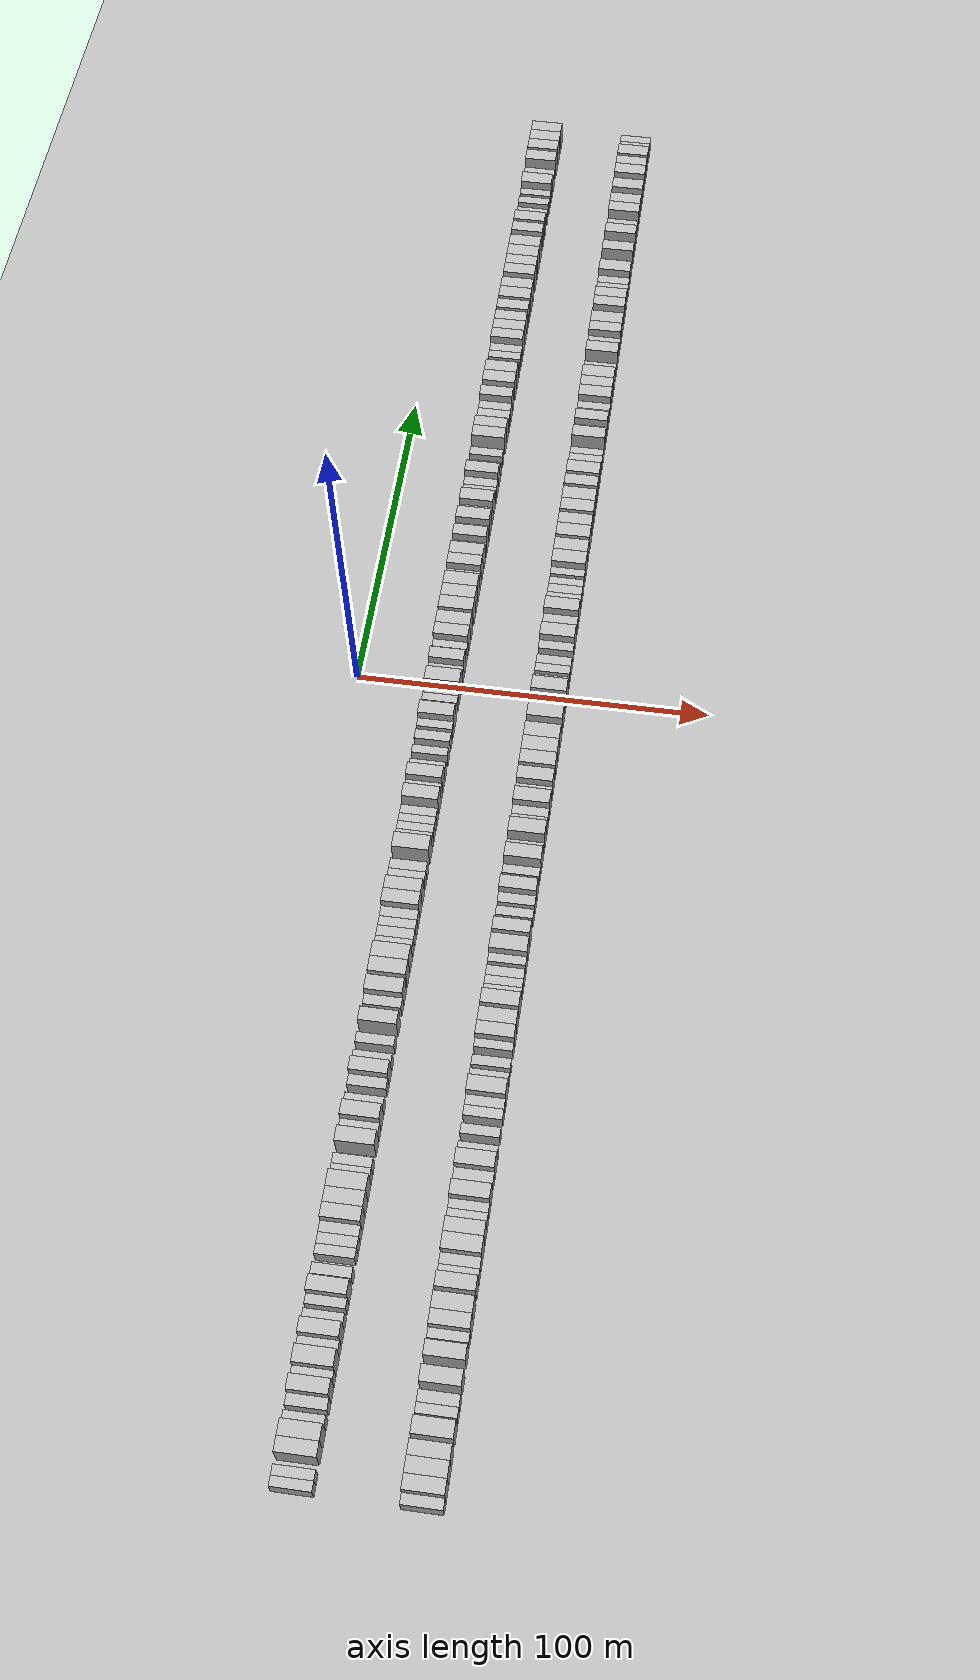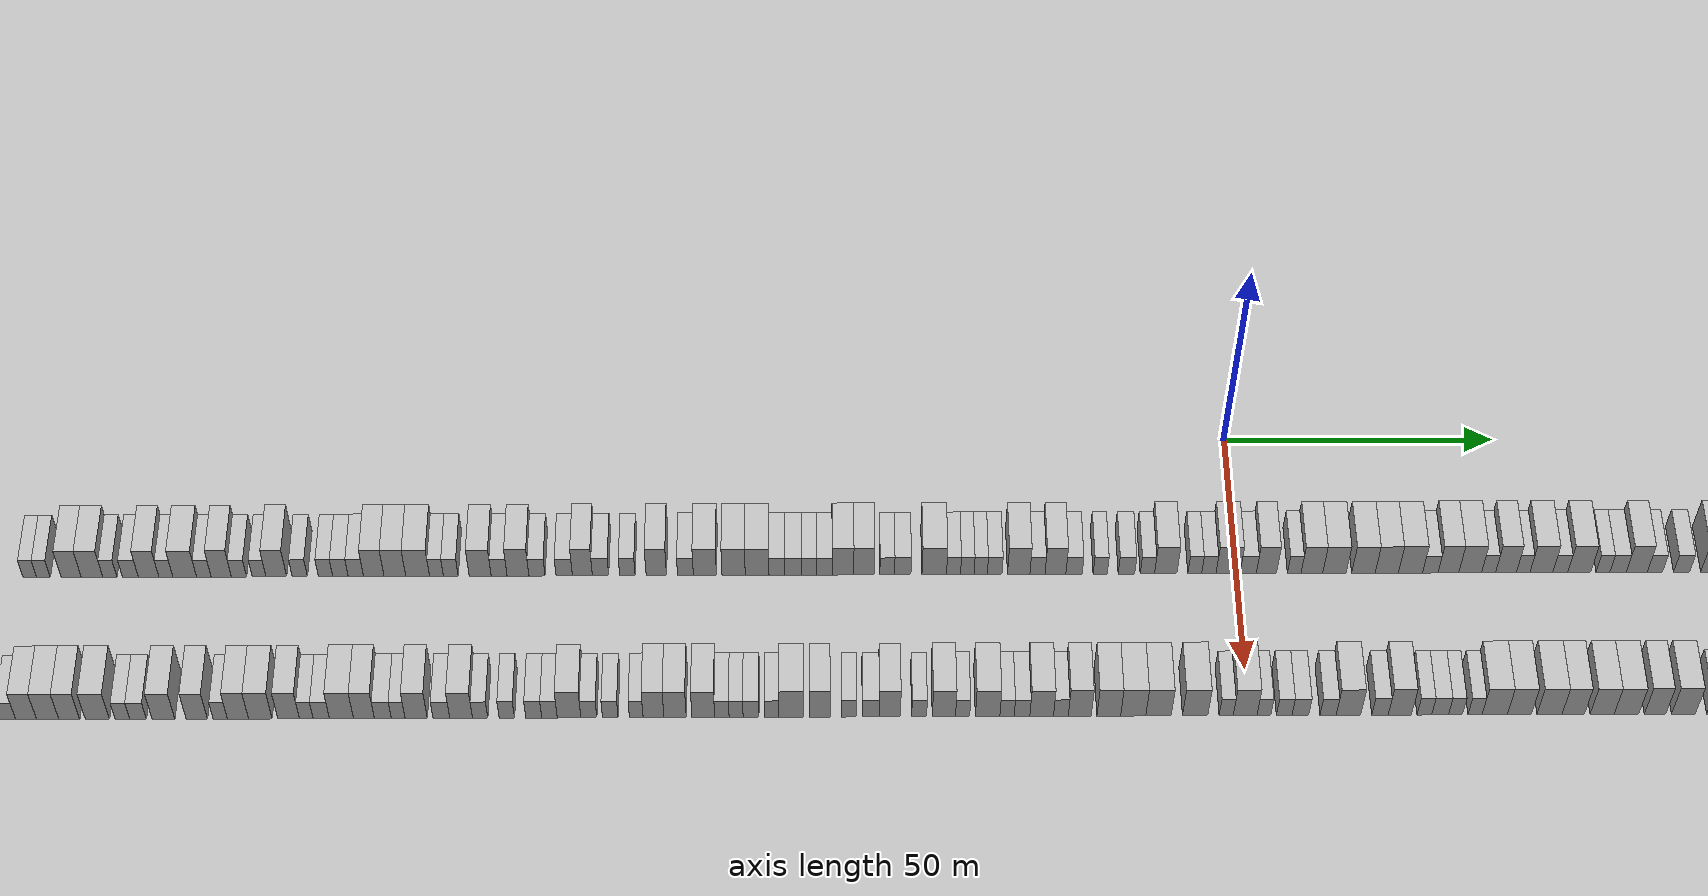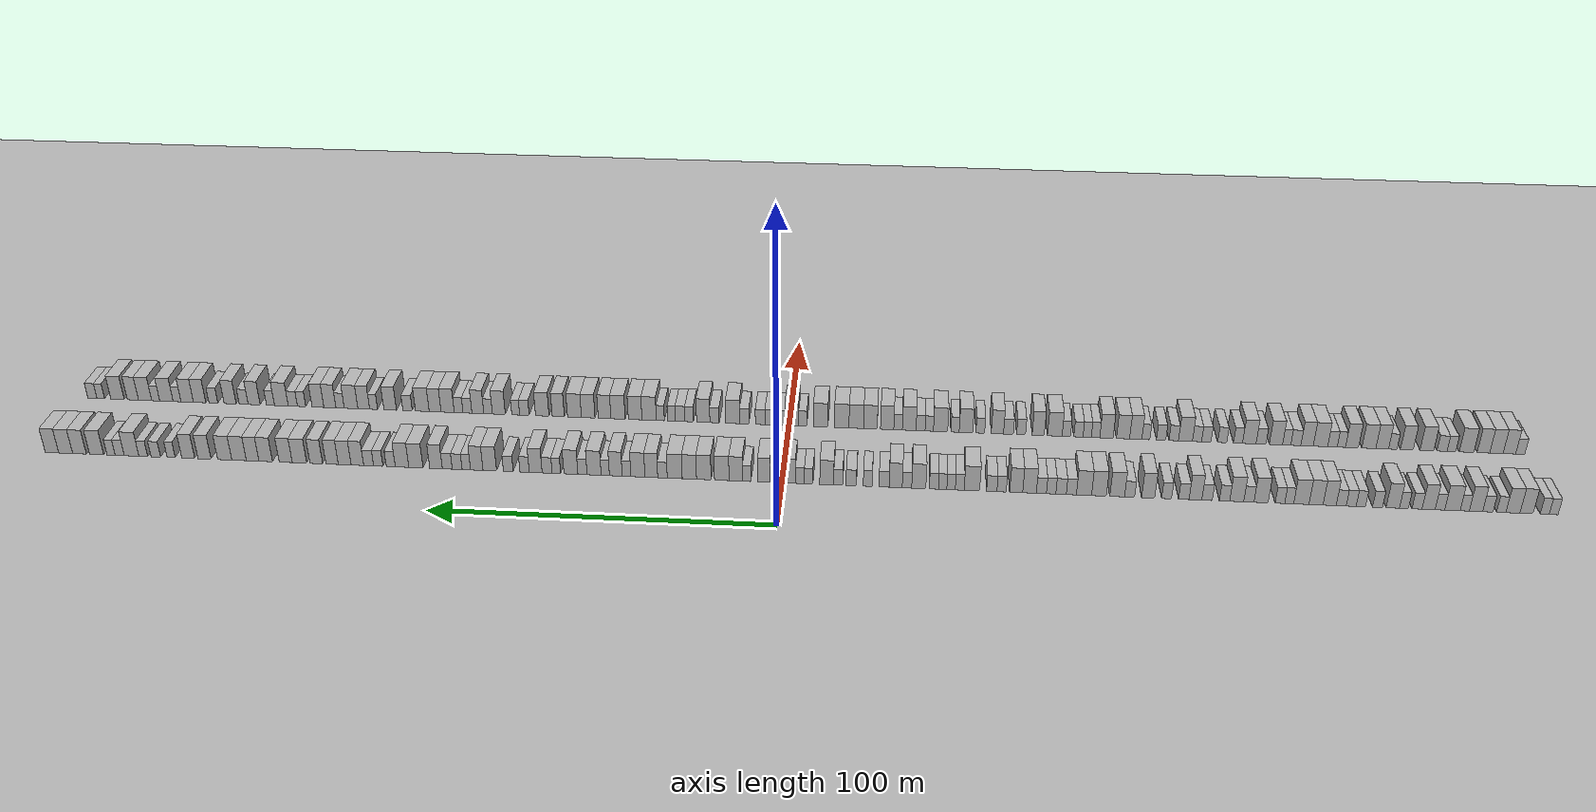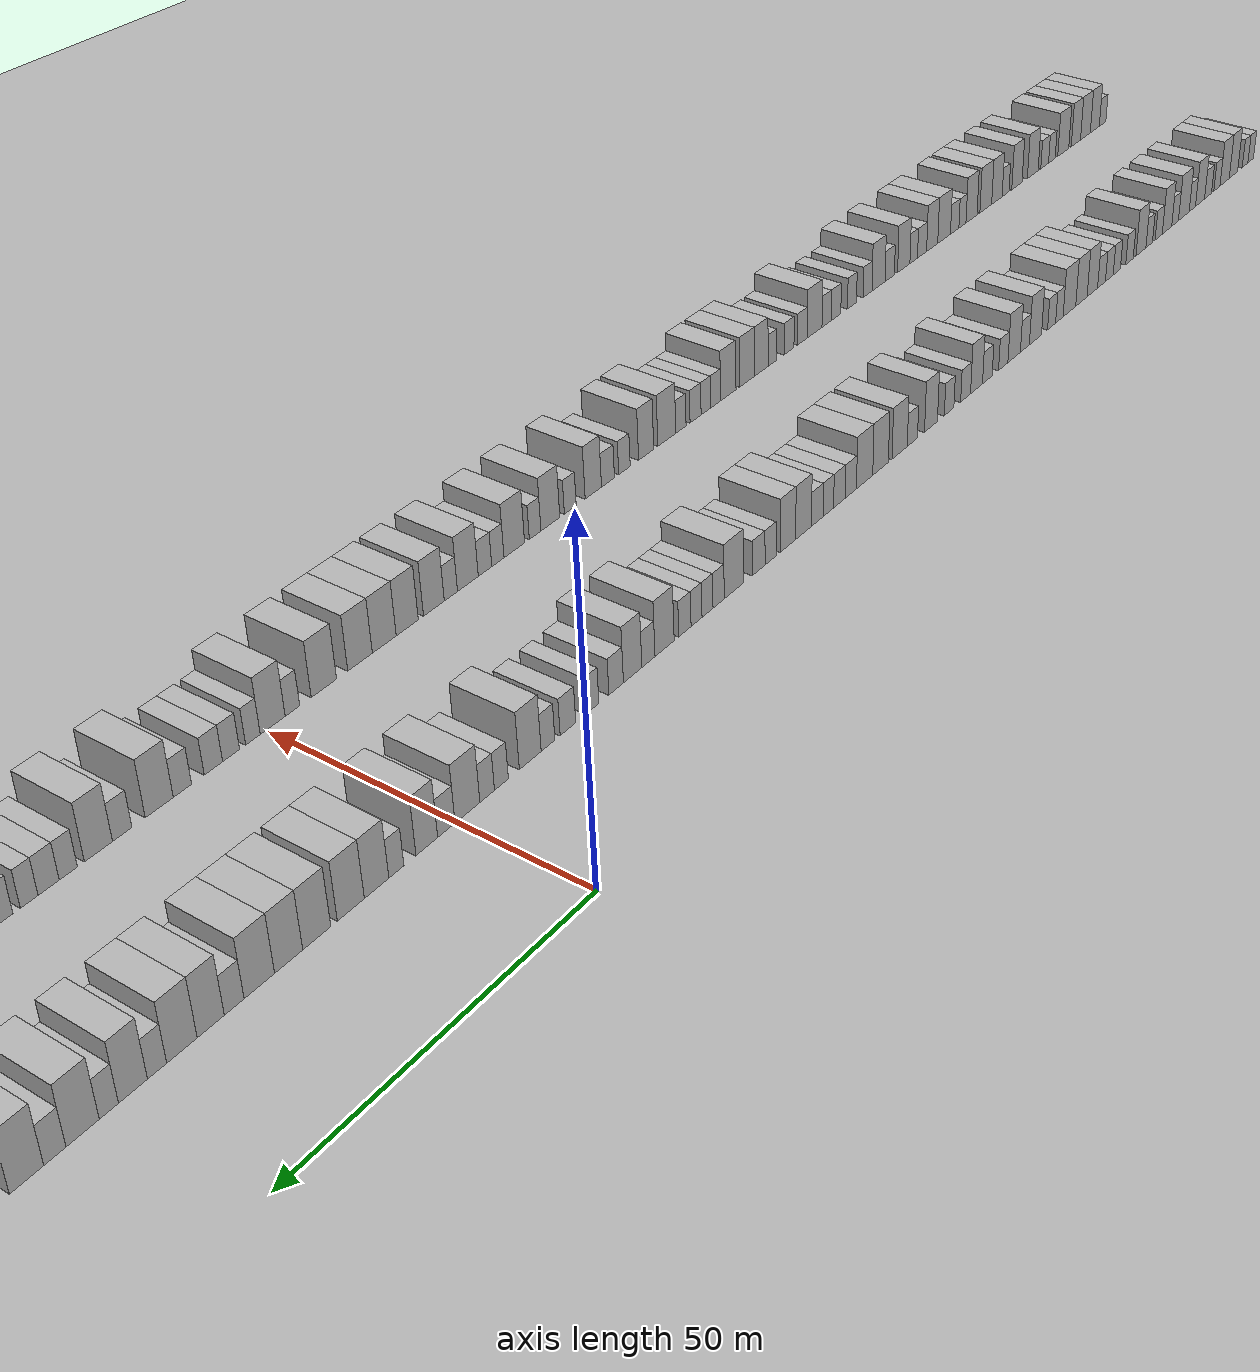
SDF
<?xml version="1.0" encoding="utf-8"?>

<sdf version="1.6">

   <world name="default">

      <gui fullscreen="0">

         <camera name="user_camera">

            <pose>-15 0 4.57585 0 0 0</pose>

            <view_controller>orbit</view_controller>

         </camera>

      </gui>

      <scene>

         <sky>

           <clouds>

             <speed>12</speed>

           </clouds>

         </sky>

         <ambient>0.4 0.4 0.4 1</ambient>

         <background>0.7 0.7 0.7 1</background>

         <shadows>1</shadows>

      </scene>

      <gravity>0 0 -9.8066</gravity>

      <magnetic_field>6e-06 2.3e-05 -4.2e-05</magnetic_field>

      <physics default="0" name="default_physics" type="ode">

         <ode>

            <solver>

               <type>quick</type>

               <iters>10</iters>

               <sor>1.0</sor>

               <use_dynamic_moi_rescaling>0</use_dynamic_moi_rescaling>

            </solver>

            <constraints>

               <cfm>0</cfm>

               <erp>0.2</erp>

               <contact_max_correcting_vel>100</contact_max_correcting_vel>

               <contact_surface_layer>0.001</contact_surface_layer>

            </constraints>

         </ode>

         <max_step_size>0.004</max_step_size>

         <real_time_factor>1</real_time_factor>

         <real_time_update_rate>250</real_time_update_rate>

      </physics>

      <light name="sun" type="directional">

         <cast_shadows>1</cast_shadows>

         <pose>0 0 10 0 0 0</pose>

         <diffuse>0.8 0.8 0.8 1</diffuse>

         <specular>0.2 0.2 0.2 1</specular>

         <attenuation>

            <range>1000</range>

            <constant>0.9</constant>

            <linear>0.01</linear>

            <quadratic>0.001</quadratic>

         </attenuation>

         <direction>-0.5 0.1 -0.9</direction>

      </light>

      <include>

         <name>ground_plane_1</name>

         <uri>model://HANNAS_ground_plane</uri>

         <pose>0 0 0  0 0 0</pose>

      </include>

      <include>

         <name>ground_plane_2</name>

         <uri>model://HANNAS_ground_plane</uri>

         <pose>100 0 0  0 0 0</pose>

      </include>

      <model name="building_1">

         <static>1</static>

         <pose frame="">25.0000 -218.7724 0 0.000000 0.000000 0.000000</pose>

         <link name="link">

            <pose frame="">0 0 3.00 0 0 0</pose>

            <collision name="collision">

               <geometry>

                  <box>

                     <size>10.0000 2.4552 6.0000</size>

                  </box>

               </geometry>

               <max_contacts>10</max_contacts>

               <surface>

                  <contact>

                     <ode/>

                  </contact>

                  <bounce/>

                  <friction>

                     <torsional>

                        <ode/>

                     </torsional>

                     <ode/>

                  </friction>

               </surface>

            </collision>

            <visual name="visual">

               <cast_shadows>0</cast_shadows>

               <geometry>

                  <box>

                     <size>10.0000 2.4552 6.0000</size>

                  </box>

               </geometry>

               <material>

                  <script>

                     <uri>model://HANNAS_wall/materials/scripts</uri>

                     <uri>model://HANNAS_wall/materials/textures</uri>

                     <name>vrc/HANNAS_wall</name>

                  </script>

               </material>

            </visual>

            <self_collide>0</self_collide>

            <enable_wind>0</enable_wind>

            <kinematic>0</kinematic>

         </link>

      </model>

      <model name="building_2">

         <static>1</static>

         <pose frame="">25.0000 -216.3096 0 0.000000 0.000000 0.000000</pose>

         <link name="link">

            <pose frame="">0 0 3.00 0 0 0</pose>

            <collision name="collision">

               <geometry>

                  <box>

                     <size>10.0000 2.4703 6.0000</size>

                  </box>

               </geometry>

               <max_contacts>10</max_contacts>

               <surface>

                  <contact>

                     <ode/>

                  </contact>

                  <bounce/>

                  <friction>

                     <torsional>

                        <ode/>

                     </torsional>

                     <ode/>

                  </friction>

               </surface>

            </collision>

            <visual name="visual">

               <cast_shadows>0</cast_shadows>

               <geometry>

                  <box>

                     <size>10.0000 2.4703 6.0000</size>

                  </box>

               </geometry>

               <material>

                  <script>

                     <uri>model://HANNAS_wall/materials/scripts</uri>

                     <uri>model://HANNAS_wall/materials/textures</uri>

                     <name>vrc/HANNAS_wall</name>

                  </script>

               </material>

            </visual>

            <self_collide>0</self_collide>

            <enable_wind>0</enable_wind>

            <kinematic>0</kinematic>

         </link>

      </model>

      <model name="building_3">

         <static>1</static>

         <pose frame="">25.0000 -211.2696 0 0.000000 0.000000 0.000000</pose>

         <link name="link">

            <pose frame="">0 0 4.50 0 0 0</pose>

            <collision name="collision">

               <geometry>

                  <box>

                     <size>10.0000 3.6098 9.0000</size>

                  </box>

               </geometry>

               <max_contacts>10</max_contacts>

               <surface>

                  <contact>

                     <ode/>

                  </contact>

                  <bounce/>

                  <friction>

                     <torsional>

                        <ode/>

                     </torsional>

                     <ode/>

                  </friction>

               </surface>

            </collision>

            <visual name="visual">

               <cast_shadows>0</cast_shadows>

               <geometry>

                  <box>

                     <size>10.0000 3.6098 9.0000</size>

                  </box>

               </geometry>

               <material>

                  <script>

                     <uri>model://HANNAS_wall/materials/scripts</uri>

                     <uri>model://HANNAS_wall/materials/textures</uri>

                     <name>vrc/HANNAS_wall</name>

                  </script>

               </material>

            </visual>

            <self_collide>0</self_collide>

            <enable_wind>0</enable_wind>

            <kinematic>0</kinematic>

         </link>

      </model>

      <model name="building_4">

         <static>1</static>

         <pose frame="">25.0000 -207.5078 0 0.000000 0.000000 0.000000</pose>

         <link name="link">

            <pose frame="">0 0 4.50 0 0 0</pose>

            <collision name="collision">

               <geometry>

                  <box>

                     <size>10.0000 3.9137 9.0000</size>

                  </box>

               </geometry>

               <max_contacts>10</max_contacts>

               <surface>

                  <contact>

                     <ode/>

                  </contact>

                  <bounce/>

                  <friction>

                     <torsional>

                        <ode/>

                     </torsional>

                     <ode/>

                  </friction>

               </surface>

            </collision>

            <visual name="visual">

               <cast_shadows>0</cast_shadows>

               <geometry>

                  <box>

                     <size>10.0000 3.9137 9.0000</size>

                  </box>

               </geometry>

               <material>

                  <script>

                     <uri>model://HANNAS_wall/materials/scripts</uri>

                     <uri>model://HANNAS_wall/materials/textures</uri>

                     <name>vrc/HANNAS_wall</name>

                  </script>

               </material>

            </visual>

            <self_collide>0</self_collide>

            <enable_wind>0</enable_wind>

            <kinematic>0</kinematic>

         </link>

      </model>

      <model name="building_5">

         <static>1</static>

         <pose frame="">25.0000 -204.2752 0 0.000000 0.000000 0.000000</pose>

         <link name="link">

            <pose frame="">0 0 3.00 0 0 0</pose>

            <collision name="collision">

               <geometry>

                  <box>

                     <size>10.0000 2.5516 6.0000</size>

                  </box>

               </geometry>

               <max_contacts>10</max_contacts>

               <surface>

                  <contact>

                     <ode/>

                  </contact>

                  <bounce/>

                  <friction>

                     <torsional>

                        <ode/>

                     </torsional>

                     <ode/>

                  </friction>

               </surface>

            </collision>

            <visual name="visual">

               <cast_shadows>0</cast_shadows>

               <geometry>

                  <box>

                     <size>10.0000 2.5516 6.0000</size>

                  </box>

               </geometry>

               <material>

                  <script>

                     <uri>model://HANNAS_wall/materials/scripts</uri>

                     <uri>model://HANNAS_wall/materials/textures</uri>

                     <name>vrc/HANNAS_wall</name>

                  </script>

               </material>

            </visual>

            <self_collide>0</self_collide>

            <enable_wind>0</enable_wind>

            <kinematic>0</kinematic>

         </link>

      </model>

      <model name="building_6">

         <static>1</static>

         <pose frame="">25.0000 -200.5648 0 0.000000 0.000000 0.000000</pose>

         <link name="link">

            <pose frame="">0 0 3.00 0 0 0</pose>

            <collision name="collision">

               <geometry>

                  <box>

                     <size>10.0000 2.8691 6.0000</size>

                  </box>

               </geometry>

               <max_contacts>10</max_contacts>

               <surface>

                  <contact>

                     <ode/>

                  </contact>

                  <bounce/>

                  <friction>

                     <torsional>

                        <ode/>

                     </torsional>

                     <ode/>

                  </friction>

               </surface>

            </collision>

            <visual name="visual">

               <cast_shadows>0</cast_shadows>

               <geometry>

                  <box>

                     <size>10.0000 2.8691 6.0000</size>

                  </box>

               </geometry>

               <material>

                  <script>

                     <uri>model://HANNAS_wall/materials/scripts</uri>

                     <uri>model://HANNAS_wall/materials/textures</uri>

                     <name>vrc/HANNAS_wall</name>

                  </script>

               </material>

            </visual>

            <self_collide>0</self_collide>

            <enable_wind>0</enable_wind>

            <kinematic>0</kinematic>

         </link>

      </model>

      <model name="building_7">

         <static>1</static>

         <pose frame="">25.0000 -197.2733 0 0.000000 0.000000 0.000000</pose>

         <link name="link">

            <pose frame="">0 0 4.50 0 0 0</pose>

            <collision name="collision">

               <geometry>

                  <box>

                     <size>10.0000 3.7139 9.0000</size>

                  </box>

               </geometry>

               <max_contacts>10</max_contacts>

               <surface>

                  <contact>

                     <ode/>

                  </contact>

                  <bounce/>

                  <friction>

                     <torsional>

                        <ode/>

                     </torsional>

                     <ode/>

                  </friction>

               </surface>

            </collision>

            <visual name="visual">

               <cast_shadows>0</cast_shadows>

               <geometry>

                  <box>

                     <size>10.0000 3.7139 9.0000</size>

                  </box>

               </geometry>

               <material>

                  <script>

                     <uri>model://HANNAS_wall/materials/scripts</uri>

                     <uri>model://HANNAS_wall/materials/textures</uri>

                     <name>vrc/HANNAS_wall</name>

                  </script>

               </material>

            </visual>

            <self_collide>0</self_collide>

            <enable_wind>0</enable_wind>

            <kinematic>0</kinematic>

         </link>

      </model>

      <model name="building_8">

         <static>1</static>

         <pose frame="">25.0000 -194.1472 0 0.000000 0.000000 0.000000</pose>

         <link name="link">

            <pose frame="">0 0 3.00 0 0 0</pose>

            <collision name="collision">

               <geometry>

                  <box>

                     <size>10.0000 2.5385 6.0000</size>

                  </box>

               </geometry>

               <max_contacts>10</max_contacts>

               <surface>

                  <contact>

                     <ode/>

                  </contact>

                  <bounce/>

                  <friction>

                     <torsional>

                        <ode/>

                     </torsional>

                     <ode/>

                  </friction>

               </surface>

            </collision>

            <visual name="visual">

               <cast_shadows>0</cast_shadows>

               <geometry>

                  <box>

                     <size>10.0000 2.5385 6.0000</size>

                  </box>

               </geometry>

               <material>

                  <script>

                     <uri>model://HANNAS_wall/materials/scripts</uri>

                     <uri>model://HANNAS_wall/materials/textures</uri>

                     <name>vrc/HANNAS_wall</name>

                  </script>

               </material>

            </visual>

            <self_collide>0</self_collide>

            <enable_wind>0</enable_wind>

            <kinematic>0</kinematic>

         </link>

      </model>

      <model name="building_9">

         <static>1</static>

         <pose frame="">25.0000 -190.7358 0 0.000000 0.000000 0.000000</pose>

         <link name="link">

            <pose frame="">0 0 4.50 0 0 0</pose>

            <collision name="collision">

               <geometry>

                  <box>

                     <size>10.0000 4.2843 9.0000</size>

                  </box>

               </geometry>

               <max_contacts>10</max_contacts>

               <surface>

                  <contact>

                     <ode/>

                  </contact>

                  <bounce/>

                  <friction>

                     <torsional>

                        <ode/>

                     </torsional>

                     <ode/>

                  </friction>

               </surface>

            </collision>

            <visual name="visual">

               <cast_shadows>0</cast_shadows>

               <geometry>

                  <box>

                     <size>10.0000 4.2843 9.0000</size>

                  </box>

               </geometry>

               <material>

                  <script>

                     <uri>model://HANNAS_wall/materials/scripts</uri>

                     <uri>model://HANNAS_wall/materials/textures</uri>

                     <name>vrc/HANNAS_wall</name>

                  </script>

               </material>

            </visual>

            <self_collide>0</self_collide>

            <enable_wind>0</enable_wind>

            <kinematic>0</kinematic>

         </link>

      </model>

      <model name="building_10">

         <static>1</static>

         <pose frame="">25.0000 -187.2706 0 0.000000 0.000000 0.000000</pose>

         <link name="link">

            <pose frame="">0 0 3.00 0 0 0</pose>

            <collision name="collision">

               <geometry>

                  <box>

                     <size>10.0000 2.6461 6.0000</size>

                  </box>

               </geometry>

               <max_contacts>10</max_contacts>

               <surface>

                  <contact>

                     <ode/>

                  </contact>

                  <bounce/>

                  <friction>

                     <torsional>

                        <ode/>

                     </torsional>

                     <ode/>

                  </friction>

               </surface>

            </collision>

            <visual name="visual">

               <cast_shadows>0</cast_shadows>

               <geometry>

                  <box>

                     <size>10.0000 2.6461 6.0000</size>

                  </box>

               </geometry>

               <material>

                  <script>

                     <uri>model://HANNAS_wall/materials/scripts</uri>

                     <uri>model://HANNAS_wall/materials/textures</uri>

                     <name>vrc/HANNAS_wall</name>

                  </script>

               </material>

            </visual>

            <self_collide>0</self_collide>

            <enable_wind>0</enable_wind>

            <kinematic>0</kinematic>

         </link>

      </model>

      <model name="building_11">

         <static>1</static>

         <pose frame="">25.0000 -184.1075 0 0.000000 0.000000 0.000000</pose>

         <link name="link">

            <pose frame="">0 0 4.50 0 0 0</pose>

            <collision name="collision">

               <geometry>

                  <box>

                     <size>10.0000 3.6802 9.0000</size>

                  </box>

               </geometry>

               <max_contacts>10</max_contacts>

               <surface>

                  <contact>

                     <ode/>

                  </contact>

                  <bounce/>

                  <friction>

                     <torsional>

                        <ode/>

                     </torsional>

                     <ode/>

                  </friction>

               </surface>

            </collision>

            <visual name="visual">

               <cast_shadows>0</cast_shadows>

               <geometry>

                  <box>

                     <size>10.0000 3.6802 9.0000</size>

                  </box>

               </geometry>

               <material>

                  <script>

                     <uri>model://HANNAS_wall/materials/scripts</uri>

                     <uri>model://HANNAS_wall/materials/textures</uri>

                     <name>vrc/HANNAS_wall</name>

                  </script>

               </material>

            </visual>

            <self_collide>0</self_collide>

            <enable_wind>0</enable_wind>

            <kinematic>0</kinematic>

         </link>

      </model>

      <model name="building_12">

         <static>1</static>

         <pose frame="">25.0000 -180.8865 0 0.000000 0.000000 0.000000</pose>

         <link name="link">

            <pose frame="">0 0 3.00 0 0 0</pose>

            <collision name="collision">

               <geometry>

                  <box>

                     <size>10.0000 2.7617 6.0000</size>

                  </box>

               </geometry>

               <max_contacts>10</max_contacts>

               <surface>

                  <contact>

                     <ode/>

                  </contact>

                  <bounce/>

                  <friction>

                     <torsional>

                        <ode/>

                     </torsional>

                     <ode/>

                  </friction>

               </surface>

            </collision>

            <visual name="visual">

               <cast_shadows>0</cast_shadows>

               <geometry>

                  <box>

                     <size>10.0000 2.7617 6.0000</size>

                  </box>

               </geometry>

               <material>

                  <script>

                     <uri>model://HANNAS_wall/materials/scripts</uri>

                     <uri>model://HANNAS_wall/materials/textures</uri>

                     <name>vrc/HANNAS_wall</name>

                  </script>

               </material>

            </visual>

            <self_collide>0</self_collide>

            <enable_wind>0</enable_wind>

            <kinematic>0</kinematic>

         </link>

      </model>

      <model name="building_13">

         <static>1</static>

         <pose frame="">25.0000 -177.2530 0 0.000000 0.000000 0.000000</pose>

         <link name="link">

            <pose frame="">0 0 3.00 0 0 0</pose>

            <collision name="collision">

               <geometry>

                  <box>

                     <size>10.0000 2.5054 6.0000</size>

                  </box>

               </geometry>

               <max_contacts>10</max_contacts>

               <surface>

                  <contact>

                     <ode/>

                  </contact>

                  <bounce/>

                  <friction>

                     <torsional>

                        <ode/>

                     </torsional>

                     <ode/>

                  </friction>

               </surface>

            </collision>

            <visual name="visual">

               <cast_shadows>0</cast_shadows>

               <geometry>

                  <box>

                     <size>10.0000 2.5054 6.0000</size>

                  </box>

               </geometry>

               <material>

                  <script>

                     <uri>model://HANNAS_wall/materials/scripts</uri>

                     <uri>model://HANNAS_wall/materials/textures</uri>

                     <name>vrc/HANNAS_wall</name>

                  </script>

               </material>

            </visual>

            <self_collide>0</self_collide>

            <enable_wind>0</enable_wind>

            <kinematic>0</kinematic>

         </link>

      </model>

      <model name="building_14">

         <static>1</static>

         <pose frame="">25.0000 -174.1250 0 0.000000 0.000000 0.000000</pose>

         <link name="link">

            <pose frame="">0 0 4.50 0 0 0</pose>

            <collision name="collision">

               <geometry>

                  <box>

                     <size>10.0000 3.7505 9.0000</size>

                  </box>

               </geometry>

               <max_contacts>10</max_contacts>

               <surface>

                  <contact>

                     <ode/>

                  </contact>

                  <bounce/>

                  <friction>

                     <torsional>

                        <ode/>

                     </torsional>

                     <ode/>

                  </friction>

               </surface>

            </collision>

            <visual name="visual">

               <cast_shadows>0</cast_shadows>

               <geometry>

                  <box>

                     <size>10.0000 3.7505 9.0000</size>

                  </box>

               </geometry>

               <material>

                  <script>

                     <uri>model://HANNAS_wall/materials/scripts</uri>

                     <uri>model://HANNAS_wall/materials/textures</uri>

                     <name>vrc/HANNAS_wall</name>

                  </script>

               </material>

            </visual>

            <self_collide>0</self_collide>

            <enable_wind>0</enable_wind>

            <kinematic>0</kinematic>

         </link>

      </model>

      <model name="building_15">

         <static>1</static>

         <pose frame="">25.0000 -169.8699 0 0.000000 0.000000 0.000000</pose>

         <link name="link">

            <pose frame="">0 0 3.00 0 0 0</pose>

            <collision name="collision">

               <geometry>

                  <box>

                     <size>10.0000 2.7595 6.0000</size>

                  </box>

               </geometry>

               <max_contacts>10</max_contacts>

               <surface>

                  <contact>

                     <ode/>

                  </contact>

                  <bounce/>

                  <friction>

                     <torsional>

                        <ode/>

                     </torsional>

                     <ode/>

                  </friction>

               </surface>

            </collision>

            <visual name="visual">

               <cast_shadows>0</cast_shadows>

               <geometry>

                  <box>

                     <size>10.0000 2.7595 6.0000</size>

                  </box>

               </geometry>

               <material>

                  <script>

                     <uri>model://HANNAS_wall/materials/scripts</uri>

                     <uri>model://HANNAS_wall/materials/textures</uri>

                     <name>vrc/HANNAS_wall</name>

                  </script>

               </material>

            </visual>

            <self_collide>0</self_collide>

            <enable_wind>0</enable_wind>

            <kinematic>0</kinematic>

         </link>

      </model>

      <model name="building_16">

         <static>1</static>

         <pose frame="">25.0000 -165.1983 0 0.000000 0.000000 0.000000</pose>

         <link name="link">

            <pose frame="">0 0 3.00 0 0 0</pose>

            <collision name="collision">

               <geometry>

                  <box>

                     <size>10.0000 2.5838 6.0000</size>

                  </box>

               </geometry>

               <max_contacts>10</max_contacts>

               <surface>

                  <contact>

                     <ode/>

                  </contact>

                  <bounce/>

                  <friction>

                     <torsional>

                        <ode/>

                     </torsional>

                     <ode/>

                  </friction>

               </surface>

            </collision>

            <visual name="visual">

               <cast_shadows>0</cast_shadows>

               <geometry>

                  <box>

                     <size>10.0000 2.5838 6.0000</size>

                  </box>

               </geometry>

               <material>

                  <script>

                     <uri>model://HANNAS_wall/materials/scripts</uri>

                     <uri>model://HANNAS_wall/materials/textures</uri>

                     <name>vrc/HANNAS_wall</name>

                  </script>

               </material>

            </visual>

            <self_collide>0</self_collide>

            <enable_wind>0</enable_wind>

            <kinematic>0</kinematic>

         </link>

      </model>

      <model name="building_17">

         <static>1</static>

         <pose frame="">25.0000 -162.5082 0 0.000000 0.000000 0.000000</pose>

         <link name="link">

            <pose frame="">0 0 3.00 0 0 0</pose>

            <collision name="collision">

               <geometry>

                  <box>

                     <size>10.0000 2.7964 6.0000</size>

                  </box>

               </geometry>

               <max_contacts>10</max_contacts>

               <surface>

                  <contact>

                     <ode/>

                  </contact>

                  <bounce/>

                  <friction>

                     <torsional>

                        <ode/>

                     </torsional>

                     <ode/>

                  </friction>

               </surface>

            </collision>

            <visual name="visual">

               <cast_shadows>0</cast_shadows>

               <geometry>

                  <box>

                     <size>10.0000 2.7964 6.0000</size>

                  </box>

               </geometry>

               <material>

                  <script>

                     <uri>model://HANNAS_wall/materials/scripts</uri>

                     <uri>model://HANNAS_wall/materials/textures</uri>

                     <name>vrc/HANNAS_wall</name>

                  </script>

               </material>

            </visual>

            <self_collide>0</self_collide>

            <enable_wind>0</enable_wind>

            <kinematic>0</kinematic>

         </link>

      </model>

      <model name="building_18">

         <static>1</static>

         <pose frame="">25.0000 -159.7110 0 0.000000 0.000000 0.000000</pose>

         <link name="link">

            <pose frame="">0 0 3.00 0 0 0</pose>

            <collision name="collision">

               <geometry>

                  <box>

                     <size>10.0000 2.7979 6.0000</size>

                  </box>

               </geometry>

               <max_contacts>10</max_contacts>

               <surface>

                  <contact>

                     <ode/>

                  </contact>

                  <bounce/>

                  <friction>

                     <torsional>

                        <ode/>

                     </torsional>

                     <ode/>

                  </friction>

               </surface>

            </collision>

            <visual name="visual">

               <cast_shadows>0</cast_shadows>

               <geometry>

                  <box>

                     <size>10.0000 2.7979 6.0000</size>

                  </box>

               </geometry>

               <material>

                  <script>

                     <uri>model://HANNAS_wall/materials/scripts</uri>

                     <uri>model://HANNAS_wall/materials/textures</uri>

                     <name>vrc/HANNAS_wall</name>

                  </script>

               </material>

            </visual>

            <self_collide>0</self_collide>

            <enable_wind>0</enable_wind>

            <kinematic>0</kinematic>

         </link>

      </model>

      <model name="building_19">

         <static>1</static>

         <pose frame="">25.0000 -156.4629 0 0.000000 0.000000 0.000000</pose>

         <link name="link">

            <pose frame="">0 0 4.50 0 0 0</pose>

            <collision name="collision">

               <geometry>

                  <box>

                     <size>10.0000 3.6983 9.0000</size>

                  </box>

               </geometry>

               <max_contacts>10</max_contacts>

               <surface>

                  <contact>

                     <ode/>

                  </contact>

                  <bounce/>

                  <friction>

                     <torsional>

                        <ode/>

                     </torsional>

                     <ode/>

                  </friction>

               </surface>

            </collision>

            <visual name="visual">

               <cast_shadows>0</cast_shadows>

               <geometry>

                  <box>

                     <size>10.0000 3.6983 9.0000</size>

                  </box>

               </geometry>

               <material>

                  <script>

                     <uri>model://HANNAS_wall/materials/scripts</uri>

                     <uri>model://HANNAS_wall/materials/textures</uri>

                     <name>vrc/HANNAS_wall</name>

                  </script>

               </material>

            </visual>

            <self_collide>0</self_collide>

            <enable_wind>0</enable_wind>

            <kinematic>0</kinematic>

         </link>

      </model>

      <model name="building_20">

         <static>1</static>

         <pose frame="">25.0000 -152.6454 0 0.000000 0.000000 0.000000</pose>

         <link name="link">

            <pose frame="">0 0 4.50 0 0 0</pose>

            <collision name="collision">

               <geometry>

                  <box>

                     <size>10.0000 3.9368 9.0000</size>

                  </box>

               </geometry>

               <max_contacts>10</max_contacts>

               <surface>

                  <contact>

                     <ode/>

                  </contact>

                  <bounce/>

                  <friction>

                     <torsional>

                        <ode/>

                     </torsional>

                     <ode/>

                  </friction>

               </surface>

            </collision>

            <visual name="visual">

               <cast_shadows>0</cast_shadows>

               <geometry>

                  <box>

                     <size>10.0000 3.9368 9.0000</size>

                  </box>

               </geometry>

               <material>

                  <script>

                     <uri>model://HANNAS_wall/materials/scripts</uri>

                     <uri>model://HANNAS_wall/materials/textures</uri>

                     <name>vrc/HANNAS_wall</name>

                  </script>

               </material>

            </visual>

            <self_collide>0</self_collide>

            <enable_wind>0</enable_wind>

            <kinematic>0</kinematic>

         </link>

      </model>

      <model name="building_21">

         <static>1</static>

         <pose frame="">25.0000 -148.5193 0 0.000000 0.000000 0.000000</pose>

         <link name="link">

            <pose frame="">0 0 4.50 0 0 0</pose>

            <collision name="collision">

               <geometry>

                  <box>

                     <size>10.0000 4.3155 9.0000</size>

                  </box>

               </geometry>

               <max_contacts>10</max_contacts>

               <surface>

                  <contact>

                     <ode/>

                  </contact>

                  <bounce/>

                  <friction>

                     <torsional>

                        <ode/>

                     </torsional>

                     <ode/>

                  </friction>

               </surface>

            </collision>

            <visual name="visual">

               <cast_shadows>0</cast_shadows>

               <geometry>

                  <box>

                     <size>10.0000 4.3155 9.0000</size>

                  </box>

               </geometry>

               <material>

                  <script>

                     <uri>model://HANNAS_wall/materials/scripts</uri>

                     <uri>model://HANNAS_wall/materials/textures</uri>

                     <name>vrc/HANNAS_wall</name>

                  </script>

               </material>

            </visual>

            <self_collide>0</self_collide>

            <enable_wind>0</enable_wind>

            <kinematic>0</kinematic>

         </link>

      </model>

      <model name="building_22">

         <static>1</static>

         <pose frame="">25.0000 -145.1118 0 0.000000 0.000000 0.000000</pose>

         <link name="link">

            <pose frame="">0 0 3.00 0 0 0</pose>

            <collision name="collision">

               <geometry>

                  <box>

                     <size>10.0000 2.4994 6.0000</size>

                  </box>

               </geometry>

               <max_contacts>10</max_contacts>

               <surface>

                  <contact>

                     <ode/>

                  </contact>

                  <bounce/>

                  <friction>

                     <torsional>

                        <ode/>

                     </torsional>

                     <ode/>

                  </friction>

               </surface>

            </collision>

            <visual name="visual">

               <cast_shadows>0</cast_shadows>

               <geometry>

                  <box>

                     <size>10.0000 2.4994 6.0000</size>

                  </box>

               </geometry>

               <material>

                  <script>

                     <uri>model://HANNAS_wall/materials/scripts</uri>

                     <uri>model://HANNAS_wall/materials/textures</uri>

                     <name>vrc/HANNAS_wall</name>

                  </script>

               </material>

            </visual>

            <self_collide>0</self_collide>

            <enable_wind>0</enable_wind>

            <kinematic>0</kinematic>

         </link>

      </model>

      <model name="building_23">

         <static>1</static>

         <pose frame="">25.0000 -142.5120 0 0.000000 0.000000 0.000000</pose>

         <link name="link">

            <pose frame="">0 0 3.00 0 0 0</pose>

            <collision name="collision">

               <geometry>

                  <box>

                     <size>10.0000 2.7002 6.0000</size>

                  </box>

               </geometry>

               <max_contacts>10</max_contacts>

               <surface>

                  <contact>

                     <ode/>

                  </contact>

                  <bounce/>

                  <friction>

                     <torsional>

                        <ode/>

                     </torsional>

                     <ode/>

                  </friction>

               </surface>

            </collision>

            <visual name="visual">

               <cast_shadows>0</cast_shadows>

               <geometry>

                  <box>

                     <size>10.0000 2.7002 6.0000</size>

                  </box>

               </geometry>

               <material>

                  <script>

                     <uri>model://HANNAS_wall/materials/scripts</uri>

                     <uri>model://HANNAS_wall/materials/textures</uri>

                     <name>vrc/HANNAS_wall</name>

                  </script>

               </material>

            </visual>

            <self_collide>0</self_collide>

            <enable_wind>0</enable_wind>

            <kinematic>0</kinematic>

         </link>

      </model>

      <model name="building_24">

         <static>1</static>

         <pose frame="">25.0000 -137.1737 0 0.000000 0.000000 0.000000</pose>

         <link name="link">

            <pose frame="">0 0 4.50 0 0 0</pose>

            <collision name="collision">

               <geometry>

                  <box>

                     <size>10.0000 3.9764 9.0000</size>

                  </box>

               </geometry>

               <max_contacts>10</max_contacts>

               <surface>

                  <contact>

                     <ode/>

                  </contact>

                  <bounce/>

                  <friction>

                     <torsional>

                        <ode/>

                     </torsional>

                     <ode/>

                  </friction>

               </surface>

            </collision>

            <visual name="visual">

               <cast_shadows>0</cast_shadows>

               <geometry>

                  <box>

                     <size>10.0000 3.9764 9.0000</size>

                  </box>

               </geometry>

               <material>

                  <script>

                     <uri>model://HANNAS_wall/materials/scripts</uri>

                     <uri>model://HANNAS_wall/materials/textures</uri>

                     <name>vrc/HANNAS_wall</name>

                  </script>

               </material>

            </visual>

            <self_collide>0</self_collide>

            <enable_wind>0</enable_wind>

            <kinematic>0</kinematic>

         </link>

      </model>

      <model name="building_25">

         <static>1</static>

         <pose frame="">25.0000 -133.7473 0 0.000000 0.000000 0.000000</pose>

         <link name="link">

            <pose frame="">0 0 3.00 0 0 0</pose>

            <collision name="collision">

               <geometry>

                  <box>

                     <size>10.0000 2.8764 6.0000</size>

                  </box>

               </geometry>

               <max_contacts>10</max_contacts>

               <surface>

                  <contact>

                     <ode/>

                  </contact>

                  <bounce/>

                  <friction>

                     <torsional>

                        <ode/>

                     </torsional>

                     <ode/>

                  </friction>

               </surface>

            </collision>

            <visual name="visual">

               <cast_shadows>0</cast_shadows>

               <geometry>

                  <box>

                     <size>10.0000 2.8764 6.0000</size>

                  </box>

               </geometry>

               <material>

                  <script>

                     <uri>model://HANNAS_wall/materials/scripts</uri>

                     <uri>model://HANNAS_wall/materials/textures</uri>

                     <name>vrc/HANNAS_wall</name>

                  </script>

               </material>

            </visual>

            <self_collide>0</self_collide>

            <enable_wind>0</enable_wind>

            <kinematic>0</kinematic>

         </link>

      </model>

      <model name="building_26">

         <static>1</static>

         <pose frame="">25.0000 -130.3267 0 0.000000 0.000000 0.000000</pose>

         <link name="link">

            <pose frame="">0 0 4.50 0 0 0</pose>

            <collision name="collision">

               <geometry>

                  <box>

                     <size>10.0000 3.9649 9.0000</size>

                  </box>

               </geometry>

               <max_contacts>10</max_contacts>

               <surface>

                  <contact>

                     <ode/>

                  </contact>

                  <bounce/>

                  <friction>

                     <torsional>

                        <ode/>

                     </torsional>

                     <ode/>

                  </friction>

               </surface>

            </collision>

            <visual name="visual">

               <cast_shadows>0</cast_shadows>

               <geometry>

                  <box>

                     <size>10.0000 3.9649 9.0000</size>

                  </box>

               </geometry>

               <material>

                  <script>

                     <uri>model://HANNAS_wall/materials/scripts</uri>

                     <uri>model://HANNAS_wall/materials/textures</uri>

                     <name>vrc/HANNAS_wall</name>

                  </script>

               </material>

            </visual>

            <self_collide>0</self_collide>

            <enable_wind>0</enable_wind>

            <kinematic>0</kinematic>

         </link>

      </model>

      <model name="building_27">

         <static>1</static>

         <pose frame="">25.0000 -126.8843 0 0.000000 0.000000 0.000000</pose>

         <link name="link">

            <pose frame="">0 0 3.00 0 0 0</pose>

            <collision name="collision">

               <geometry>

                  <box>

                     <size>10.0000 2.9198 6.0000</size>

                  </box>

               </geometry>

               <max_contacts>10</max_contacts>

               <surface>

                  <contact>

                     <ode/>

                  </contact>

                  <bounce/>

                  <friction>

                     <torsional>

                        <ode/>

                     </torsional>

                     <ode/>

                  </friction>

               </surface>

            </collision>

            <visual name="visual">

               <cast_shadows>0</cast_shadows>

               <geometry>

                  <box>

                     <size>10.0000 2.9198 6.0000</size>

                  </box>

               </geometry>

               <material>

                  <script>

                     <uri>model://HANNAS_wall/materials/scripts</uri>

                     <uri>model://HANNAS_wall/materials/textures</uri>

                     <name>vrc/HANNAS_wall</name>

                  </script>

               </material>

            </visual>

            <self_collide>0</self_collide>

            <enable_wind>0</enable_wind>

            <kinematic>0</kinematic>

         </link>

      </model>

      <model name="building_28">

         <static>1</static>

         <pose frame="">25.0000 -121.9462 0 0.000000 0.000000 0.000000</pose>

         <link name="link">

            <pose frame="">0 0 3.00 0 0 0</pose>

            <collision name="collision">

               <geometry>

                  <box>

                     <size>10.0000 2.9565 6.0000</size>

                  </box>

               </geometry>

               <max_contacts>10</max_contacts>

               <surface>

                  <contact>

                     <ode/>

                  </contact>

                  <bounce/>

                  <friction>

                     <torsional>

                        <ode/>

                     </torsional>

                     <ode/>

                  </friction>

               </surface>

            </collision>

            <visual name="visual">

               <cast_shadows>0</cast_shadows>

               <geometry>

                  <box>

                     <size>10.0000 2.9565 6.0000</size>

                  </box>

               </geometry>

               <material>

                  <script>

                     <uri>model://HANNAS_wall/materials/scripts</uri>

                     <uri>model://HANNAS_wall/materials/textures</uri>

                     <name>vrc/HANNAS_wall</name>

                  </script>

               </material>

            </visual>

            <self_collide>0</self_collide>

            <enable_wind>0</enable_wind>

            <kinematic>0</kinematic>

         </link>

      </model>

      <model name="building_29">

         <static>1</static>

         <pose frame="">25.0000 -118.6565 0 0.000000 0.000000 0.000000</pose>

         <link name="link">

            <pose frame="">0 0 4.50 0 0 0</pose>

            <collision name="collision">

               <geometry>

                  <box>

                     <size>10.0000 3.6229 9.0000</size>

                  </box>

               </geometry>

               <max_contacts>10</max_contacts>

               <surface>

                  <contact>

                     <ode/>

                  </contact>

                  <bounce/>

                  <friction>

                     <torsional>

                        <ode/>

                     </torsional>

                     <ode/>

                  </friction>

               </surface>

            </collision>

            <visual name="visual">

               <cast_shadows>0</cast_shadows>

               <geometry>

                  <box>

                     <size>10.0000 3.6229 9.0000</size>

                  </box>

               </geometry>

               <material>

                  <script>

                     <uri>model://HANNAS_wall/materials/scripts</uri>

                     <uri>model://HANNAS_wall/materials/textures</uri>

                     <name>vrc/HANNAS_wall</name>

                  </script>

               </material>

            </visual>

            <self_collide>0</self_collide>

            <enable_wind>0</enable_wind>

            <kinematic>0</kinematic>

         </link>

      </model>

      <model name="building_30">

         <static>1</static>

         <pose frame="">25.0000 -115.3672 0 0.000000 0.000000 0.000000</pose>

         <link name="link">

            <pose frame="">0 0 3.00 0 0 0</pose>

            <collision name="collision">

               <geometry>

                  <box>

                     <size>10.0000 2.9556 6.0000</size>

                  </box>

               </geometry>

               <max_contacts>10</max_contacts>

               <surface>

                  <contact>

                     <ode/>

                  </contact>

                  <bounce/>

                  <friction>

                     <torsional>

                        <ode/>

                     </torsional>

                     <ode/>

                  </friction>

               </surface>

            </collision>

            <visual name="visual">

               <cast_shadows>0</cast_shadows>

               <geometry>

                  <box>

                     <size>10.0000 2.9556 6.0000</size>

                  </box>

               </geometry>

               <material>

                  <script>

                     <uri>model://HANNAS_wall/materials/scripts</uri>

                     <uri>model://HANNAS_wall/materials/textures</uri>

                     <name>vrc/HANNAS_wall</name>

                  </script>

               </material>

            </visual>

            <self_collide>0</self_collide>

            <enable_wind>0</enable_wind>

            <kinematic>0</kinematic>

         </link>

      </model>

      <model name="building_31">

         <static>1</static>

         <pose frame="">25.0000 -110.4916 0 0.000000 0.000000 0.000000</pose>

         <link name="link">

            <pose frame="">0 0 3.00 0 0 0</pose>

            <collision name="collision">

               <geometry>

                  <box>

                     <size>10.0000 2.7957 6.0000</size>

                  </box>

               </geometry>

               <max_contacts>10</max_contacts>

               <surface>

                  <contact>

                     <ode/>

                  </contact>

                  <bounce/>

                  <friction>

                     <torsional>

                        <ode/>

                     </torsional>

                     <ode/>

                  </friction>

               </surface>

            </collision>

            <visual name="visual">

               <cast_shadows>0</cast_shadows>

               <geometry>

                  <box>

                     <size>10.0000 2.7957 6.0000</size>

                  </box>

               </geometry>

               <material>

                  <script>

                     <uri>model://HANNAS_wall/materials/scripts</uri>

                     <uri>model://HANNAS_wall/materials/textures</uri>

                     <name>vrc/HANNAS_wall</name>

                  </script>

               </material>

            </visual>

            <self_collide>0</self_collide>

            <enable_wind>0</enable_wind>

            <kinematic>0</kinematic>

         </link>

      </model>

      <model name="building_32">

         <static>1</static>

         <pose frame="">25.0000 -105.2470 0 0.000000 0.000000 0.000000</pose>

         <link name="link">

            <pose frame="">0 0 4.50 0 0 0</pose>

            <collision name="collision">

               <geometry>

                  <box>

                     <size>10.0000 3.6934 9.0000</size>

                  </box>

               </geometry>

               <max_contacts>10</max_contacts>

               <surface>

                  <contact>

                     <ode/>

                  </contact>

                  <bounce/>

                  <friction>

                     <torsional>

                        <ode/>

                     </torsional>

                     <ode/>

                  </friction>

               </surface>

            </collision>

            <visual name="visual">

               <cast_shadows>0</cast_shadows>

               <geometry>

                  <box>

                     <size>10.0000 3.6934 9.0000</size>

                  </box>

               </geometry>

               <material>

                  <script>

                     <uri>model://HANNAS_wall/materials/scripts</uri>

                     <uri>model://HANNAS_wall/materials/textures</uri>

                     <name>vrc/HANNAS_wall</name>

                  </script>

               </material>

            </visual>

            <self_collide>0</self_collide>

            <enable_wind>0</enable_wind>

            <kinematic>0</kinematic>

         </link>

      </model>

      <model name="building_33">

         <static>1</static>

         <pose frame="">25.0000 -99.9704 0 0.000000 0.000000 0.000000</pose>

         <link name="link">

            <pose frame="">0 0 3.00 0 0 0</pose>

            <collision name="collision">

               <geometry>

                  <box>

                     <size>10.0000 2.8598 6.0000</size>

                  </box>

               </geometry>

               <max_contacts>10</max_contacts>

               <surface>

                  <contact>

                     <ode/>

                  </contact>

                  <bounce/>

                  <friction>

                     <torsional>

                        <ode/>

                     </torsional>

                     <ode/>

                  </friction>

               </surface>

            </collision>

            <visual name="visual">

               <cast_shadows>0</cast_shadows>

               <geometry>

                  <box>

                     <size>10.0000 2.8598 6.0000</size>

                  </box>

               </geometry>

               <material>

                  <script>

                     <uri>model://HANNAS_wall/materials/scripts</uri>

                     <uri>model://HANNAS_wall/materials/textures</uri>

                     <name>vrc/HANNAS_wall</name>

                  </script>

               </material>

            </visual>

            <self_collide>0</self_collide>

            <enable_wind>0</enable_wind>

            <kinematic>0</kinematic>

         </link>

      </model>

      <model name="building_34">

         <static>1</static>

         <pose frame="">25.0000 -96.4412 0 0.000000 0.000000 0.000000</pose>

         <link name="link">

            <pose frame="">0 0 4.50 0 0 0</pose>

            <collision name="collision">

               <geometry>

                  <box>

                     <size>10.0000 4.1985 9.0000</size>

                  </box>

               </geometry>

               <max_contacts>10</max_contacts>

               <surface>

                  <contact>

                     <ode/>

                  </contact>

                  <bounce/>

                  <friction>

                     <torsional>

                        <ode/>

                     </torsional>

                     <ode/>

                  </friction>

               </surface>

            </collision>

            <visual name="visual">

               <cast_shadows>0</cast_shadows>

               <geometry>

                  <box>

                     <size>10.0000 4.1985 9.0000</size>

                  </box>

               </geometry>

               <material>

                  <script>

                     <uri>model://HANNAS_wall/materials/scripts</uri>

                     <uri>model://HANNAS_wall/materials/textures</uri>

                     <name>vrc/HANNAS_wall</name>

                  </script>

               </material>

            </visual>

            <self_collide>0</self_collide>

            <enable_wind>0</enable_wind>

            <kinematic>0</kinematic>

         </link>

      </model>

      <model name="building_35">

         <static>1</static>

         <pose frame="">25.0000 -91.2373 0 0.000000 0.000000 0.000000</pose>

         <link name="link">

            <pose frame="">0 0 4.50 0 0 0</pose>

            <collision name="collision">

               <geometry>

                  <box>

                     <size>10.0000 4.2094 9.0000</size>

                  </box>

               </geometry>

               <max_contacts>10</max_contacts>

               <surface>

                  <contact>

                     <ode/>

                  </contact>

                  <bounce/>

                  <friction>

                     <torsional>

                        <ode/>

                     </torsional>

                     <ode/>

                  </friction>

               </surface>

            </collision>

            <visual name="visual">

               <cast_shadows>0</cast_shadows>

               <geometry>

                  <box>

                     <size>10.0000 4.2094 9.0000</size>

                  </box>

               </geometry>

               <material>

                  <script>

                     <uri>model://HANNAS_wall/materials/scripts</uri>

                     <uri>model://HANNAS_wall/materials/textures</uri>

                     <name>vrc/HANNAS_wall</name>

                  </script>

               </material>

            </visual>

            <self_collide>0</self_collide>

            <enable_wind>0</enable_wind>

            <kinematic>0</kinematic>

         </link>

      </model>

      <model name="building_36">

         <static>1</static>

         <pose frame="">25.0000 -86.9790 0 0.000000 0.000000 0.000000</pose>

         <link name="link">

            <pose frame="">0 0 4.50 0 0 0</pose>

            <collision name="collision">

               <geometry>

                  <box>

                     <size>10.0000 4.3072 9.0000</size>

                  </box>

               </geometry>

               <max_contacts>10</max_contacts>

               <surface>

                  <contact>

                     <ode/>

                  </contact>

                  <bounce/>

                  <friction>

                     <torsional>

                        <ode/>

                     </torsional>

                     <ode/>

                  </friction>

               </surface>

            </collision>

            <visual name="visual">

               <cast_shadows>0</cast_shadows>

               <geometry>

                  <box>

                     <size>10.0000 4.3072 9.0000</size>

                  </box>

               </geometry>

               <material>

                  <script>

                     <uri>model://HANNAS_wall/materials/scripts</uri>

                     <uri>model://HANNAS_wall/materials/textures</uri>

                     <name>vrc/HANNAS_wall</name>

                  </script>

               </material>

            </visual>

            <self_collide>0</self_collide>

            <enable_wind>0</enable_wind>

            <kinematic>0</kinematic>

         </link>

      </model>

      <model name="building_37">

         <static>1</static>

         <pose frame="">25.0000 -83.3765 0 0.000000 0.000000 0.000000</pose>

         <link name="link">

            <pose frame="">0 0 3.00 0 0 0</pose>

            <collision name="collision">

               <geometry>

                  <box>

                     <size>10.0000 2.8978 6.0000</size>

                  </box>

               </geometry>

               <max_contacts>10</max_contacts>

               <surface>

                  <contact>

                     <ode/>

                  </contact>

                  <bounce/>

                  <friction>

                     <torsional>

                        <ode/>

                     </torsional>

                     <ode/>

                  </friction>

               </surface>

            </collision>

            <visual name="visual">

               <cast_shadows>0</cast_shadows>

               <geometry>

                  <box>

                     <size>10.0000 2.8978 6.0000</size>

                  </box>

               </geometry>

               <material>

                  <script>

                     <uri>model://HANNAS_wall/materials/scripts</uri>

                     <uri>model://HANNAS_wall/materials/textures</uri>

                     <name>vrc/HANNAS_wall</name>

                  </script>

               </material>

            </visual>

            <self_collide>0</self_collide>

            <enable_wind>0</enable_wind>

            <kinematic>0</kinematic>

         </link>

      </model>

      <model name="building_38">

         <static>1</static>

         <pose frame="">25.0000 -80.4277 0 0.000000 0.000000 0.000000</pose>

         <link name="link">

            <pose frame="">0 0 3.00 0 0 0</pose>

            <collision name="collision">

               <geometry>

                  <box>

                     <size>10.0000 2.9997 6.0000</size>

                  </box>

               </geometry>

               <max_contacts>10</max_contacts>

               <surface>

                  <contact>

                     <ode/>

                  </contact>

                  <bounce/>

                  <friction>

                     <torsional>

                        <ode/>

                     </torsional>

                     <ode/>

                  </friction>

               </surface>

            </collision>

            <visual name="visual">

               <cast_shadows>0</cast_shadows>

               <geometry>

                  <box>

                     <size>10.0000 2.9997 6.0000</size>

                  </box>

               </geometry>

               <material>

                  <script>

                     <uri>model://HANNAS_wall/materials/scripts</uri>

                     <uri>model://HANNAS_wall/materials/textures</uri>

                     <name>vrc/HANNAS_wall</name>

                  </script>

               </material>

            </visual>

            <self_collide>0</self_collide>

            <enable_wind>0</enable_wind>

            <kinematic>0</kinematic>

         </link>

      </model>

      <model name="building_39">

         <static>1</static>

         <pose frame="">25.0000 -77.5892 0 0.000000 0.000000 0.000000</pose>

         <link name="link">

            <pose frame="">0 0 3.00 0 0 0</pose>

            <collision name="collision">

               <geometry>

                  <box>

                     <size>10.0000 2.6772 6.0000</size>

                  </box>

               </geometry>

               <max_contacts>10</max_contacts>

               <surface>

                  <contact>

                     <ode/>

                  </contact>

                  <bounce/>

                  <friction>

                     <torsional>

                        <ode/>

                     </torsional>

                     <ode/>

                  </friction>

               </surface>

            </collision>

            <visual name="visual">

               <cast_shadows>0</cast_shadows>

               <geometry>

                  <box>

                     <size>10.0000 2.6772 6.0000</size>

                  </box>

               </geometry>

               <material>

                  <script>

                     <uri>model://HANNAS_wall/materials/scripts</uri>

                     <uri>model://HANNAS_wall/materials/textures</uri>

                     <name>vrc/HANNAS_wall</name>

                  </script>

               </material>

            </visual>

            <self_collide>0</self_collide>

            <enable_wind>0</enable_wind>

            <kinematic>0</kinematic>

         </link>

      </model>

      <model name="building_40">

         <static>1</static>

         <pose frame="">25.0000 -74.8077 0 0.000000 0.000000 0.000000</pose>

         <link name="link">

            <pose frame="">0 0 3.00 0 0 0</pose>

            <collision name="collision">

               <geometry>

                  <box>

                     <size>10.0000 2.8858 6.0000</size>

                  </box>

               </geometry>

               <max_contacts>10</max_contacts>

               <surface>

                  <contact>

                     <ode/>

                  </contact>

                  <bounce/>

                  <friction>

                     <torsional>

                        <ode/>

                     </torsional>

                     <ode/>

                  </friction>

               </surface>

            </collision>

            <visual name="visual">

               <cast_shadows>0</cast_shadows>

               <geometry>

                  <box>

                     <size>10.0000 2.8858 6.0000</size>

                  </box>

               </geometry>

               <material>

                  <script>

                     <uri>model://HANNAS_wall/materials/scripts</uri>

                     <uri>model://HANNAS_wall/materials/textures</uri>

                     <name>vrc/HANNAS_wall</name>

                  </script>

               </material>

            </visual>

            <self_collide>0</self_collide>

            <enable_wind>0</enable_wind>

            <kinematic>0</kinematic>

         </link>

      </model>

      <model name="building_41">

         <static>1</static>

         <pose frame="">25.0000 -71.4150 0 0.000000 0.000000 0.000000</pose>

         <link name="link">

            <pose frame="">0 0 4.50 0 0 0</pose>

            <collision name="collision">

               <geometry>

                  <box>

                     <size>10.0000 3.8998 9.0000</size>

                  </box>

               </geometry>

               <max_contacts>10</max_contacts>

               <surface>

                  <contact>

                     <ode/>

                  </contact>

                  <bounce/>

                  <friction>

                     <torsional>

                        <ode/>

                     </torsional>

                     <ode/>

                  </friction>

               </surface>

            </collision>

            <visual name="visual">

               <cast_shadows>0</cast_shadows>

               <geometry>

                  <box>

                     <size>10.0000 3.8998 9.0000</size>

                  </box>

               </geometry>

               <material>

                  <script>

                     <uri>model://HANNAS_wall/materials/scripts</uri>

                     <uri>model://HANNAS_wall/materials/textures</uri>

                     <name>vrc/HANNAS_wall</name>

                  </script>

               </material>

            </visual>

            <self_collide>0</self_collide>

            <enable_wind>0</enable_wind>

            <kinematic>0</kinematic>

         </link>

      </model>

      <model name="building_42">

         <static>1</static>

         <pose frame="">25.0000 -67.5965 0 0.000000 0.000000 0.000000</pose>

         <link name="link">

            <pose frame="">0 0 4.50 0 0 0</pose>

            <collision name="collision">

               <geometry>

                  <box>

                     <size>10.0000 3.7373 9.0000</size>

                  </box>

               </geometry>

               <max_contacts>10</max_contacts>

               <surface>

                  <contact>

                     <ode/>

                  </contact>

                  <bounce/>

                  <friction>

                     <torsional>

                        <ode/>

                     </torsional>

                     <ode/>

                  </friction>

               </surface>

            </collision>

            <visual name="visual">

               <cast_shadows>0</cast_shadows>

               <geometry>

                  <box>

                     <size>10.0000 3.7373 9.0000</size>

                  </box>

               </geometry>

               <material>

                  <script>

                     <uri>model://HANNAS_wall/materials/scripts</uri>

                     <uri>model://HANNAS_wall/materials/textures</uri>

                     <name>vrc/HANNAS_wall</name>

                  </script>

               </material>

            </visual>

            <self_collide>0</self_collide>

            <enable_wind>0</enable_wind>

            <kinematic>0</kinematic>

         </link>

      </model>

      <model name="building_43">

         <static>1</static>

         <pose frame="">25.0000 -63.3941 0 0.000000 0.000000 0.000000</pose>

         <link name="link">

            <pose frame="">0 0 3.00 0 0 0</pose>

            <collision name="collision">

               <geometry>

                  <box>

                     <size>10.0000 2.6675 6.0000</size>

                  </box>

               </geometry>

               <max_contacts>10</max_contacts>

               <surface>

                  <contact>

                     <ode/>

                  </contact>

                  <bounce/>

                  <friction>

                     <torsional>

                        <ode/>

                     </torsional>

                     <ode/>

                  </friction>

               </surface>

            </collision>

            <visual name="visual">

               <cast_shadows>0</cast_shadows>

               <geometry>

                  <box>

                     <size>10.0000 2.6675 6.0000</size>

                  </box>

               </geometry>

               <material>

                  <script>

                     <uri>model://HANNAS_wall/materials/scripts</uri>

                     <uri>model://HANNAS_wall/materials/textures</uri>

                     <name>vrc/HANNAS_wall</name>

                  </script>

               </material>

            </visual>

            <self_collide>0</self_collide>

            <enable_wind>0</enable_wind>

            <kinematic>0</kinematic>

         </link>

      </model>

      <model name="building_44">

         <static>1</static>

         <pose frame="">25.0000 -60.5733 0 0.000000 0.000000 0.000000</pose>

         <link name="link">

            <pose frame="">0 0 3.00 0 0 0</pose>

            <collision name="collision">

               <geometry>

                  <box>

                     <size>10.0000 2.9741 6.0000</size>

                  </box>

               </geometry>

               <max_contacts>10</max_contacts>

               <surface>

                  <contact>

                     <ode/>

                  </contact>

                  <bounce/>

                  <friction>

                     <torsional>

                        <ode/>

                     </torsional>

                     <ode/>

                  </friction>

               </surface>

            </collision>

            <visual name="visual">

               <cast_shadows>0</cast_shadows>

               <geometry>

                  <box>

                     <size>10.0000 2.9741 6.0000</size>

                  </box>

               </geometry>

               <material>

                  <script>

                     <uri>model://HANNAS_wall/materials/scripts</uri>

                     <uri>model://HANNAS_wall/materials/textures</uri>

                     <name>vrc/HANNAS_wall</name>

                  </script>

               </material>

            </visual>

            <self_collide>0</self_collide>

            <enable_wind>0</enable_wind>

            <kinematic>0</kinematic>

         </link>

      </model>

      <model name="building_45">

         <static>1</static>

         <pose frame="">25.0000 -54.8573 0 0.000000 0.000000 0.000000</pose>

         <link name="link">

            <pose frame="">0 0 4.50 0 0 0</pose>

            <collision name="collision">

               <geometry>

                  <box>

                     <size>10.0000 4.4580 9.0000</size>

                  </box>

               </geometry>

               <max_contacts>10</max_contacts>

               <surface>

                  <contact>

                     <ode/>

                  </contact>

                  <bounce/>

                  <friction>

                     <torsional>

                        <ode/>

                     </torsional>

                     <ode/>

                  </friction>

               </surface>

            </collision>

            <visual name="visual">

               <cast_shadows>0</cast_shadows>

               <geometry>

                  <box>

                     <size>10.0000 4.4580 9.0000</size>

                  </box>

               </geometry>

               <material>

                  <script>

                     <uri>model://HANNAS_wall/materials/scripts</uri>

                     <uri>model://HANNAS_wall/materials/textures</uri>

                     <name>vrc/HANNAS_wall</name>

                  </script>

               </material>

            </visual>

            <self_collide>0</self_collide>

            <enable_wind>0</enable_wind>

            <kinematic>0</kinematic>

         </link>

      </model>

      <model name="building_46">

         <static>1</static>

         <pose frame="">25.0000 -51.3560 0 0.000000 0.000000 0.000000</pose>

         <link name="link">

            <pose frame="">0 0 3.00 0 0 0</pose>

            <collision name="collision">

               <geometry>

                  <box>

                     <size>10.0000 2.5446 6.0000</size>

                  </box>

               </geometry>

               <max_contacts>10</max_contacts>

               <surface>

                  <contact>

                     <ode/>

                  </contact>

                  <bounce/>

                  <friction>

                     <torsional>

                        <ode/>

                     </torsional>

                     <ode/>

                  </friction>

               </surface>

            </collision>

            <visual name="visual">

               <cast_shadows>0</cast_shadows>

               <geometry>

                  <box>

                     <size>10.0000 2.5446 6.0000</size>

                  </box>

               </geometry>

               <material>

                  <script>

                     <uri>model://HANNAS_wall/materials/scripts</uri>

                     <uri>model://HANNAS_wall/materials/textures</uri>

                     <name>vrc/HANNAS_wall</name>

                  </script>

               </material>

            </visual>

            <self_collide>0</self_collide>

            <enable_wind>0</enable_wind>

            <kinematic>0</kinematic>

         </link>

      </model>

      <model name="building_47">

         <static>1</static>

         <pose frame="">25.0000 -48.8623 0 0.000000 0.000000 0.000000</pose>

         <link name="link">

            <pose frame="">0 0 3.00 0 0 0</pose>

            <collision name="collision">

               <geometry>

                  <box>

                     <size>10.0000 2.4429 6.0000</size>

                  </box>

               </geometry>

               <max_contacts>10</max_contacts>

               <surface>

                  <contact>

                     <ode/>

                  </contact>

                  <bounce/>

                  <friction>

                     <torsional>

                        <ode/>

                     </torsional>

                     <ode/>

                  </friction>

               </surface>

            </collision>

            <visual name="visual">

               <cast_shadows>0</cast_shadows>

               <geometry>

                  <box>

                     <size>10.0000 2.4429 6.0000</size>

                  </box>

               </geometry>

               <material>

                  <script>

                     <uri>model://HANNAS_wall/materials/scripts</uri>

                     <uri>model://HANNAS_wall/materials/textures</uri>

                     <name>vrc/HANNAS_wall</name>

                  </script>

               </material>

            </visual>

            <self_collide>0</self_collide>

            <enable_wind>0</enable_wind>

            <kinematic>0</kinematic>

         </link>

      </model>

      <model name="building_48">

         <static>1</static>

         <pose frame="">25.0000 -46.4388 0 0.000000 0.000000 0.000000</pose>

         <link name="link">

            <pose frame="">0 0 3.00 0 0 0</pose>

            <collision name="collision">

               <geometry>

                  <box>

                     <size>10.0000 2.4039 6.0000</size>

                  </box>

               </geometry>

               <max_contacts>10</max_contacts>

               <surface>

                  <contact>

                     <ode/>

                  </contact>

                  <bounce/>

                  <friction>

                     <torsional>

                        <ode/>

                     </torsional>

                     <ode/>

                  </friction>

               </surface>

            </collision>

            <visual name="visual">

               <cast_shadows>0</cast_shadows>

               <geometry>

                  <box>

                     <size>10.0000 2.4039 6.0000</size>

                  </box>

               </geometry>

               <material>

                  <script>

                     <uri>model://HANNAS_wall/materials/scripts</uri>

                     <uri>model://HANNAS_wall/materials/textures</uri>

                     <name>vrc/HANNAS_wall</name>

                  </script>

               </material>

            </visual>

            <self_collide>0</self_collide>

            <enable_wind>0</enable_wind>

            <kinematic>0</kinematic>

         </link>

      </model>

      <model name="building_49">

         <static>1</static>

         <pose frame="">25.0000 -43.9064 0 0.000000 0.000000 0.000000</pose>

         <link name="link">

            <pose frame="">0 0 3.00 0 0 0</pose>

            <collision name="collision">

               <geometry>

                  <box>

                     <size>10.0000 2.6609 6.0000</size>

                  </box>

               </geometry>

               <max_contacts>10</max_contacts>

               <surface>

                  <contact>

                     <ode/>

                  </contact>

                  <bounce/>

                  <friction>

                     <torsional>

                        <ode/>

                     </torsional>

                     <ode/>

                  </friction>

               </surface>

            </collision>

            <visual name="visual">

               <cast_shadows>0</cast_shadows>

               <geometry>

                  <box>

                     <size>10.0000 2.6609 6.0000</size>

                  </box>

               </geometry>

               <material>

                  <script>

                     <uri>model://HANNAS_wall/materials/scripts</uri>

                     <uri>model://HANNAS_wall/materials/textures</uri>

                     <name>vrc/HANNAS_wall</name>

                  </script>

               </material>

            </visual>

            <self_collide>0</self_collide>

            <enable_wind>0</enable_wind>

            <kinematic>0</kinematic>

         </link>

      </model>

      <model name="building_50">

         <static>1</static>

         <pose frame="">25.0000 -39.5402 0 0.000000 0.000000 0.000000</pose>

         <link name="link">

            <pose frame="">0 0 4.50 0 0 0</pose>

            <collision name="collision">

               <geometry>

                  <box>

                     <size>10.0000 4.0715 9.0000</size>

                  </box>

               </geometry>

               <max_contacts>10</max_contacts>

               <surface>

                  <contact>

                     <ode/>

                  </contact>

                  <bounce/>

                  <friction>

                     <torsional>

                        <ode/>

                     </torsional>

                     <ode/>

                  </friction>

               </surface>

            </collision>

            <visual name="visual">

               <cast_shadows>0</cast_shadows>

               <geometry>

                  <box>

                     <size>10.0000 4.0715 9.0000</size>

                  </box>

               </geometry>

               <material>

                  <script>

                     <uri>model://HANNAS_wall/materials/scripts</uri>

                     <uri>model://HANNAS_wall/materials/textures</uri>

                     <name>vrc/HANNAS_wall</name>

                  </script>

               </material>

            </visual>

            <self_collide>0</self_collide>

            <enable_wind>0</enable_wind>

            <kinematic>0</kinematic>

         </link>

      </model>

      <model name="building_51">

         <static>1</static>

         <pose frame="">25.0000 -36.1357 0 0.000000 0.000000 0.000000</pose>

         <link name="link">

            <pose frame="">0 0 3.00 0 0 0</pose>

            <collision name="collision">

               <geometry>

                  <box>

                     <size>10.0000 2.7375 6.0000</size>

                  </box>

               </geometry>

               <max_contacts>10</max_contacts>

               <surface>

                  <contact>

                     <ode/>

                  </contact>

                  <bounce/>

                  <friction>

                     <torsional>

                        <ode/>

                     </torsional>

                     <ode/>

                  </friction>

               </surface>

            </collision>

            <visual name="visual">

               <cast_shadows>0</cast_shadows>

               <geometry>

                  <box>

                     <size>10.0000 2.7375 6.0000</size>

                  </box>

               </geometry>

               <material>

                  <script>

                     <uri>model://HANNAS_wall/materials/scripts</uri>

                     <uri>model://HANNAS_wall/materials/textures</uri>

                     <name>vrc/HANNAS_wall</name>

                  </script>

               </material>

            </visual>

            <self_collide>0</self_collide>

            <enable_wind>0</enable_wind>

            <kinematic>0</kinematic>

         </link>

      </model>

      <model name="building_52">

         <static>1</static>

         <pose frame="">25.0000 -32.8725 0 0.000000 0.000000 0.000000</pose>

         <link name="link">

            <pose frame="">0 0 4.50 0 0 0</pose>

            <collision name="collision">

               <geometry>

                  <box>

                     <size>10.0000 3.7889 9.0000</size>

                  </box>

               </geometry>

               <max_contacts>10</max_contacts>

               <surface>

                  <contact>

                     <ode/>

                  </contact>

                  <bounce/>

                  <friction>

                     <torsional>

                        <ode/>

                     </torsional>

                     <ode/>

                  </friction>

               </surface>

            </collision>

            <visual name="visual">

               <cast_shadows>0</cast_shadows>

               <geometry>

                  <box>

                     <size>10.0000 3.7889 9.0000</size>

                  </box>

               </geometry>

               <material>

                  <script>

                     <uri>model://HANNAS_wall/materials/scripts</uri>

                     <uri>model://HANNAS_wall/materials/textures</uri>

                     <name>vrc/HANNAS_wall</name>

                  </script>

               </material>

            </visual>

            <self_collide>0</self_collide>

            <enable_wind>0</enable_wind>

            <kinematic>0</kinematic>

         </link>

      </model>

      <model name="building_53">

         <static>1</static>

         <pose frame="">25.0000 -29.5066 0 0.000000 0.000000 0.000000</pose>

         <link name="link">

            <pose frame="">0 0 3.00 0 0 0</pose>

            <collision name="collision">

               <geometry>

                  <box>

                     <size>10.0000 2.9428 6.0000</size>

                  </box>

               </geometry>

               <max_contacts>10</max_contacts>

               <surface>

                  <contact>

                     <ode/>

                  </contact>

                  <bounce/>

                  <friction>

                     <torsional>

                        <ode/>

                     </torsional>

                     <ode/>

                  </friction>

               </surface>

            </collision>

            <visual name="visual">

               <cast_shadows>0</cast_shadows>

               <geometry>

                  <box>

                     <size>10.0000 2.9428 6.0000</size>

                  </box>

               </geometry>

               <material>

                  <script>

                     <uri>model://HANNAS_wall/materials/scripts</uri>

                     <uri>model://HANNAS_wall/materials/textures</uri>

                     <name>vrc/HANNAS_wall</name>

                  </script>

               </material>

            </visual>

            <self_collide>0</self_collide>

            <enable_wind>0</enable_wind>

            <kinematic>0</kinematic>

         </link>

      </model>

      <model name="building_54">

         <static>1</static>

         <pose frame="">25.0000 -24.7598 0 0.000000 0.000000 0.000000</pose>

         <link name="link">

            <pose frame="">0 0 3.00 0 0 0</pose>

            <collision name="collision">

               <geometry>

                  <box>

                     <size>10.0000 2.5508 6.0000</size>

                  </box>

               </geometry>

               <max_contacts>10</max_contacts>

               <surface>

                  <contact>

                     <ode/>

                  </contact>

                  <bounce/>

                  <friction>

                     <torsional>

                        <ode/>

                     </torsional>

                     <ode/>

                  </friction>

               </surface>

            </collision>

            <visual name="visual">

               <cast_shadows>0</cast_shadows>

               <geometry>

                  <box>

                     <size>10.0000 2.5508 6.0000</size>

                  </box>

               </geometry>

               <material>

                  <script>

                     <uri>model://HANNAS_wall/materials/scripts</uri>

                     <uri>model://HANNAS_wall/materials/textures</uri>

                     <name>vrc/HANNAS_wall</name>

                  </script>

               </material>

            </visual>

            <self_collide>0</self_collide>

            <enable_wind>0</enable_wind>

            <kinematic>0</kinematic>

         </link>

      </model>

      <model name="building_55">

         <static>1</static>

         <pose frame="">25.0000 -19.9886 0 0.000000 0.000000 0.000000</pose>

         <link name="link">

            <pose frame="">0 0 3.00 0 0 0</pose>

            <collision name="collision">

               <geometry>

                  <box>

                     <size>10.0000 2.9917 6.0000</size>

                  </box>

               </geometry>

               <max_contacts>10</max_contacts>

               <surface>

                  <contact>

                     <ode/>

                  </contact>

                  <bounce/>

                  <friction>

                     <torsional>

                        <ode/>

                     </torsional>

                     <ode/>

                  </friction>

               </surface>

            </collision>

            <visual name="visual">

               <cast_shadows>0</cast_shadows>

               <geometry>

                  <box>

                     <size>10.0000 2.9917 6.0000</size>

                  </box>

               </geometry>

               <material>

                  <script>

                     <uri>model://HANNAS_wall/materials/scripts</uri>

                     <uri>model://HANNAS_wall/materials/textures</uri>

                     <name>vrc/HANNAS_wall</name>

                  </script>

               </material>

            </visual>

            <self_collide>0</self_collide>

            <enable_wind>0</enable_wind>

            <kinematic>0</kinematic>

         </link>

      </model>

      <model name="building_56">

         <static>1</static>

         <pose frame="">25.0000 -16.1954 0 0.000000 0.000000 0.000000</pose>

         <link name="link">

            <pose frame="">0 0 3.00 0 0 0</pose>

            <collision name="collision">

               <geometry>

                  <box>

                     <size>10.0000 2.5946 6.0000</size>

                  </box>

               </geometry>

               <max_contacts>10</max_contacts>

               <surface>

                  <contact>

                     <ode/>

                  </contact>

                  <bounce/>

                  <friction>

                     <torsional>

                        <ode/>

                     </torsional>

                     <ode/>

                  </friction>

               </surface>

            </collision>

            <visual name="visual">

               <cast_shadows>0</cast_shadows>

               <geometry>

                  <box>

                     <size>10.0000 2.5946 6.0000</size>

                  </box>

               </geometry>

               <material>

                  <script>

                     <uri>model://HANNAS_wall/materials/scripts</uri>

                     <uri>model://HANNAS_wall/materials/textures</uri>

                     <name>vrc/HANNAS_wall</name>

                  </script>

               </material>

            </visual>

            <self_collide>0</self_collide>

            <enable_wind>0</enable_wind>

            <kinematic>0</kinematic>

         </link>

      </model>

      <model name="building_57">

         <static>1</static>

         <pose frame="">25.0000 -12.8739 0 0.000000 0.000000 0.000000</pose>

         <link name="link">

            <pose frame="">0 0 4.50 0 0 0</pose>

            <collision name="collision">

               <geometry>

                  <box>

                     <size>10.0000 4.0484 9.0000</size>

                  </box>

               </geometry>

               <max_contacts>10</max_contacts>

               <surface>

                  <contact>

                     <ode/>

                  </contact>

                  <bounce/>

                  <friction>

                     <torsional>

                        <ode/>

                     </torsional>

                     <ode/>

                  </friction>

               </surface>

            </collision>

            <visual name="visual">

               <cast_shadows>0</cast_shadows>

               <geometry>

                  <box>

                     <size>10.0000 4.0484 9.0000</size>

                  </box>

               </geometry>

               <material>

                  <script>

                     <uri>model://HANNAS_wall/materials/scripts</uri>

                     <uri>model://HANNAS_wall/materials/textures</uri>

                     <name>vrc/HANNAS_wall</name>

                  </script>

               </material>

            </visual>

            <self_collide>0</self_collide>

            <enable_wind>0</enable_wind>

            <kinematic>0</kinematic>

         </link>

      </model>

      <model name="building_58">

         <static>1</static>

         <pose frame="">25.0000 -7.5938 0 0.000000 0.000000 0.000000</pose>

         <link name="link">

            <pose frame="">0 0 3.00 0 0 0</pose>

            <collision name="collision">

               <geometry>

                  <box>

                     <size>10.0000 2.5119 6.0000</size>

                  </box>

               </geometry>

               <max_contacts>10</max_contacts>

               <surface>

                  <contact>

                     <ode/>

                  </contact>

                  <bounce/>

                  <friction>

                     <torsional>

                        <ode/>

                     </torsional>

                     <ode/>

                  </friction>

               </surface>

            </collision>

            <visual name="visual">

               <cast_shadows>0</cast_shadows>

               <geometry>

                  <box>

                     <size>10.0000 2.5119 6.0000</size>

                  </box>

               </geometry>

               <material>

                  <script>

                     <uri>model://HANNAS_wall/materials/scripts</uri>

                     <uri>model://HANNAS_wall/materials/textures</uri>

                     <name>vrc/HANNAS_wall</name>

                  </script>

               </material>

            </visual>

            <self_collide>0</self_collide>

            <enable_wind>0</enable_wind>

            <kinematic>0</kinematic>

         </link>

      </model>

      <model name="building_59">

         <static>1</static>

         <pose frame="">25.0000 -5.0387 0 0.000000 0.000000 0.000000</pose>

         <link name="link">

            <pose frame="">0 0 3.00 0 0 0</pose>

            <collision name="collision">

               <geometry>

                  <box>

                     <size>10.0000 2.5984 6.0000</size>

                  </box>

               </geometry>

               <max_contacts>10</max_contacts>

               <surface>

                  <contact>

                     <ode/>

                  </contact>

                  <bounce/>

                  <friction>

                     <torsional>

                        <ode/>

                     </torsional>

                     <ode/>

                  </friction>

               </surface>

            </collision>

            <visual name="visual">

               <cast_shadows>0</cast_shadows>

               <geometry>

                  <box>

                     <size>10.0000 2.5984 6.0000</size>

                  </box>

               </geometry>

               <material>

                  <script>

                     <uri>model://HANNAS_wall/materials/scripts</uri>

                     <uri>model://HANNAS_wall/materials/textures</uri>

                     <name>vrc/HANNAS_wall</name>

                  </script>

               </material>

            </visual>

            <self_collide>0</self_collide>

            <enable_wind>0</enable_wind>

            <kinematic>0</kinematic>

         </link>

      </model>

      <model name="building_60">

         <static>1</static>

         <pose frame="">25.0000 -1.5689 0 0.000000 0.000000 0.000000</pose>

         <link name="link">

            <pose frame="">0 0 4.50 0 0 0</pose>

            <collision name="collision">

               <geometry>

                  <box>

                     <size>10.0000 4.3411 9.0000</size>

                  </box>

               </geometry>

               <max_contacts>10</max_contacts>

               <surface>

                  <contact>

                     <ode/>

                  </contact>

                  <bounce/>

                  <friction>

                     <torsional>

                        <ode/>

                     </torsional>

                     <ode/>

                  </friction>

               </surface>

            </collision>

            <visual name="visual">

               <cast_shadows>0</cast_shadows>

               <geometry>

                  <box>

                     <size>10.0000 4.3411 9.0000</size>

                  </box>

               </geometry>

               <material>

                  <script>

                     <uri>model://HANNAS_wall/materials/scripts</uri>

                     <uri>model://HANNAS_wall/materials/textures</uri>

                     <name>vrc/HANNAS_wall</name>

                  </script>

               </material>

            </visual>

            <self_collide>0</self_collide>

            <enable_wind>0</enable_wind>

            <kinematic>0</kinematic>

         </link>

      </model>

      <model name="building_61">

         <static>1</static>

         <pose frame="">25.0000 2.0888 0 0.000000 0.000000 0.000000</pose>

         <link name="link">

            <pose frame="">0 0 3.00 0 0 0</pose>

            <collision name="collision">

               <geometry>

                  <box>

                     <size>10.0000 2.9745 6.0000</size>

                  </box>

               </geometry>

               <max_contacts>10</max_contacts>

               <surface>

                  <contact>

                     <ode/>

                  </contact>

                  <bounce/>

                  <friction>

                     <torsional>

                        <ode/>

                     </torsional>

                     <ode/>

                  </friction>

               </surface>

            </collision>

            <visual name="visual">

               <cast_shadows>0</cast_shadows>

               <geometry>

                  <box>

                     <size>10.0000 2.9745 6.0000</size>

                  </box>

               </geometry>

               <material>

                  <script>

                     <uri>model://HANNAS_wall/materials/scripts</uri>

                     <uri>model://HANNAS_wall/materials/textures</uri>

                     <name>vrc/HANNAS_wall</name>

                  </script>

               </material>

            </visual>

            <self_collide>0</self_collide>

            <enable_wind>0</enable_wind>

            <kinematic>0</kinematic>

         </link>

      </model>

      <model name="building_62">

         <static>1</static>

         <pose frame="">25.0000 5.4020 0 0.000000 0.000000 0.000000</pose>

         <link name="link">

            <pose frame="">0 0 4.50 0 0 0</pose>

            <collision name="collision">

               <geometry>

                  <box>

                     <size>10.0000 3.6519 9.0000</size>

                  </box>

               </geometry>

               <max_contacts>10</max_contacts>

               <surface>

                  <contact>

                     <ode/>

                  </contact>

                  <bounce/>

                  <friction>

                     <torsional>

                        <ode/>

                     </torsional>

                     <ode/>

                  </friction>

               </surface>

            </collision>

            <visual name="visual">

               <cast_shadows>0</cast_shadows>

               <geometry>

                  <box>

                     <size>10.0000 3.6519 9.0000</size>

                  </box>

               </geometry>

               <material>

                  <script>

                     <uri>model://HANNAS_wall/materials/scripts</uri>

                     <uri>model://HANNAS_wall/materials/textures</uri>

                     <name>vrc/HANNAS_wall</name>

                  </script>

               </material>

            </visual>

            <self_collide>0</self_collide>

            <enable_wind>0</enable_wind>

            <kinematic>0</kinematic>

         </link>

      </model>

      <model name="building_63">

         <static>1</static>

         <pose frame="">25.0000 10.4590 0 0.000000 0.000000 0.000000</pose>

         <link name="link">

            <pose frame="">0 0 3.00 0 0 0</pose>

            <collision name="collision">

               <geometry>

                  <box>

                     <size>10.0000 2.4620 6.0000</size>

                  </box>

               </geometry>

               <max_contacts>10</max_contacts>

               <surface>

                  <contact>

                     <ode/>

                  </contact>

                  <bounce/>

                  <friction>

                     <torsional>

                        <ode/>

                     </torsional>

                     <ode/>

                  </friction>

               </surface>

            </collision>

            <visual name="visual">

               <cast_shadows>0</cast_shadows>

               <geometry>

                  <box>

                     <size>10.0000 2.4620 6.0000</size>

                  </box>

               </geometry>

               <material>

                  <script>

                     <uri>model://HANNAS_wall/materials/scripts</uri>

                     <uri>model://HANNAS_wall/materials/textures</uri>

                     <name>vrc/HANNAS_wall</name>

                  </script>

               </material>

            </visual>

            <self_collide>0</self_collide>

            <enable_wind>0</enable_wind>

            <kinematic>0</kinematic>

         </link>

      </model>

      <model name="building_64">

         <static>1</static>

         <pose frame="">25.0000 13.6569 0 0.000000 0.000000 0.000000</pose>

         <link name="link">

            <pose frame="">0 0 4.50 0 0 0</pose>

            <collision name="collision">

               <geometry>

                  <box>

                     <size>10.0000 3.9337 9.0000</size>

                  </box>

               </geometry>

               <max_contacts>10</max_contacts>

               <surface>

                  <contact>

                     <ode/>

                  </contact>

                  <bounce/>

                  <friction>

                     <torsional>

                        <ode/>

                     </torsional>

                     <ode/>

                  </friction>

               </surface>

            </collision>

            <visual name="visual">

               <cast_shadows>0</cast_shadows>

               <geometry>

                  <box>

                     <size>10.0000 3.9337 9.0000</size>

                  </box>

               </geometry>

               <material>

                  <script>

                     <uri>model://HANNAS_wall/materials/scripts</uri>

                     <uri>model://HANNAS_wall/materials/textures</uri>

                     <name>vrc/HANNAS_wall</name>

                  </script>

               </material>

            </visual>

            <self_collide>0</self_collide>

            <enable_wind>0</enable_wind>

            <kinematic>0</kinematic>

         </link>

      </model>

      <model name="building_65">

         <static>1</static>

         <pose frame="">25.0000 17.7492 0 0.000000 0.000000 0.000000</pose>

         <link name="link">

            <pose frame="">0 0 4.50 0 0 0</pose>

            <collision name="collision">

               <geometry>

                  <box>

                     <size>10.0000 4.2509 9.0000</size>

                  </box>

               </geometry>

               <max_contacts>10</max_contacts>

               <surface>

                  <contact>

                     <ode/>

                  </contact>

                  <bounce/>

                  <friction>

                     <torsional>

                        <ode/>

                     </torsional>

                     <ode/>

                  </friction>

               </surface>

            </collision>

            <visual name="visual">

               <cast_shadows>0</cast_shadows>

               <geometry>

                  <box>

                     <size>10.0000 4.2509 9.0000</size>

                  </box>

               </geometry>

               <material>

                  <script>

                     <uri>model://HANNAS_wall/materials/scripts</uri>

                     <uri>model://HANNAS_wall/materials/textures</uri>

                     <name>vrc/HANNAS_wall</name>

                  </script>

               </material>

            </visual>

            <self_collide>0</self_collide>

            <enable_wind>0</enable_wind>

            <kinematic>0</kinematic>

         </link>

      </model>

      <model name="building_66">

         <static>1</static>

         <pose frame="">25.0000 23.0106 0 0.000000 0.000000 0.000000</pose>

         <link name="link">

            <pose frame="">0 0 4.50 0 0 0</pose>

            <collision name="collision">

               <geometry>

                  <box>

                     <size>10.0000 4.2719 9.0000</size>

                  </box>

               </geometry>

               <max_contacts>10</max_contacts>

               <surface>

                  <contact>

                     <ode/>

                  </contact>

                  <bounce/>

                  <friction>

                     <torsional>

                        <ode/>

                     </torsional>

                     <ode/>

                  </friction>

               </surface>

            </collision>

            <visual name="visual">

               <cast_shadows>0</cast_shadows>

               <geometry>

                  <box>

                     <size>10.0000 4.2719 9.0000</size>

                  </box>

               </geometry>

               <material>

                  <script>

                     <uri>model://HANNAS_wall/materials/scripts</uri>

                     <uri>model://HANNAS_wall/materials/textures</uri>

                     <name>vrc/HANNAS_wall</name>

                  </script>

               </material>

            </visual>

            <self_collide>0</self_collide>

            <enable_wind>0</enable_wind>

            <kinematic>0</kinematic>

         </link>

      </model>

      <model name="building_67">

         <static>1</static>

         <pose frame="">25.0000 27.2440 0 0.000000 0.000000 0.000000</pose>

         <link name="link">

            <pose frame="">0 0 4.50 0 0 0</pose>

            <collision name="collision">

               <geometry>

                  <box>

                     <size>10.0000 4.1949 9.0000</size>

                  </box>

               </geometry>

               <max_contacts>10</max_contacts>

               <surface>

                  <contact>

                     <ode/>

                  </contact>

                  <bounce/>

                  <friction>

                     <torsional>

                        <ode/>

                     </torsional>

                     <ode/>

                  </friction>

               </surface>

            </collision>

            <visual name="visual">

               <cast_shadows>0</cast_shadows>

               <geometry>

                  <box>

                     <size>10.0000 4.1949 9.0000</size>

                  </box>

               </geometry>

               <material>

                  <script>

                     <uri>model://HANNAS_wall/materials/scripts</uri>

                     <uri>model://HANNAS_wall/materials/textures</uri>

                     <name>vrc/HANNAS_wall</name>

                  </script>

               </material>

            </visual>

            <self_collide>0</self_collide>

            <enable_wind>0</enable_wind>

            <kinematic>0</kinematic>

         </link>

      </model>

      <model name="building_68">

         <static>1</static>

         <pose frame="">25.0000 31.5443 0 0.000000 0.000000 0.000000</pose>

         <link name="link">

            <pose frame="">0 0 4.50 0 0 0</pose>

            <collision name="collision">

               <geometry>

                  <box>

                     <size>10.0000 4.4057 9.0000</size>

                  </box>

               </geometry>

               <max_contacts>10</max_contacts>

               <surface>

                  <contact>

                     <ode/>

                  </contact>

                  <bounce/>

                  <friction>

                     <torsional>

                        <ode/>

                     </torsional>

                     <ode/>

                  </friction>

               </surface>

            </collision>

            <visual name="visual">

               <cast_shadows>0</cast_shadows>

               <geometry>

                  <box>

                     <size>10.0000 4.4057 9.0000</size>

                  </box>

               </geometry>

               <material>

                  <script>

                     <uri>model://HANNAS_wall/materials/scripts</uri>

                     <uri>model://HANNAS_wall/materials/textures</uri>

                     <name>vrc/HANNAS_wall</name>

                  </script>

               </material>

            </visual>

            <self_collide>0</self_collide>

            <enable_wind>0</enable_wind>

            <kinematic>0</kinematic>

         </link>

      </model>

      <model name="building_69">

         <static>1</static>

         <pose frame="">25.0000 35.1485 0 0.000000 0.000000 0.000000</pose>

         <link name="link">

            <pose frame="">0 0 3.00 0 0 0</pose>

            <collision name="collision">

               <geometry>

                  <box>

                     <size>10.0000 2.8026 6.0000</size>

                  </box>

               </geometry>

               <max_contacts>10</max_contacts>

               <surface>

                  <contact>

                     <ode/>

                  </contact>

                  <bounce/>

                  <friction>

                     <torsional>

                        <ode/>

                     </torsional>

                     <ode/>

                  </friction>

               </surface>

            </collision>

            <visual name="visual">

               <cast_shadows>0</cast_shadows>

               <geometry>

                  <box>

                     <size>10.0000 2.8026 6.0000</size>

                  </box>

               </geometry>

               <material>

                  <script>

                     <uri>model://HANNAS_wall/materials/scripts</uri>

                     <uri>model://HANNAS_wall/materials/textures</uri>

                     <name>vrc/HANNAS_wall</name>

                  </script>

               </material>

            </visual>

            <self_collide>0</self_collide>

            <enable_wind>0</enable_wind>

            <kinematic>0</kinematic>

         </link>

      </model>

      <model name="building_70">

         <static>1</static>

         <pose frame="">25.0000 38.4346 0 0.000000 0.000000 0.000000</pose>

         <link name="link">

            <pose frame="">0 0 4.50 0 0 0</pose>

            <collision name="collision">

               <geometry>

                  <box>

                     <size>10.0000 3.7697 9.0000</size>

                  </box>

               </geometry>

               <max_contacts>10</max_contacts>

               <surface>

                  <contact>

                     <ode/>

                  </contact>

                  <bounce/>

                  <friction>

                     <torsional>

                        <ode/>

                     </torsional>

                     <ode/>

                  </friction>

               </surface>

            </collision>

            <visual name="visual">

               <cast_shadows>0</cast_shadows>

               <geometry>

                  <box>

                     <size>10.0000 3.7697 9.0000</size>

                  </box>

               </geometry>

               <material>

                  <script>

                     <uri>model://HANNAS_wall/materials/scripts</uri>

                     <uri>model://HANNAS_wall/materials/textures</uri>

                     <name>vrc/HANNAS_wall</name>

                  </script>

               </material>

            </visual>

            <self_collide>0</self_collide>

            <enable_wind>0</enable_wind>

            <kinematic>0</kinematic>

         </link>

      </model>

      <model name="building_71">

         <static>1</static>

         <pose frame="">25.0000 42.3894 0 0.000000 0.000000 0.000000</pose>

         <link name="link">

            <pose frame="">0 0 4.50 0 0 0</pose>

            <collision name="collision">

               <geometry>

                  <box>

                     <size>10.0000 4.1398 9.0000</size>

                  </box>

               </geometry>

               <max_contacts>10</max_contacts>

               <surface>

                  <contact>

                     <ode/>

                  </contact>

                  <bounce/>

                  <friction>

                     <torsional>

                        <ode/>

                     </torsional>

                     <ode/>

                  </friction>

               </surface>

            </collision>

            <visual name="visual">

               <cast_shadows>0</cast_shadows>

               <geometry>

                  <box>

                     <size>10.0000 4.1398 9.0000</size>

                  </box>

               </geometry>

               <material>

                  <script>

                     <uri>model://HANNAS_wall/materials/scripts</uri>

                     <uri>model://HANNAS_wall/materials/textures</uri>

                     <name>vrc/HANNAS_wall</name>

                  </script>

               </material>

            </visual>

            <self_collide>0</self_collide>

            <enable_wind>0</enable_wind>

            <kinematic>0</kinematic>

         </link>

      </model>

      <model name="building_72">

         <static>1</static>

         <pose frame="">25.0000 45.7347 0 0.000000 0.000000 0.000000</pose>

         <link name="link">

            <pose frame="">0 0 3.00 0 0 0</pose>

            <collision name="collision">

               <geometry>

                  <box>

                     <size>10.0000 2.5509 6.0000</size>

                  </box>

               </geometry>

               <max_contacts>10</max_contacts>

               <surface>

                  <contact>

                     <ode/>

                  </contact>

                  <bounce/>

                  <friction>

                     <torsional>

                        <ode/>

                     </torsional>

                     <ode/>

                  </friction>

               </surface>

            </collision>

            <visual name="visual">

               <cast_shadows>0</cast_shadows>

               <geometry>

                  <box>

                     <size>10.0000 2.5509 6.0000</size>

                  </box>

               </geometry>

               <material>

                  <script>

                     <uri>model://HANNAS_wall/materials/scripts</uri>

                     <uri>model://HANNAS_wall/materials/textures</uri>

                     <name>vrc/HANNAS_wall</name>

                  </script>

               </material>

            </visual>

            <self_collide>0</self_collide>

            <enable_wind>0</enable_wind>

            <kinematic>0</kinematic>

         </link>

      </model>

      <model name="building_73">

         <static>1</static>

         <pose frame="">25.0000 48.8990 0 0.000000 0.000000 0.000000</pose>

         <link name="link">

            <pose frame="">0 0 4.50 0 0 0</pose>

            <collision name="collision">

               <geometry>

                  <box>

                     <size>10.0000 3.7776 9.0000</size>

                  </box>

               </geometry>

               <max_contacts>10</max_contacts>

               <surface>

                  <contact>

                     <ode/>

                  </contact>

                  <bounce/>

                  <friction>

                     <torsional>

                        <ode/>

                     </torsional>

                     <ode/>

                  </friction>

               </surface>

            </collision>

            <visual name="visual">

               <cast_shadows>0</cast_shadows>

               <geometry>

                  <box>

                     <size>10.0000 3.7776 9.0000</size>

                  </box>

               </geometry>

               <material>

                  <script>

                     <uri>model://HANNAS_wall/materials/scripts</uri>

                     <uri>model://HANNAS_wall/materials/textures</uri>

                     <name>vrc/HANNAS_wall</name>

                  </script>

               </material>

            </visual>

            <self_collide>0</self_collide>

            <enable_wind>0</enable_wind>

            <kinematic>0</kinematic>

         </link>

      </model>

      <model name="building_74">

         <static>1</static>

         <pose frame="">25.0000 52.0146 0 0.000000 0.000000 0.000000</pose>

         <link name="link">

            <pose frame="">0 0 3.00 0 0 0</pose>

            <collision name="collision">

               <geometry>

                  <box>

                     <size>10.0000 2.4535 6.0000</size>

                  </box>

               </geometry>

               <max_contacts>10</max_contacts>

               <surface>

                  <contact>

                     <ode/>

                  </contact>

                  <bounce/>

                  <friction>

                     <torsional>

                        <ode/>

                     </torsional>

                     <ode/>

                  </friction>

               </surface>

            </collision>

            <visual name="visual">

               <cast_shadows>0</cast_shadows>

               <geometry>

                  <box>

                     <size>10.0000 2.4535 6.0000</size>

                  </box>

               </geometry>

               <material>

                  <script>

                     <uri>model://HANNAS_wall/materials/scripts</uri>

                     <uri>model://HANNAS_wall/materials/textures</uri>

                     <name>vrc/HANNAS_wall</name>

                  </script>

               </material>

            </visual>

            <self_collide>0</self_collide>

            <enable_wind>0</enable_wind>

            <kinematic>0</kinematic>

         </link>

      </model>

      <model name="building_75">

         <static>1</static>

         <pose frame="">25.0000 55.3180 0 0.000000 0.000000 0.000000</pose>

         <link name="link">

            <pose frame="">0 0 4.50 0 0 0</pose>

            <collision name="collision">

               <geometry>

                  <box>

                     <size>10.0000 4.1533 9.0000</size>

                  </box>

               </geometry>

               <max_contacts>10</max_contacts>

               <surface>

                  <contact>

                     <ode/>

                  </contact>

                  <bounce/>

                  <friction>

                     <torsional>

                        <ode/>

                     </torsional>

                     <ode/>

                  </friction>

               </surface>

            </collision>

            <visual name="visual">

               <cast_shadows>0</cast_shadows>

               <geometry>

                  <box>

                     <size>10.0000 4.1533 9.0000</size>

                  </box>

               </geometry>

               <material>

                  <script>

                     <uri>model://HANNAS_wall/materials/scripts</uri>

                     <uri>model://HANNAS_wall/materials/textures</uri>

                     <name>vrc/HANNAS_wall</name>

                  </script>

               </material>

            </visual>

            <self_collide>0</self_collide>

            <enable_wind>0</enable_wind>

            <kinematic>0</kinematic>

         </link>

      </model>

      <model name="building_76">

         <static>1</static>

         <pose frame="">25.0000 58.7597 0 0.000000 0.000000 0.000000</pose>

         <link name="link">

            <pose frame="">0 0 3.00 0 0 0</pose>

            <collision name="collision">

               <geometry>

                  <box>

                     <size>10.0000 2.7301 6.0000</size>

                  </box>

               </geometry>

               <max_contacts>10</max_contacts>

               <surface>

                  <contact>

                     <ode/>

                  </contact>

                  <bounce/>

                  <friction>

                     <torsional>

                        <ode/>

                     </torsional>

                     <ode/>

                  </friction>

               </surface>

            </collision>

            <visual name="visual">

               <cast_shadows>0</cast_shadows>

               <geometry>

                  <box>

                     <size>10.0000 2.7301 6.0000</size>

                  </box>

               </geometry>

               <material>

                  <script>

                     <uri>model://HANNAS_wall/materials/scripts</uri>

                     <uri>model://HANNAS_wall/materials/textures</uri>

                     <name>vrc/HANNAS_wall</name>

                  </script>

               </material>

            </visual>

            <self_collide>0</self_collide>

            <enable_wind>0</enable_wind>

            <kinematic>0</kinematic>

         </link>

      </model>

      <model name="building_77">

         <static>1</static>

         <pose frame="">25.0000 62.1870 0 0.000000 0.000000 0.000000</pose>

         <link name="link">

            <pose frame="">0 0 4.50 0 0 0</pose>

            <collision name="collision">

               <geometry>

                  <box>

                     <size>10.0000 4.1246 9.0000</size>

                  </box>

               </geometry>

               <max_contacts>10</max_contacts>

               <surface>

                  <contact>

                     <ode/>

                  </contact>

                  <bounce/>

                  <friction>

                     <torsional>

                        <ode/>

                     </torsional>

                     <ode/>

                  </friction>

               </surface>

            </collision>

            <visual name="visual">

               <cast_shadows>0</cast_shadows>

               <geometry>

                  <box>

                     <size>10.0000 4.1246 9.0000</size>

                  </box>

               </geometry>

               <material>

                  <script>

                     <uri>model://HANNAS_wall/materials/scripts</uri>

                     <uri>model://HANNAS_wall/materials/textures</uri>

                     <name>vrc/HANNAS_wall</name>

                  </script>

               </material>

            </visual>

            <self_collide>0</self_collide>

            <enable_wind>0</enable_wind>

            <kinematic>0</kinematic>

         </link>

      </model>

      <model name="building_78">

         <static>1</static>

         <pose frame="">25.0000 66.5038 0 0.000000 0.000000 0.000000</pose>

         <link name="link">

            <pose frame="">0 0 3.00 0 0 0</pose>

            <collision name="collision">

               <geometry>

                  <box>

                     <size>10.0000 2.5090 6.0000</size>

                  </box>

               </geometry>

               <max_contacts>10</max_contacts>

               <surface>

                  <contact>

                     <ode/>

                  </contact>

                  <bounce/>

                  <friction>

                     <torsional>

                        <ode/>

                     </torsional>

                     <ode/>

                  </friction>

               </surface>

            </collision>

            <visual name="visual">

               <cast_shadows>0</cast_shadows>

               <geometry>

                  <box>

                     <size>10.0000 2.5090 6.0000</size>

                  </box>

               </geometry>

               <material>

                  <script>

                     <uri>model://HANNAS_wall/materials/scripts</uri>

                     <uri>model://HANNAS_wall/materials/textures</uri>

                     <name>vrc/HANNAS_wall</name>

                  </script>

               </material>

            </visual>

            <self_collide>0</self_collide>

            <enable_wind>0</enable_wind>

            <kinematic>0</kinematic>

         </link>

      </model>

      <model name="building_79">

         <static>1</static>

         <pose frame="">25.0000 69.2434 0 0.000000 0.000000 0.000000</pose>

         <link name="link">

            <pose frame="">0 0 3.00 0 0 0</pose>

            <collision name="collision">

               <geometry>

                  <box>

                     <size>10.0000 2.9703 6.0000</size>

                  </box>

               </geometry>

               <max_contacts>10</max_contacts>

               <surface>

                  <contact>

                     <ode/>

                  </contact>

                  <bounce/>

                  <friction>

                     <torsional>

                        <ode/>

                     </torsional>

                     <ode/>

                  </friction>

               </surface>

            </collision>

            <visual name="visual">

               <cast_shadows>0</cast_shadows>

               <geometry>

                  <box>

                     <size>10.0000 2.9703 6.0000</size>

                  </box>

               </geometry>

               <material>

                  <script>

                     <uri>model://HANNAS_wall/materials/scripts</uri>

                     <uri>model://HANNAS_wall/materials/textures</uri>

                     <name>vrc/HANNAS_wall</name>

                  </script>

               </material>

            </visual>

            <self_collide>0</self_collide>

            <enable_wind>0</enable_wind>

            <kinematic>0</kinematic>

         </link>

      </model>

      <model name="building_80">

         <static>1</static>

         <pose frame="">25.0000 72.6388 0 0.000000 0.000000 0.000000</pose>

         <link name="link">

            <pose frame="">0 0 4.50 0 0 0</pose>

            <collision name="collision">

               <geometry>

                  <box>

                     <size>10.0000 3.8206 9.0000</size>

                  </box>

               </geometry>

               <max_contacts>10</max_contacts>

               <surface>

                  <contact>

                     <ode/>

                  </contact>

                  <bounce/>

                  <friction>

                     <torsional>

                        <ode/>

                     </torsional>

                     <ode/>

                  </friction>

               </surface>

            </collision>

            <visual name="visual">

               <cast_shadows>0</cast_shadows>

               <geometry>

                  <box>

                     <size>10.0000 3.8206 9.0000</size>

                  </box>

               </geometry>

               <material>

                  <script>

                     <uri>model://HANNAS_wall/materials/scripts</uri>

                     <uri>model://HANNAS_wall/materials/textures</uri>

                     <name>vrc/HANNAS_wall</name>

                  </script>

               </material>

            </visual>

            <self_collide>0</self_collide>

            <enable_wind>0</enable_wind>

            <kinematic>0</kinematic>

         </link>

      </model>

      <model name="building_81">

         <static>1</static>

         <pose frame="">25.0000 75.9329 0 0.000000 0.000000 0.000000</pose>

         <link name="link">

            <pose frame="">0 0 3.00 0 0 0</pose>

            <collision name="collision">

               <geometry>

                  <box>

                     <size>10.0000 2.7677 6.0000</size>

                  </box>

               </geometry>

               <max_contacts>10</max_contacts>

               <surface>

                  <contact>

                     <ode/>

                  </contact>

                  <bounce/>

                  <friction>

                     <torsional>

                        <ode/>

                     </torsional>

                     <ode/>

                  </friction>

               </surface>

            </collision>

            <visual name="visual">

               <cast_shadows>0</cast_shadows>

               <geometry>

                  <box>

                     <size>10.0000 2.7677 6.0000</size>

                  </box>

               </geometry>

               <material>

                  <script>

                     <uri>model://HANNAS_wall/materials/scripts</uri>

                     <uri>model://HANNAS_wall/materials/textures</uri>

                     <name>vrc/HANNAS_wall</name>

                  </script>

               </material>

            </visual>

            <self_collide>0</self_collide>

            <enable_wind>0</enable_wind>

            <kinematic>0</kinematic>

         </link>

      </model>

      <model name="building_82">

         <static>1</static>

         <pose frame="">25.0000 80.7816 0 0.000000 0.000000 0.000000</pose>

         <link name="link">

            <pose frame="">0 0 3.00 0 0 0</pose>

            <collision name="collision">

               <geometry>

                  <box>

                     <size>10.0000 2.9296 6.0000</size>

                  </box>

               </geometry>

               <max_contacts>10</max_contacts>

               <surface>

                  <contact>

                     <ode/>

                  </contact>

                  <bounce/>

                  <friction>

                     <torsional>

                        <ode/>

                     </torsional>

                     <ode/>

                  </friction>

               </surface>

            </collision>

            <visual name="visual">

               <cast_shadows>0</cast_shadows>

               <geometry>

                  <box>

                     <size>10.0000 2.9296 6.0000</size>

                  </box>

               </geometry>

               <material>

                  <script>

                     <uri>model://HANNAS_wall/materials/scripts</uri>

                     <uri>model://HANNAS_wall/materials/textures</uri>

                     <name>vrc/HANNAS_wall</name>

                  </script>

               </material>

            </visual>

            <self_collide>0</self_collide>

            <enable_wind>0</enable_wind>

            <kinematic>0</kinematic>

         </link>

      </model>

      <model name="building_83">

         <static>1</static>

         <pose frame="">25.0000 86.2776 0 0.000000 0.000000 0.000000</pose>

         <link name="link">

            <pose frame="">0 0 4.50 0 0 0</pose>

            <collision name="collision">

               <geometry>

                  <box>

                     <size>10.0000 4.0623 9.0000</size>

                  </box>

               </geometry>

               <max_contacts>10</max_contacts>

               <surface>

                  <contact>

                     <ode/>

                  </contact>

                  <bounce/>

                  <friction>

                     <torsional>

                        <ode/>

                     </torsional>

                     <ode/>

                  </friction>

               </surface>

            </collision>

            <visual name="visual">

               <cast_shadows>0</cast_shadows>

               <geometry>

                  <box>

                     <size>10.0000 4.0623 9.0000</size>

                  </box>

               </geometry>

               <material>

                  <script>

                     <uri>model://HANNAS_wall/materials/scripts</uri>

                     <uri>model://HANNAS_wall/materials/textures</uri>

                     <name>vrc/HANNAS_wall</name>

                  </script>

               </material>

            </visual>

            <self_collide>0</self_collide>

            <enable_wind>0</enable_wind>

            <kinematic>0</kinematic>

         </link>

      </model>

      <model name="building_84">

         <static>1</static>

         <pose frame="">25.0000 90.1693 0 0.000000 0.000000 0.000000</pose>

         <link name="link">

            <pose frame="">0 0 4.50 0 0 0</pose>

            <collision name="collision">

               <geometry>

                  <box>

                     <size>10.0000 3.7211 9.0000</size>

                  </box>

               </geometry>

               <max_contacts>10</max_contacts>

               <surface>

                  <contact>

                     <ode/>

                  </contact>

                  <bounce/>

                  <friction>

                     <torsional>

                        <ode/>

                     </torsional>

                     <ode/>

                  </friction>

               </surface>

            </collision>

            <visual name="visual">

               <cast_shadows>0</cast_shadows>

               <geometry>

                  <box>

                     <size>10.0000 3.7211 9.0000</size>

                  </box>

               </geometry>

               <material>

                  <script>

                     <uri>model://HANNAS_wall/materials/scripts</uri>

                     <uri>model://HANNAS_wall/materials/textures</uri>

                     <name>vrc/HANNAS_wall</name>

                  </script>

               </material>

            </visual>

            <self_collide>0</self_collide>

            <enable_wind>0</enable_wind>

            <kinematic>0</kinematic>

         </link>

      </model>

      <model name="building_85">

         <static>1</static>

         <pose frame="">25.0000 93.2882 0 0.000000 0.000000 0.000000</pose>

         <link name="link">

            <pose frame="">0 0 3.00 0 0 0</pose>

            <collision name="collision">

               <geometry>

                  <box>

                     <size>10.0000 2.5167 6.0000</size>

                  </box>

               </geometry>

               <max_contacts>10</max_contacts>

               <surface>

                  <contact>

                     <ode/>

                  </contact>

                  <bounce/>

                  <friction>

                     <torsional>

                        <ode/>

                     </torsional>

                     <ode/>

                  </friction>

               </surface>

            </collision>

            <visual name="visual">

               <cast_shadows>0</cast_shadows>

               <geometry>

                  <box>

                     <size>10.0000 2.5167 6.0000</size>

                  </box>

               </geometry>

               <material>

                  <script>

                     <uri>model://HANNAS_wall/materials/scripts</uri>

                     <uri>model://HANNAS_wall/materials/textures</uri>

                     <name>vrc/HANNAS_wall</name>

                  </script>

               </material>

            </visual>

            <self_collide>0</self_collide>

            <enable_wind>0</enable_wind>

            <kinematic>0</kinematic>

         </link>

      </model>

      <model name="building_86">

         <static>1</static>

         <pose frame="">25.0000 96.0236 0 0.000000 0.000000 0.000000</pose>

         <link name="link">

            <pose frame="">0 0 3.00 0 0 0</pose>

            <collision name="collision">

               <geometry>

                  <box>

                     <size>10.0000 2.9541 6.0000</size>

                  </box>

               </geometry>

               <max_contacts>10</max_contacts>

               <surface>

                  <contact>

                     <ode/>

                  </contact>

                  <bounce/>

                  <friction>

                     <torsional>

                        <ode/>

                     </torsional>

                     <ode/>

                  </friction>

               </surface>

            </collision>

            <visual name="visual">

               <cast_shadows>0</cast_shadows>

               <geometry>

                  <box>

                     <size>10.0000 2.9541 6.0000</size>

                  </box>

               </geometry>

               <material>

                  <script>

                     <uri>model://HANNAS_wall/materials/scripts</uri>

                     <uri>model://HANNAS_wall/materials/textures</uri>

                     <name>vrc/HANNAS_wall</name>

                  </script>

               </material>

            </visual>

            <self_collide>0</self_collide>

            <enable_wind>0</enable_wind>

            <kinematic>0</kinematic>

         </link>

      </model>

      <model name="building_87">

         <static>1</static>

         <pose frame="">25.0000 98.9813 0 0.000000 0.000000 0.000000</pose>

         <link name="link">

            <pose frame="">0 0 3.00 0 0 0</pose>

            <collision name="collision">

               <geometry>

                  <box>

                     <size>10.0000 2.9613 6.0000</size>

                  </box>

               </geometry>

               <max_contacts>10</max_contacts>

               <surface>

                  <contact>

                     <ode/>

                  </contact>

                  <bounce/>

                  <friction>

                     <torsional>

                        <ode/>

                     </torsional>

                     <ode/>

                  </friction>

               </surface>

            </collision>

            <visual name="visual">

               <cast_shadows>0</cast_shadows>

               <geometry>

                  <box>

                     <size>10.0000 2.9613 6.0000</size>

                  </box>

               </geometry>

               <material>

                  <script>

                     <uri>model://HANNAS_wall/materials/scripts</uri>

                     <uri>model://HANNAS_wall/materials/textures</uri>

                     <name>vrc/HANNAS_wall</name>

                  </script>

               </material>

            </visual>

            <self_collide>0</self_collide>

            <enable_wind>0</enable_wind>

            <kinematic>0</kinematic>

         </link>

      </model>

      <model name="building_88">

         <static>1</static>

         <pose frame="">25.0000 102.3441 0 0.000000 0.000000 0.000000</pose>

         <link name="link">

            <pose frame="">0 0 4.50 0 0 0</pose>

            <collision name="collision">

               <geometry>

                  <box>

                     <size>10.0000 3.7644 9.0000</size>

                  </box>

               </geometry>

               <max_contacts>10</max_contacts>

               <surface>

                  <contact>

                     <ode/>

                  </contact>

                  <bounce/>

                  <friction>

                     <torsional>

                        <ode/>

                     </torsional>

                     <ode/>

                  </friction>

               </surface>

            </collision>

            <visual name="visual">

               <cast_shadows>0</cast_shadows>

               <geometry>

                  <box>

                     <size>10.0000 3.7644 9.0000</size>

                  </box>

               </geometry>

               <material>

                  <script>

                     <uri>model://HANNAS_wall/materials/scripts</uri>

                     <uri>model://HANNAS_wall/materials/textures</uri>

                     <name>vrc/HANNAS_wall</name>

                  </script>

               </material>

            </visual>

            <self_collide>0</self_collide>

            <enable_wind>0</enable_wind>

            <kinematic>0</kinematic>

         </link>

      </model>

      <model name="building_89">

         <static>1</static>

         <pose frame="">25.0000 108.3610 0 0.000000 0.000000 0.000000</pose>

         <link name="link">

            <pose frame="">0 0 4.50 0 0 0</pose>

            <collision name="collision">

               <geometry>

                  <box>

                     <size>10.0000 4.2693 9.0000</size>

                  </box>

               </geometry>

               <max_contacts>10</max_contacts>

               <surface>

                  <contact>

                     <ode/>

                  </contact>

                  <bounce/>

                  <friction>

                     <torsional>

                        <ode/>

                     </torsional>

                     <ode/>

                  </friction>

               </surface>

            </collision>

            <visual name="visual">

               <cast_shadows>0</cast_shadows>

               <geometry>

                  <box>

                     <size>10.0000 4.2693 9.0000</size>

                  </box>

               </geometry>

               <material>

                  <script>

                     <uri>model://HANNAS_wall/materials/scripts</uri>

                     <uri>model://HANNAS_wall/materials/textures</uri>

                     <name>vrc/HANNAS_wall</name>

                  </script>

               </material>

            </visual>

            <self_collide>0</self_collide>

            <enable_wind>0</enable_wind>

            <kinematic>0</kinematic>

         </link>

      </model>

      <model name="building_90">

         <static>1</static>

         <pose frame="">25.0000 112.5277 0 0.000000 0.000000 0.000000</pose>

         <link name="link">

            <pose frame="">0 0 4.50 0 0 0</pose>

            <collision name="collision">

               <geometry>

                  <box>

                     <size>10.0000 4.0642 9.0000</size>

                  </box>

               </geometry>

               <max_contacts>10</max_contacts>

               <surface>

                  <contact>

                     <ode/>

                  </contact>

                  <bounce/>

                  <friction>

                     <torsional>

                        <ode/>

                     </torsional>

                     <ode/>

                  </friction>

               </surface>

            </collision>

            <visual name="visual">

               <cast_shadows>0</cast_shadows>

               <geometry>

                  <box>

                     <size>10.0000 4.0642 9.0000</size>

                  </box>

               </geometry>

               <material>

                  <script>

                     <uri>model://HANNAS_wall/materials/scripts</uri>

                     <uri>model://HANNAS_wall/materials/textures</uri>

                     <name>vrc/HANNAS_wall</name>

                  </script>

               </material>

            </visual>

            <self_collide>0</self_collide>

            <enable_wind>0</enable_wind>

            <kinematic>0</kinematic>

         </link>

      </model>

      <model name="building_91">

         <static>1</static>

         <pose frame="">25.0000 115.9121 0 0.000000 0.000000 0.000000</pose>

         <link name="link">

            <pose frame="">0 0 3.00 0 0 0</pose>

            <collision name="collision">

               <geometry>

                  <box>

                     <size>10.0000 2.7045 6.0000</size>

                  </box>

               </geometry>

               <max_contacts>10</max_contacts>

               <surface>

                  <contact>

                     <ode/>

                  </contact>

                  <bounce/>

                  <friction>

                     <torsional>

                        <ode/>

                     </torsional>

                     <ode/>

                  </friction>

               </surface>

            </collision>

            <visual name="visual">

               <cast_shadows>0</cast_shadows>

               <geometry>

                  <box>

                     <size>10.0000 2.7045 6.0000</size>

                  </box>

               </geometry>

               <material>

                  <script>

                     <uri>model://HANNAS_wall/materials/scripts</uri>

                     <uri>model://HANNAS_wall/materials/textures</uri>

                     <name>vrc/HANNAS_wall</name>

                  </script>

               </material>

            </visual>

            <self_collide>0</self_collide>

            <enable_wind>0</enable_wind>

            <kinematic>0</kinematic>

         </link>

      </model>

      <model name="building_92">

         <static>1</static>

         <pose frame="">25.0000 119.6668 0 0.000000 0.000000 0.000000</pose>

         <link name="link">

            <pose frame="">0 0 3.00 0 0 0</pose>

            <collision name="collision">

               <geometry>

                  <box>

                     <size>10.0000 2.8049 6.0000</size>

                  </box>

               </geometry>

               <max_contacts>10</max_contacts>

               <surface>

                  <contact>

                     <ode/>

                  </contact>

                  <bounce/>

                  <friction>

                     <torsional>

                        <ode/>

                     </torsional>

                     <ode/>

                  </friction>

               </surface>

            </collision>

            <visual name="visual">

               <cast_shadows>0</cast_shadows>

               <geometry>

                  <box>

                     <size>10.0000 2.8049 6.0000</size>

                  </box>

               </geometry>

               <material>

                  <script>

                     <uri>model://HANNAS_wall/materials/scripts</uri>

                     <uri>model://HANNAS_wall/materials/textures</uri>

                     <name>vrc/HANNAS_wall</name>

                  </script>

               </material>

            </visual>

            <self_collide>0</self_collide>

            <enable_wind>0</enable_wind>

            <kinematic>0</kinematic>

         </link>

      </model>

      <model name="building_93">

         <static>1</static>

         <pose frame="">25.0000 122.5591 0 0.000000 0.000000 0.000000</pose>

         <link name="link">

            <pose frame="">0 0 3.00 0 0 0</pose>

            <collision name="collision">

               <geometry>

                  <box>

                     <size>10.0000 2.9797 6.0000</size>

                  </box>

               </geometry>

               <max_contacts>10</max_contacts>

               <surface>

                  <contact>

                     <ode/>

                  </contact>

                  <bounce/>

                  <friction>

                     <torsional>

                        <ode/>

                     </torsional>

                     <ode/>

                  </friction>

               </surface>

            </collision>

            <visual name="visual">

               <cast_shadows>0</cast_shadows>

               <geometry>

                  <box>

                     <size>10.0000 2.9797 6.0000</size>

                  </box>

               </geometry>

               <material>

                  <script>

                     <uri>model://HANNAS_wall/materials/scripts</uri>

                     <uri>model://HANNAS_wall/materials/textures</uri>

                     <name>vrc/HANNAS_wall</name>

                  </script>

               </material>

            </visual>

            <self_collide>0</self_collide>

            <enable_wind>0</enable_wind>

            <kinematic>0</kinematic>

         </link>

      </model>

      <model name="building_94">

         <static>1</static>

         <pose frame="">25.0000 125.9368 0 0.000000 0.000000 0.000000</pose>

         <link name="link">

            <pose frame="">0 0 4.50 0 0 0</pose>

            <collision name="collision">

               <geometry>

                  <box>

                     <size>10.0000 3.7756 9.0000</size>

                  </box>

               </geometry>

               <max_contacts>10</max_contacts>

               <surface>

                  <contact>

                     <ode/>

                  </contact>

                  <bounce/>

                  <friction>

                     <torsional>

                        <ode/>

                     </torsional>

                     <ode/>

                  </friction>

               </surface>

            </collision>

            <visual name="visual">

               <cast_shadows>0</cast_shadows>

               <geometry>

                  <box>

                     <size>10.0000 3.7756 9.0000</size>

                  </box>

               </geometry>

               <material>

                  <script>

                     <uri>model://HANNAS_wall/materials/scripts</uri>

                     <uri>model://HANNAS_wall/materials/textures</uri>

                     <name>vrc/HANNAS_wall</name>

                  </script>

               </material>

            </visual>

            <self_collide>0</self_collide>

            <enable_wind>0</enable_wind>

            <kinematic>0</kinematic>

         </link>

      </model>

      <model name="building_95">

         <static>1</static>

         <pose frame="">25.0000 129.7672 0 0.000000 0.000000 0.000000</pose>

         <link name="link">

            <pose frame="">0 0 4.50 0 0 0</pose>

            <collision name="collision">

               <geometry>

                  <box>

                     <size>10.0000 3.8853 9.0000</size>

                  </box>

               </geometry>

               <max_contacts>10</max_contacts>

               <surface>

                  <contact>

                     <ode/>

                  </contact>

                  <bounce/>

                  <friction>

                     <torsional>

                        <ode/>

                     </torsional>

                     <ode/>

                  </friction>

               </surface>

            </collision>

            <visual name="visual">

               <cast_shadows>0</cast_shadows>

               <geometry>

                  <box>

                     <size>10.0000 3.8853 9.0000</size>

                  </box>

               </geometry>

               <material>

                  <script>

                     <uri>model://HANNAS_wall/materials/scripts</uri>

                     <uri>model://HANNAS_wall/materials/textures</uri>

                     <name>vrc/HANNAS_wall</name>

                  </script>

               </material>

            </visual>

            <self_collide>0</self_collide>

            <enable_wind>0</enable_wind>

            <kinematic>0</kinematic>

         </link>

      </model>

      <model name="building_96">

         <static>1</static>

         <pose frame="">25.0000 133.5662 0 0.000000 0.000000 0.000000</pose>

         <link name="link">

            <pose frame="">0 0 4.50 0 0 0</pose>

            <collision name="collision">

               <geometry>

                  <box>

                     <size>10.0000 3.7128 9.0000</size>

                  </box>

               </geometry>

               <max_contacts>10</max_contacts>

               <surface>

                  <contact>

                     <ode/>

                  </contact>

                  <bounce/>

                  <friction>

                     <torsional>

                        <ode/>

                     </torsional>

                     <ode/>

                  </friction>

               </surface>

            </collision>

            <visual name="visual">

               <cast_shadows>0</cast_shadows>

               <geometry>

                  <box>

                     <size>10.0000 3.7128 9.0000</size>

                  </box>

               </geometry>

               <material>

                  <script>

                     <uri>model://HANNAS_wall/materials/scripts</uri>

                     <uri>model://HANNAS_wall/materials/textures</uri>

                     <name>vrc/HANNAS_wall</name>

                  </script>

               </material>

            </visual>

            <self_collide>0</self_collide>

            <enable_wind>0</enable_wind>

            <kinematic>0</kinematic>

         </link>

      </model>

      <model name="building_97">

         <static>1</static>

         <pose frame="">25.0000 138.3248 0 0.000000 0.000000 0.000000</pose>

         <link name="link">

            <pose frame="">0 0 4.50 0 0 0</pose>

            <collision name="collision">

               <geometry>

                  <box>

                     <size>10.0000 3.8044 9.0000</size>

                  </box>

               </geometry>

               <max_contacts>10</max_contacts>

               <surface>

                  <contact>

                     <ode/>

                  </contact>

                  <bounce/>

                  <friction>

                     <torsional>

                        <ode/>

                     </torsional>

                     <ode/>

                  </friction>

               </surface>

            </collision>

            <visual name="visual">

               <cast_shadows>0</cast_shadows>

               <geometry>

                  <box>

                     <size>10.0000 3.8044 9.0000</size>

                  </box>

               </geometry>

               <material>

                  <script>

                     <uri>model://HANNAS_wall/materials/scripts</uri>

                     <uri>model://HANNAS_wall/materials/textures</uri>

                     <name>vrc/HANNAS_wall</name>

                  </script>

               </material>

            </visual>

            <self_collide>0</self_collide>

            <enable_wind>0</enable_wind>

            <kinematic>0</kinematic>

         </link>

      </model>

      <model name="building_98">

         <static>1</static>

         <pose frame="">25.0000 143.4161 0 0.000000 0.000000 0.000000</pose>

         <link name="link">

            <pose frame="">0 0 4.50 0 0 0</pose>

            <collision name="collision">

               <geometry>

                  <box>

                     <size>10.0000 4.3781 9.0000</size>

                  </box>

               </geometry>

               <max_contacts>10</max_contacts>

               <surface>

                  <contact>

                     <ode/>

                  </contact>

                  <bounce/>

                  <friction>

                     <torsional>

                        <ode/>

                     </torsional>

                     <ode/>

                  </friction>

               </surface>

            </collision>

            <visual name="visual">

               <cast_shadows>0</cast_shadows>

               <geometry>

                  <box>

                     <size>10.0000 4.3781 9.0000</size>

                  </box>

               </geometry>

               <material>

                  <script>

                     <uri>model://HANNAS_wall/materials/scripts</uri>

                     <uri>model://HANNAS_wall/materials/textures</uri>

                     <name>vrc/HANNAS_wall</name>

                  </script>

               </material>

            </visual>

            <self_collide>0</self_collide>

            <enable_wind>0</enable_wind>

            <kinematic>0</kinematic>

         </link>

      </model>

      <model name="building_99">

         <static>1</static>

         <pose frame="">25.0000 147.5874 0 0.000000 0.000000 0.000000</pose>

         <link name="link">

            <pose frame="">0 0 4.50 0 0 0</pose>

            <collision name="collision">

               <geometry>

                  <box>

                     <size>10.0000 3.9645 9.0000</size>

                  </box>

               </geometry>

               <max_contacts>10</max_contacts>

               <surface>

                  <contact>

                     <ode/>

                  </contact>

                  <bounce/>

                  <friction>

                     <torsional>

                        <ode/>

                     </torsional>

                     <ode/>

                  </friction>

               </surface>

            </collision>

            <visual name="visual">

               <cast_shadows>0</cast_shadows>

               <geometry>

                  <box>

                     <size>10.0000 3.9645 9.0000</size>

                  </box>

               </geometry>

               <material>

                  <script>

                     <uri>model://HANNAS_wall/materials/scripts</uri>

                     <uri>model://HANNAS_wall/materials/textures</uri>

                     <name>vrc/HANNAS_wall</name>

                  </script>

               </material>

            </visual>

            <self_collide>0</self_collide>

            <enable_wind>0</enable_wind>

            <kinematic>0</kinematic>

         </link>

      </model>

      <model name="building_100">

         <static>1</static>

         <pose frame="">25.0000 153.6182 0 0.000000 0.000000 0.000000</pose>

         <link name="link">

            <pose frame="">0 0 4.50 0 0 0</pose>

            <collision name="collision">

               <geometry>

                  <box>

                     <size>10.0000 4.0971 9.0000</size>

                  </box>

               </geometry>

               <max_contacts>10</max_contacts>

               <surface>

                  <contact>

                     <ode/>

                  </contact>

                  <bounce/>

                  <friction>

                     <torsional>

                        <ode/>

                     </torsional>

                     <ode/>

                  </friction>

               </surface>

            </collision>

            <visual name="visual">

               <cast_shadows>0</cast_shadows>

               <geometry>

                  <box>

                     <size>10.0000 4.0971 9.0000</size>

                  </box>

               </geometry>

               <material>

                  <script>

                     <uri>model://HANNAS_wall/materials/scripts</uri>

                     <uri>model://HANNAS_wall/materials/textures</uri>

                     <name>vrc/HANNAS_wall</name>

                  </script>

               </material>

            </visual>

            <self_collide>0</self_collide>

            <enable_wind>0</enable_wind>

            <kinematic>0</kinematic>

         </link>

      </model>

      <model name="building_101">

         <static>1</static>

         <pose frame="">25.0000 157.5860 0 0.000000 0.000000 0.000000</pose>

         <link name="link">

            <pose frame="">0 0 4.50 0 0 0</pose>

            <collision name="collision">

               <geometry>

                  <box>

                     <size>10.0000 3.8385 9.0000</size>

                  </box>

               </geometry>

               <max_contacts>10</max_contacts>

               <surface>

                  <contact>

                     <ode/>

                  </contact>

                  <bounce/>

                  <friction>

                     <torsional>

                        <ode/>

                     </torsional>

                     <ode/>

                  </friction>

               </surface>

            </collision>

            <visual name="visual">

               <cast_shadows>0</cast_shadows>

               <geometry>

                  <box>

                     <size>10.0000 3.8385 9.0000</size>

                  </box>

               </geometry>

               <material>

                  <script>

                     <uri>model://HANNAS_wall/materials/scripts</uri>

                     <uri>model://HANNAS_wall/materials/textures</uri>

                     <name>vrc/HANNAS_wall</name>

                  </script>

               </material>

            </visual>

            <self_collide>0</self_collide>

            <enable_wind>0</enable_wind>

            <kinematic>0</kinematic>

         </link>

      </model>

      <model name="building_102">

         <static>1</static>

         <pose frame="">25.0000 161.7162 0 0.000000 0.000000 0.000000</pose>

         <link name="link">

            <pose frame="">0 0 4.50 0 0 0</pose>

            <collision name="collision">

               <geometry>

                  <box>

                     <size>10.0000 4.4219 9.0000</size>

                  </box>

               </geometry>

               <max_contacts>10</max_contacts>

               <surface>

                  <contact>

                     <ode/>

                  </contact>

                  <bounce/>

                  <friction>

                     <torsional>

                        <ode/>

                     </torsional>

                     <ode/>

                  </friction>

               </surface>

            </collision>

            <visual name="visual">

               <cast_shadows>0</cast_shadows>

               <geometry>

                  <box>

                     <size>10.0000 4.4219 9.0000</size>

                  </box>

               </geometry>

               <material>

                  <script>

                     <uri>model://HANNAS_wall/materials/scripts</uri>

                     <uri>model://HANNAS_wall/materials/textures</uri>

                     <name>vrc/HANNAS_wall</name>

                  </script>

               </material>

            </visual>

            <self_collide>0</self_collide>

            <enable_wind>0</enable_wind>

            <kinematic>0</kinematic>

         </link>

      </model>

      <model name="building_103">

         <static>1</static>

         <pose frame="">25.0000 166.0764 0 0.000000 0.000000 0.000000</pose>

         <link name="link">

            <pose frame="">0 0 4.50 0 0 0</pose>

            <collision name="collision">

               <geometry>

                  <box>

                     <size>10.0000 4.2986 9.0000</size>

                  </box>

               </geometry>

               <max_contacts>10</max_contacts>

               <surface>

                  <contact>

                     <ode/>

                  </contact>

                  <bounce/>

                  <friction>

                     <torsional>

                        <ode/>

                     </torsional>

                     <ode/>

                  </friction>

               </surface>

            </collision>

            <visual name="visual">

               <cast_shadows>0</cast_shadows>

               <geometry>

                  <box>

                     <size>10.0000 4.2986 9.0000</size>

                  </box>

               </geometry>

               <material>

                  <script>

                     <uri>model://HANNAS_wall/materials/scripts</uri>

                     <uri>model://HANNAS_wall/materials/textures</uri>

                     <name>vrc/HANNAS_wall</name>

                  </script>

               </material>

            </visual>

            <self_collide>0</self_collide>

            <enable_wind>0</enable_wind>

            <kinematic>0</kinematic>

         </link>

      </model>

      <model name="building_104">

         <static>1</static>

         <pose frame="">25.0000 172.2100 0 0.000000 0.000000 0.000000</pose>

         <link name="link">

            <pose frame="">0 0 4.50 0 0 0</pose>

            <collision name="collision">

               <geometry>

                  <box>

                     <size>10.0000 3.9687 9.0000</size>

                  </box>

               </geometry>

               <max_contacts>10</max_contacts>

               <surface>

                  <contact>

                     <ode/>

                  </contact>

                  <bounce/>

                  <friction>

                     <torsional>

                        <ode/>

                     </torsional>

                     <ode/>

                  </friction>

               </surface>

            </collision>

            <visual name="visual">

               <cast_shadows>0</cast_shadows>

               <geometry>

                  <box>

                     <size>10.0000 3.9687 9.0000</size>

                  </box>

               </geometry>

               <material>

                  <script>

                     <uri>model://HANNAS_wall/materials/scripts</uri>

                     <uri>model://HANNAS_wall/materials/textures</uri>

                     <name>vrc/HANNAS_wall</name>

                  </script>

               </material>

            </visual>

            <self_collide>0</self_collide>

            <enable_wind>0</enable_wind>

            <kinematic>0</kinematic>

         </link>

      </model>

      <model name="building_105">

         <static>1</static>

         <pose frame="">25.0000 177.1684 0 0.000000 0.000000 0.000000</pose>

         <link name="link">

            <pose frame="">0 0 4.50 0 0 0</pose>

            <collision name="collision">

               <geometry>

                  <box>

                     <size>10.0000 3.9479 9.0000</size>

                  </box>

               </geometry>

               <max_contacts>10</max_contacts>

               <surface>

                  <contact>

                     <ode/>

                  </contact>

                  <bounce/>

                  <friction>

                     <torsional>

                        <ode/>

                     </torsional>

                     <ode/>

                  </friction>

               </surface>

            </collision>

            <visual name="visual">

               <cast_shadows>0</cast_shadows>

               <geometry>

                  <box>

                     <size>10.0000 3.9479 9.0000</size>

                  </box>

               </geometry>

               <material>

                  <script>

                     <uri>model://HANNAS_wall/materials/scripts</uri>

                     <uri>model://HANNAS_wall/materials/textures</uri>

                     <name>vrc/HANNAS_wall</name>

                  </script>

               </material>

            </visual>

            <self_collide>0</self_collide>

            <enable_wind>0</enable_wind>

            <kinematic>0</kinematic>

         </link>

      </model>

      <model name="building_106">

         <static>1</static>

         <pose frame="">25.0000 182.3829 0 0.000000 0.000000 0.000000</pose>

         <link name="link">

            <pose frame="">0 0 3.00 0 0 0</pose>

            <collision name="collision">

               <geometry>

                  <box>

                     <size>10.0000 2.4812 6.0000</size>

                  </box>

               </geometry>

               <max_contacts>10</max_contacts>

               <surface>

                  <contact>

                     <ode/>

                  </contact>

                  <bounce/>

                  <friction>

                     <torsional>

                        <ode/>

                     </torsional>

                     <ode/>

                  </friction>

               </surface>

            </collision>

            <visual name="visual">

               <cast_shadows>0</cast_shadows>

               <geometry>

                  <box>

                     <size>10.0000 2.4812 6.0000</size>

                  </box>

               </geometry>

               <material>

                  <script>

                     <uri>model://HANNAS_wall/materials/scripts</uri>

                     <uri>model://HANNAS_wall/materials/textures</uri>

                     <name>vrc/HANNAS_wall</name>

                  </script>

               </material>

            </visual>

            <self_collide>0</self_collide>

            <enable_wind>0</enable_wind>

            <kinematic>0</kinematic>

         </link>

      </model>

      <model name="building_107">

         <static>1</static>

         <pose frame="">25.0000 187.0896 0 0.000000 0.000000 0.000000</pose>

         <link name="link">

            <pose frame="">0 0 3.00 0 0 0</pose>

            <collision name="collision">

               <geometry>

                  <box>

                     <size>10.0000 2.9322 6.0000</size>

                  </box>

               </geometry>

               <max_contacts>10</max_contacts>

               <surface>

                  <contact>

                     <ode/>

                  </contact>

                  <bounce/>

                  <friction>

                     <torsional>

                        <ode/>

                     </torsional>

                     <ode/>

                  </friction>

               </surface>

            </collision>

            <visual name="visual">

               <cast_shadows>0</cast_shadows>

               <geometry>

                  <box>

                     <size>10.0000 2.9322 6.0000</size>

                  </box>

               </geometry>

               <material>

                  <script>

                     <uri>model://HANNAS_wall/materials/scripts</uri>

                     <uri>model://HANNAS_wall/materials/textures</uri>

                     <name>vrc/HANNAS_wall</name>

                  </script>

               </material>

            </visual>

            <self_collide>0</self_collide>

            <enable_wind>0</enable_wind>

            <kinematic>0</kinematic>

         </link>

      </model>

      <model name="building_108">

         <static>1</static>

         <pose frame="">25.0000 190.9018 0 0.000000 0.000000 0.000000</pose>

         <link name="link">

            <pose frame="">0 0 3.00 0 0 0</pose>

            <collision name="collision">

               <geometry>

                  <box>

                     <size>10.0000 2.6922 6.0000</size>

                  </box>

               </geometry>

               <max_contacts>10</max_contacts>

               <surface>

                  <contact>

                     <ode/>

                  </contact>

                  <bounce/>

                  <friction>

                     <torsional>

                        <ode/>

                     </torsional>

                     <ode/>

                  </friction>

               </surface>

            </collision>

            <visual name="visual">

               <cast_shadows>0</cast_shadows>

               <geometry>

                  <box>

                     <size>10.0000 2.6922 6.0000</size>

                  </box>

               </geometry>

               <material>

                  <script>

                     <uri>model://HANNAS_wall/materials/scripts</uri>

                     <uri>model://HANNAS_wall/materials/textures</uri>

                     <name>vrc/HANNAS_wall</name>

                  </script>

               </material>

            </visual>

            <self_collide>0</self_collide>

            <enable_wind>0</enable_wind>

            <kinematic>0</kinematic>

         </link>

      </model>

      <model name="building_109">

         <static>1</static>

         <pose frame="">25.0000 194.4925 0 0.000000 0.000000 0.000000</pose>

         <link name="link">

            <pose frame="">0 0 4.50 0 0 0</pose>

            <collision name="collision">

               <geometry>

                  <box>

                     <size>10.0000 4.4891 9.0000</size>

                  </box>

               </geometry>

               <max_contacts>10</max_contacts>

               <surface>

                  <contact>

                     <ode/>

                  </contact>

                  <bounce/>

                  <friction>

                     <torsional>

                        <ode/>

                     </torsional>

                     <ode/>

                  </friction>

               </surface>

            </collision>

            <visual name="visual">

               <cast_shadows>0</cast_shadows>

               <geometry>

                  <box>

                     <size>10.0000 4.4891 9.0000</size>

                  </box>

               </geometry>

               <material>

                  <script>

                     <uri>model://HANNAS_wall/materials/scripts</uri>

                     <uri>model://HANNAS_wall/materials/textures</uri>

                     <name>vrc/HANNAS_wall</name>

                  </script>

               </material>

            </visual>

            <self_collide>0</self_collide>

            <enable_wind>0</enable_wind>

            <kinematic>0</kinematic>

         </link>

      </model>

      <model name="building_110">

         <static>1</static>

         <pose frame="">25.0000 198.1371 0 0.000000 0.000000 0.000000</pose>

         <link name="link">

            <pose frame="">0 0 3.00 0 0 0</pose>

            <collision name="collision">

               <geometry>

                  <box>

                     <size>10.0000 2.8001 6.0000</size>

                  </box>

               </geometry>

               <max_contacts>10</max_contacts>

               <surface>

                  <contact>

                     <ode/>

                  </contact>

                  <bounce/>

                  <friction>

                     <torsional>

                        <ode/>

                     </torsional>

                     <ode/>

                  </friction>

               </surface>

            </collision>

            <visual name="visual">

               <cast_shadows>0</cast_shadows>

               <geometry>

                  <box>

                     <size>10.0000 2.8001 6.0000</size>

                  </box>

               </geometry>

               <material>

                  <script>

                     <uri>model://HANNAS_wall/materials/scripts</uri>

                     <uri>model://HANNAS_wall/materials/textures</uri>

                     <name>vrc/HANNAS_wall</name>

                  </script>

               </material>

            </visual>

            <self_collide>0</self_collide>

            <enable_wind>0</enable_wind>

            <kinematic>0</kinematic>

         </link>

      </model>

      <model name="building_111">

         <static>1</static>

         <pose frame="">25.0000 200.7813 0 0.000000 0.000000 0.000000</pose>

         <link name="link">

            <pose frame="">0 0 3.00 0 0 0</pose>

            <collision name="collision">

               <geometry>

                  <box>

                     <size>10.0000 2.4885 6.0000</size>

                  </box>

               </geometry>

               <max_contacts>10</max_contacts>

               <surface>

                  <contact>

                     <ode/>

                  </contact>

                  <bounce/>

                  <friction>

                     <torsional>

                        <ode/>

                     </torsional>

                     <ode/>

                  </friction>

               </surface>

            </collision>

            <visual name="visual">

               <cast_shadows>0</cast_shadows>

               <geometry>

                  <box>

                     <size>10.0000 2.4885 6.0000</size>

                  </box>

               </geometry>

               <material>

                  <script>

                     <uri>model://HANNAS_wall/materials/scripts</uri>

                     <uri>model://HANNAS_wall/materials/textures</uri>

                     <name>vrc/HANNAS_wall</name>

                  </script>

               </material>

            </visual>

            <self_collide>0</self_collide>

            <enable_wind>0</enable_wind>

            <kinematic>0</kinematic>

         </link>

      </model>

      <model name="building_112">

         <static>1</static>

         <pose frame="">25.0000 205.1947 0 0.000000 0.000000 0.000000</pose>

         <link name="link">

            <pose frame="">0 0 4.50 0 0 0</pose>

            <collision name="collision">

               <geometry>

                  <box>

                     <size>10.0000 4.3384 9.0000</size>

                  </box>

               </geometry>

               <max_contacts>10</max_contacts>

               <surface>

                  <contact>

                     <ode/>

                  </contact>

                  <bounce/>

                  <friction>

                     <torsional>

                        <ode/>

                     </torsional>

                     <ode/>

                  </friction>

               </surface>

            </collision>

            <visual name="visual">

               <cast_shadows>0</cast_shadows>

               <geometry>

                  <box>

                     <size>10.0000 4.3384 9.0000</size>

                  </box>

               </geometry>

               <material>

                  <script>

                     <uri>model://HANNAS_wall/materials/scripts</uri>

                     <uri>model://HANNAS_wall/materials/textures</uri>

                     <name>vrc/HANNAS_wall</name>

                  </script>

               </material>

            </visual>

            <self_collide>0</self_collide>

            <enable_wind>0</enable_wind>

            <kinematic>0</kinematic>

         </link>

      </model>

      <model name="building_113">

         <static>1</static>

         <pose frame="">25.0000 210.4686 0 0.000000 0.000000 0.000000</pose>

         <link name="link">

            <pose frame="">0 0 4.50 0 0 0</pose>

            <collision name="collision">

               <geometry>

                  <box>

                     <size>10.0000 4.2093 9.0000</size>

                  </box>

               </geometry>

               <max_contacts>10</max_contacts>

               <surface>

                  <contact>

                     <ode/>

                  </contact>

                  <bounce/>

                  <friction>

                     <torsional>

                        <ode/>

                     </torsional>

                     <ode/>

                  </friction>

               </surface>

            </collision>

            <visual name="visual">

               <cast_shadows>0</cast_shadows>

               <geometry>

                  <box>

                     <size>10.0000 4.2093 9.0000</size>

                  </box>

               </geometry>

               <material>

                  <script>

                     <uri>model://HANNAS_wall/materials/scripts</uri>

                     <uri>model://HANNAS_wall/materials/textures</uri>

                     <name>vrc/HANNAS_wall</name>

                  </script>

               </material>

            </visual>

            <self_collide>0</self_collide>

            <enable_wind>0</enable_wind>

            <kinematic>0</kinematic>

         </link>

      </model>

      <model name="building_114">

         <static>1</static>

         <pose frame="">25.0000 214.7107 0 0.000000 0.000000 0.000000</pose>

         <link name="link">

            <pose frame="">0 0 4.50 0 0 0</pose>

            <collision name="collision">

               <geometry>

                  <box>

                     <size>10.0000 4.2750 9.0000</size>

                  </box>

               </geometry>

               <max_contacts>10</max_contacts>

               <surface>

                  <contact>

                     <ode/>

                  </contact>

                  <bounce/>

                  <friction>

                     <torsional>

                        <ode/>

                     </torsional>

                     <ode/>

                  </friction>

               </surface>

            </collision>

            <visual name="visual">

               <cast_shadows>0</cast_shadows>

               <geometry>

                  <box>

                     <size>10.0000 4.2750 9.0000</size>

                  </box>

               </geometry>

               <material>

                  <script>

                     <uri>model://HANNAS_wall/materials/scripts</uri>

                     <uri>model://HANNAS_wall/materials/textures</uri>

                     <name>vrc/HANNAS_wall</name>

                  </script>

               </material>

            </visual>

            <self_collide>0</self_collide>

            <enable_wind>0</enable_wind>

            <kinematic>0</kinematic>

         </link>

      </model>

      <model name="building_115">

         <static>1</static>

         <pose frame="">25.0000 218.9182 0 0.000000 0.000000 0.000000</pose>

         <link name="link">

            <pose frame="">0 0 4.50 0 0 0</pose>

            <collision name="collision">

               <geometry>

                  <box>

                     <size>10.0000 4.1399 9.0000</size>

                  </box>

               </geometry>

               <max_contacts>10</max_contacts>

               <surface>

                  <contact>

                     <ode/>

                  </contact>

                  <bounce/>

                  <friction>

                     <torsional>

                        <ode/>

                     </torsional>

                     <ode/>

                  </friction>

               </surface>

            </collision>

            <visual name="visual">

               <cast_shadows>0</cast_shadows>

               <geometry>

                  <box>

                     <size>10.0000 4.1399 9.0000</size>

                  </box>

               </geometry>

               <material>

                  <script>

                     <uri>model://HANNAS_wall/materials/scripts</uri>

                     <uri>model://HANNAS_wall/materials/textures</uri>

                     <name>vrc/HANNAS_wall</name>

                  </script>

               </material>

            </visual>

            <self_collide>0</self_collide>

            <enable_wind>0</enable_wind>

            <kinematic>0</kinematic>

         </link>

      </model>

      <model name="building_116">

         <static>1</static>

         <pose frame="">55.0000 -218.6695 0 0.000000 0.000000 0.000000</pose>

         <link name="link">

            <pose frame="">0 0 3.00 0 0 0</pose>

            <collision name="collision">

               <geometry>

                  <box>

                     <size>10.0000 2.6609 6.0000</size>

                  </box>

               </geometry>

               <max_contacts>10</max_contacts>

               <surface>

                  <contact>

                     <ode/>

                  </contact>

                  <bounce/>

                  <friction>

                     <torsional>

                        <ode/>

                     </torsional>

                     <ode/>

                  </friction>

               </surface>

            </collision>

            <visual name="visual">

               <cast_shadows>0</cast_shadows>

               <geometry>

                  <box>

                     <size>10.0000 2.6609 6.0000</size>

                  </box>

               </geometry>

               <material>

                  <script>

                     <uri>model://HANNAS_wall/materials/scripts</uri>

                     <uri>model://HANNAS_wall/materials/textures</uri>

                     <name>vrc/HANNAS_wall</name>

                  </script>

               </material>

            </visual>

            <self_collide>0</self_collide>

            <enable_wind>0</enable_wind>

            <kinematic>0</kinematic>

         </link>

      </model>

      <model name="building_117">

         <static>1</static>

         <pose frame="">55.0000 -215.5062 0 0.000000 0.000000 0.000000</pose>

         <link name="link">

            <pose frame="">0 0 4.50 0 0 0</pose>

            <collision name="collision">

               <geometry>

                  <box>

                     <size>10.0000 3.6659 9.0000</size>

                  </box>

               </geometry>

               <max_contacts>10</max_contacts>

               <surface>

                  <contact>

                     <ode/>

                  </contact>

                  <bounce/>

                  <friction>

                     <torsional>

                        <ode/>

                     </torsional>

                     <ode/>

                  </friction>

               </surface>

            </collision>

            <visual name="visual">

               <cast_shadows>0</cast_shadows>

               <geometry>

                  <box>

                     <size>10.0000 3.6659 9.0000</size>

                  </box>

               </geometry>

               <material>

                  <script>

                     <uri>model://HANNAS_wall/materials/scripts</uri>

                     <uri>model://HANNAS_wall/materials/textures</uri>

                     <name>vrc/HANNAS_wall</name>

                  </script>

               </material>

            </visual>

            <self_collide>0</self_collide>

            <enable_wind>0</enable_wind>

            <kinematic>0</kinematic>

         </link>

      </model>

      <model name="building_118">

         <static>1</static>

         <pose frame="">55.0000 -211.7166 0 0.000000 0.000000 0.000000</pose>

         <link name="link">

            <pose frame="">0 0 4.50 0 0 0</pose>

            <collision name="collision">

               <geometry>

                  <box>

                     <size>10.0000 3.9132 9.0000</size>

                  </box>

               </geometry>

               <max_contacts>10</max_contacts>

               <surface>

                  <contact>

                     <ode/>

                  </contact>

                  <bounce/>

                  <friction>

                     <torsional>

                        <ode/>

                     </torsional>

                     <ode/>

                  </friction>

               </surface>

            </collision>

            <visual name="visual">

               <cast_shadows>0</cast_shadows>

               <geometry>

                  <box>

                     <size>10.0000 3.9132 9.0000</size>

                  </box>

               </geometry>

               <material>

                  <script>

                     <uri>model://HANNAS_wall/materials/scripts</uri>

                     <uri>model://HANNAS_wall/materials/textures</uri>

                     <name>vrc/HANNAS_wall</name>

                  </script>

               </material>

            </visual>

            <self_collide>0</self_collide>

            <enable_wind>0</enable_wind>

            <kinematic>0</kinematic>

         </link>

      </model>

      <model name="building_119">

         <static>1</static>

         <pose frame="">55.0000 -207.9279 0 0.000000 0.000000 0.000000</pose>

         <link name="link">

            <pose frame="">0 0 4.50 0 0 0</pose>

            <collision name="collision">

               <geometry>

                  <box>

                     <size>10.0000 3.6643 9.0000</size>

                  </box>

               </geometry>

               <max_contacts>10</max_contacts>

               <surface>

                  <contact>

                     <ode/>

                  </contact>

                  <bounce/>

                  <friction>

                     <torsional>

                        <ode/>

                     </torsional>

                     <ode/>

                  </friction>

               </surface>

            </collision>

            <visual name="visual">

               <cast_shadows>0</cast_shadows>

               <geometry>

                  <box>

                     <size>10.0000 3.6643 9.0000</size>

                  </box>

               </geometry>

               <material>

                  <script>

                     <uri>model://HANNAS_wall/materials/scripts</uri>

                     <uri>model://HANNAS_wall/materials/textures</uri>

                     <name>vrc/HANNAS_wall</name>

                  </script>

               </material>

            </visual>

            <self_collide>0</self_collide>

            <enable_wind>0</enable_wind>

            <kinematic>0</kinematic>

         </link>

      </model>

      <model name="building_120">

         <static>1</static>

         <pose frame="">55.0000 -202.9664 0 0.000000 0.000000 0.000000</pose>

         <link name="link">

            <pose frame="">0 0 4.50 0 0 0</pose>

            <collision name="collision">

               <geometry>

                  <box>

                     <size>10.0000 4.2587 9.0000</size>

                  </box>

               </geometry>

               <max_contacts>10</max_contacts>

               <surface>

                  <contact>

                     <ode/>

                  </contact>

                  <bounce/>

                  <friction>

                     <torsional>

                        <ode/>

                     </torsional>

                     <ode/>

                  </friction>

               </surface>

            </collision>

            <visual name="visual">

               <cast_shadows>0</cast_shadows>

               <geometry>

                  <box>

                     <size>10.0000 4.2587 9.0000</size>

                  </box>

               </geometry>

               <material>

                  <script>

                     <uri>model://HANNAS_wall/materials/scripts</uri>

                     <uri>model://HANNAS_wall/materials/textures</uri>

                     <name>vrc/HANNAS_wall</name>

                  </script>

               </material>

            </visual>

            <self_collide>0</self_collide>

            <enable_wind>0</enable_wind>

            <kinematic>0</kinematic>

         </link>

      </model>

      <model name="building_121">

         <static>1</static>

         <pose frame="">55.0000 -198.5659 0 0.000000 0.000000 0.000000</pose>

         <link name="link">

            <pose frame="">0 0 3.00 0 0 0</pose>

            <collision name="collision">

               <geometry>

                  <box>

                     <size>10.0000 2.5424 6.0000</size>

                  </box>

               </geometry>

               <max_contacts>10</max_contacts>

               <surface>

                  <contact>

                     <ode/>

                  </contact>

                  <bounce/>

                  <friction>

                     <torsional>

                        <ode/>

                     </torsional>

                     <ode/>

                  </friction>

               </surface>

            </collision>

            <visual name="visual">

               <cast_shadows>0</cast_shadows>

               <geometry>

                  <box>

                     <size>10.0000 2.5424 6.0000</size>

                  </box>

               </geometry>

               <material>

                  <script>

                     <uri>model://HANNAS_wall/materials/scripts</uri>

                     <uri>model://HANNAS_wall/materials/textures</uri>

                     <name>vrc/HANNAS_wall</name>

                  </script>

               </material>

            </visual>

            <self_collide>0</self_collide>

            <enable_wind>0</enable_wind>

            <kinematic>0</kinematic>

         </link>

      </model>

      <model name="building_122">

         <static>1</static>

         <pose frame="">55.0000 -195.8216 0 0.000000 0.000000 0.000000</pose>

         <link name="link">

            <pose frame="">0 0 3.00 0 0 0</pose>

            <collision name="collision">

               <geometry>

                  <box>

                     <size>10.0000 2.9461 6.0000</size>

                  </box>

               </geometry>

               <max_contacts>10</max_contacts>

               <surface>

                  <contact>

                     <ode/>

                  </contact>

                  <bounce/>

                  <friction>

                     <torsional>

                        <ode/>

                     </torsional>

                     <ode/>

                  </friction>

               </surface>

            </collision>

            <visual name="visual">

               <cast_shadows>0</cast_shadows>

               <geometry>

                  <box>

                     <size>10.0000 2.9461 6.0000</size>

                  </box>

               </geometry>

               <material>

                  <script>

                     <uri>model://HANNAS_wall/materials/scripts</uri>

                     <uri>model://HANNAS_wall/materials/textures</uri>

                     <name>vrc/HANNAS_wall</name>

                  </script>

               </material>

            </visual>

            <self_collide>0</self_collide>

            <enable_wind>0</enable_wind>

            <kinematic>0</kinematic>

         </link>

      </model>

      <model name="building_123">

         <static>1</static>

         <pose frame="">55.0000 -191.3488 0 0.000000 0.000000 0.000000</pose>

         <link name="link">

            <pose frame="">0 0 4.50 0 0 0</pose>

            <collision name="collision">

               <geometry>

                  <box>

                     <size>10.0000 3.9995 9.0000</size>

                  </box>

               </geometry>

               <max_contacts>10</max_contacts>

               <surface>

                  <contact>

                     <ode/>

                  </contact>

                  <bounce/>

                  <friction>

                     <torsional>

                        <ode/>

                     </torsional>

                     <ode/>

                  </friction>

               </surface>

            </collision>

            <visual name="visual">

               <cast_shadows>0</cast_shadows>

               <geometry>

                  <box>

                     <size>10.0000 3.9995 9.0000</size>

                  </box>

               </geometry>

               <material>

                  <script>

                     <uri>model://HANNAS_wall/materials/scripts</uri>

                     <uri>model://HANNAS_wall/materials/textures</uri>

                     <name>vrc/HANNAS_wall</name>

                  </script>

               </material>

            </visual>

            <self_collide>0</self_collide>

            <enable_wind>0</enable_wind>

            <kinematic>0</kinematic>

         </link>

      </model>

      <model name="building_124">

         <static>1</static>

         <pose frame="">55.0000 -185.4743 0 0.000000 0.000000 0.000000</pose>

         <link name="link">

            <pose frame="">0 0 4.50 0 0 0</pose>

            <collision name="collision">

               <geometry>

                  <box>

                     <size>10.0000 3.7495 9.0000</size>

                  </box>

               </geometry>

               <max_contacts>10</max_contacts>

               <surface>

                  <contact>

                     <ode/>

                  </contact>

                  <bounce/>

                  <friction>

                     <torsional>

                        <ode/>

                     </torsional>

                     <ode/>

                  </friction>

               </surface>

            </collision>

            <visual name="visual">

               <cast_shadows>0</cast_shadows>

               <geometry>

                  <box>

                     <size>10.0000 3.7495 9.0000</size>

                  </box>

               </geometry>

               <material>

                  <script>

                     <uri>model://HANNAS_wall/materials/scripts</uri>

                     <uri>model://HANNAS_wall/materials/textures</uri>

                     <name>vrc/HANNAS_wall</name>

                  </script>

               </material>

            </visual>

            <self_collide>0</self_collide>

            <enable_wind>0</enable_wind>

            <kinematic>0</kinematic>

         </link>

      </model>

      <model name="building_125">

         <static>1</static>

         <pose frame="">55.0000 -181.3504 0 0.000000 0.000000 0.000000</pose>

         <link name="link">

            <pose frame="">0 0 3.00 0 0 0</pose>

            <collision name="collision">

               <geometry>

                  <box>

                     <size>10.0000 2.4983 6.0000</size>

                  </box>

               </geometry>

               <max_contacts>10</max_contacts>

               <surface>

                  <contact>

                     <ode/>

                  </contact>

                  <bounce/>

                  <friction>

                     <torsional>

                        <ode/>

                     </torsional>

                     <ode/>

                  </friction>

               </surface>

            </collision>

            <visual name="visual">

               <cast_shadows>0</cast_shadows>

               <geometry>

                  <box>

                     <size>10.0000 2.4983 6.0000</size>

                  </box>

               </geometry>

               <material>

                  <script>

                     <uri>model://HANNAS_wall/materials/scripts</uri>

                     <uri>model://HANNAS_wall/materials/textures</uri>

                     <name>vrc/HANNAS_wall</name>

                  </script>

               </material>

            </visual>

            <self_collide>0</self_collide>

            <enable_wind>0</enable_wind>

            <kinematic>0</kinematic>

         </link>

      </model>

      <model name="building_126">

         <static>1</static>

         <pose frame="">55.0000 -178.2379 0 0.000000 0.000000 0.000000</pose>

         <link name="link">

            <pose frame="">0 0 4.50 0 0 0</pose>

            <collision name="collision">

               <geometry>

                  <box>

                     <size>10.0000 3.7268 9.0000</size>

                  </box>

               </geometry>

               <max_contacts>10</max_contacts>

               <surface>

                  <contact>

                     <ode/>

                  </contact>

                  <bounce/>

                  <friction>

                     <torsional>

                        <ode/>

                     </torsional>

                     <ode/>

                  </friction>

               </surface>

            </collision>

            <visual name="visual">

               <cast_shadows>0</cast_shadows>

               <geometry>

                  <box>

                     <size>10.0000 3.7268 9.0000</size>

                  </box>

               </geometry>

               <material>

                  <script>

                     <uri>model://HANNAS_wall/materials/scripts</uri>

                     <uri>model://HANNAS_wall/materials/textures</uri>

                     <name>vrc/HANNAS_wall</name>

                  </script>

               </material>

            </visual>

            <self_collide>0</self_collide>

            <enable_wind>0</enable_wind>

            <kinematic>0</kinematic>

         </link>

      </model>

      <model name="building_127">

         <static>1</static>

         <pose frame="">55.0000 -174.3012 0 0.000000 0.000000 0.000000</pose>

         <link name="link">

            <pose frame="">0 0 4.50 0 0 0</pose>

            <collision name="collision">

               <geometry>

                  <box>

                     <size>10.0000 4.1466 9.0000</size>

                  </box>

               </geometry>

               <max_contacts>10</max_contacts>

               <surface>

                  <contact>

                     <ode/>

                  </contact>

                  <bounce/>

                  <friction>

                     <torsional>

                        <ode/>

                     </torsional>

                     <ode/>

                  </friction>

               </surface>

            </collision>

            <visual name="visual">

               <cast_shadows>0</cast_shadows>

               <geometry>

                  <box>

                     <size>10.0000 4.1466 9.0000</size>

                  </box>

               </geometry>

               <material>

                  <script>

                     <uri>model://HANNAS_wall/materials/scripts</uri>

                     <uri>model://HANNAS_wall/materials/textures</uri>

                     <name>vrc/HANNAS_wall</name>

                  </script>

               </material>

            </visual>

            <self_collide>0</self_collide>

            <enable_wind>0</enable_wind>

            <kinematic>0</kinematic>

         </link>

      </model>

      <model name="building_128">

         <static>1</static>

         <pose frame="">55.0000 -169.3162 0 0.000000 0.000000 0.000000</pose>

         <link name="link">

            <pose frame="">0 0 4.50 0 0 0</pose>

            <collision name="collision">

               <geometry>

                  <box>

                     <size>10.0000 3.8233 9.0000</size>

                  </box>

               </geometry>

               <max_contacts>10</max_contacts>

               <surface>

                  <contact>

                     <ode/>

                  </contact>

                  <bounce/>

                  <friction>

                     <torsional>

                        <ode/>

                     </torsional>

                     <ode/>

                  </friction>

               </surface>

            </collision>

            <visual name="visual">

               <cast_shadows>0</cast_shadows>

               <geometry>

                  <box>

                     <size>10.0000 3.8233 9.0000</size>

                  </box>

               </geometry>

               <material>

                  <script>

                     <uri>model://HANNAS_wall/materials/scripts</uri>

                     <uri>model://HANNAS_wall/materials/textures</uri>

                     <name>vrc/HANNAS_wall</name>

                  </script>

               </material>

            </visual>

            <self_collide>0</self_collide>

            <enable_wind>0</enable_wind>

            <kinematic>0</kinematic>

         </link>

      </model>

      <model name="building_129">

         <static>1</static>

         <pose frame="">55.0000 -166.1947 0 0.000000 0.000000 0.000000</pose>

         <link name="link">

            <pose frame="">0 0 3.00 0 0 0</pose>

            <collision name="collision">

               <geometry>

                  <box>

                     <size>10.0000 2.4199 6.0000</size>

                  </box>

               </geometry>

               <max_contacts>10</max_contacts>

               <surface>

                  <contact>

                     <ode/>

                  </contact>

                  <bounce/>

                  <friction>

                     <torsional>

                        <ode/>

                     </torsional>

                     <ode/>

                  </friction>

               </surface>

            </collision>

            <visual name="visual">

               <cast_shadows>0</cast_shadows>

               <geometry>

                  <box>

                     <size>10.0000 2.4199 6.0000</size>

                  </box>

               </geometry>

               <material>

                  <script>

                     <uri>model://HANNAS_wall/materials/scripts</uri>

                     <uri>model://HANNAS_wall/materials/textures</uri>

                     <name>vrc/HANNAS_wall</name>

                  </script>

               </material>

            </visual>

            <self_collide>0</self_collide>

            <enable_wind>0</enable_wind>

            <kinematic>0</kinematic>

         </link>

      </model>

      <model name="building_130">

         <static>1</static>

         <pose frame="">55.0000 -163.5549 0 0.000000 0.000000 0.000000</pose>

         <link name="link">

            <pose frame="">0 0 3.00 0 0 0</pose>

            <collision name="collision">

               <geometry>

                  <box>

                     <size>10.0000 2.8595 6.0000</size>

                  </box>

               </geometry>

               <max_contacts>10</max_contacts>

               <surface>

                  <contact>

                     <ode/>

                  </contact>

                  <bounce/>

                  <friction>

                     <torsional>

                        <ode/>

                     </torsional>

                     <ode/>

                  </friction>

               </surface>

            </collision>

            <visual name="visual">

               <cast_shadows>0</cast_shadows>

               <geometry>

                  <box>

                     <size>10.0000 2.8595 6.0000</size>

                  </box>

               </geometry>

               <material>

                  <script>

                     <uri>model://HANNAS_wall/materials/scripts</uri>

                     <uri>model://HANNAS_wall/materials/textures</uri>

                     <name>vrc/HANNAS_wall</name>

                  </script>

               </material>

            </visual>

            <self_collide>0</self_collide>

            <enable_wind>0</enable_wind>

            <kinematic>0</kinematic>

         </link>

      </model>

      <model name="building_131">

         <static>1</static>

         <pose frame="">55.0000 -159.9999 0 0.000000 0.000000 0.000000</pose>

         <link name="link">

            <pose frame="">0 0 4.50 0 0 0</pose>

            <collision name="collision">

               <geometry>

                  <box>

                     <size>10.0000 4.2505 9.0000</size>

                  </box>

               </geometry>

               <max_contacts>10</max_contacts>

               <surface>

                  <contact>

                     <ode/>

                  </contact>

                  <bounce/>

                  <friction>

                     <torsional>

                        <ode/>

                     </torsional>

                     <ode/>

                  </friction>

               </surface>

            </collision>

            <visual name="visual">

               <cast_shadows>0</cast_shadows>

               <geometry>

                  <box>

                     <size>10.0000 4.2505 9.0000</size>

                  </box>

               </geometry>

               <material>

                  <script>

                     <uri>model://HANNAS_wall/materials/scripts</uri>

                     <uri>model://HANNAS_wall/materials/textures</uri>

                     <name>vrc/HANNAS_wall</name>

                  </script>

               </material>

            </visual>

            <self_collide>0</self_collide>

            <enable_wind>0</enable_wind>

            <kinematic>0</kinematic>

         </link>

      </model>

      <model name="building_132">

         <static>1</static>

         <pose frame="">55.0000 -156.0348 0 0.000000 0.000000 0.000000</pose>

         <link name="link">

            <pose frame="">0 0 4.50 0 0 0</pose>

            <collision name="collision">

               <geometry>

                  <box>

                     <size>10.0000 3.6798 9.0000</size>

                  </box>

               </geometry>

               <max_contacts>10</max_contacts>

               <surface>

                  <contact>

                     <ode/>

                  </contact>

                  <bounce/>

                  <friction>

                     <torsional>

                        <ode/>

                     </torsional>

                     <ode/>

                  </friction>

               </surface>

            </collision>

            <visual name="visual">

               <cast_shadows>0</cast_shadows>

               <geometry>

                  <box>

                     <size>10.0000 3.6798 9.0000</size>

                  </box>

               </geometry>

               <material>

                  <script>

                     <uri>model://HANNAS_wall/materials/scripts</uri>

                     <uri>model://HANNAS_wall/materials/textures</uri>

                     <name>vrc/HANNAS_wall</name>

                  </script>

               </material>

            </visual>

            <self_collide>0</self_collide>

            <enable_wind>0</enable_wind>

            <kinematic>0</kinematic>

         </link>

      </model>

      <model name="building_133">

         <static>1</static>

         <pose frame="">55.0000 -152.7131 0 0.000000 0.000000 0.000000</pose>

         <link name="link">

            <pose frame="">0 0 3.00 0 0 0</pose>

            <collision name="collision">

               <geometry>

                  <box>

                     <size>10.0000 2.9635 6.0000</size>

                  </box>

               </geometry>

               <max_contacts>10</max_contacts>

               <surface>

                  <contact>

                     <ode/>

                  </contact>

                  <bounce/>

                  <friction>

                     <torsional>

                        <ode/>

                     </torsional>

                     <ode/>

                  </friction>

               </surface>

            </collision>

            <visual name="visual">

               <cast_shadows>0</cast_shadows>

               <geometry>

                  <box>

                     <size>10.0000 2.9635 6.0000</size>

                  </box>

               </geometry>

               <material>

                  <script>

                     <uri>model://HANNAS_wall/materials/scripts</uri>

                     <uri>model://HANNAS_wall/materials/textures</uri>

                     <name>vrc/HANNAS_wall</name>

                  </script>

               </material>

            </visual>

            <self_collide>0</self_collide>

            <enable_wind>0</enable_wind>

            <kinematic>0</kinematic>

         </link>

      </model>

      <model name="building_134">

         <static>1</static>

         <pose frame="">55.0000 -150.0099 0 0.000000 0.000000 0.000000</pose>

         <link name="link">

            <pose frame="">0 0 3.00 0 0 0</pose>

            <collision name="collision">

               <geometry>

                  <box>

                     <size>10.0000 2.4429 6.0000</size>

                  </box>

               </geometry>

               <max_contacts>10</max_contacts>

               <surface>

                  <contact>

                     <ode/>

                  </contact>

                  <bounce/>

                  <friction>

                     <torsional>

                        <ode/>

                     </torsional>

                     <ode/>

                  </friction>

               </surface>

            </collision>

            <visual name="visual">

               <cast_shadows>0</cast_shadows>

               <geometry>

                  <box>

                     <size>10.0000 2.4429 6.0000</size>

                  </box>

               </geometry>

               <material>

                  <script>

                     <uri>model://HANNAS_wall/materials/scripts</uri>

                     <uri>model://HANNAS_wall/materials/textures</uri>

                     <name>vrc/HANNAS_wall</name>

                  </script>

               </material>

            </visual>

            <self_collide>0</self_collide>

            <enable_wind>0</enable_wind>

            <kinematic>0</kinematic>

         </link>

      </model>

      <model name="building_135">

         <static>1</static>

         <pose frame="">55.0000 -146.8301 0 0.000000 0.000000 0.000000</pose>

         <link name="link">

            <pose frame="">0 0 4.50 0 0 0</pose>

            <collision name="collision">

               <geometry>

                  <box>

                     <size>10.0000 3.9168 9.0000</size>

                  </box>

               </geometry>

               <max_contacts>10</max_contacts>

               <surface>

                  <contact>

                     <ode/>

                  </contact>

                  <bounce/>

                  <friction>

                     <torsional>

                        <ode/>

                     </torsional>

                     <ode/>

                  </friction>

               </surface>

            </collision>

            <visual name="visual">

               <cast_shadows>0</cast_shadows>

               <geometry>

                  <box>

                     <size>10.0000 3.9168 9.0000</size>

                  </box>

               </geometry>

               <material>

                  <script>

                     <uri>model://HANNAS_wall/materials/scripts</uri>

                     <uri>model://HANNAS_wall/materials/textures</uri>

                     <name>vrc/HANNAS_wall</name>

                  </script>

               </material>

            </visual>

            <self_collide>0</self_collide>

            <enable_wind>0</enable_wind>

            <kinematic>0</kinematic>

         </link>

      </model>

      <model name="building_136">

         <static>1</static>

         <pose frame="">55.0000 -142.3992 0 0.000000 0.000000 0.000000</pose>

         <link name="link">

            <pose frame="">0 0 3.00 0 0 0</pose>

            <collision name="collision">

               <geometry>

                  <box>

                     <size>10.0000 2.9450 6.0000</size>

                  </box>

               </geometry>

               <max_contacts>10</max_contacts>

               <surface>

                  <contact>

                     <ode/>

                  </contact>

                  <bounce/>

                  <friction>

                     <torsional>

                        <ode/>

                     </torsional>

                     <ode/>

                  </friction>

               </surface>

            </collision>

            <visual name="visual">

               <cast_shadows>0</cast_shadows>

               <geometry>

                  <box>

                     <size>10.0000 2.9450 6.0000</size>

                  </box>

               </geometry>

               <material>

                  <script>

                     <uri>model://HANNAS_wall/materials/scripts</uri>

                     <uri>model://HANNAS_wall/materials/textures</uri>

                     <name>vrc/HANNAS_wall</name>

                  </script>

               </material>

            </visual>

            <self_collide>0</self_collide>

            <enable_wind>0</enable_wind>

            <kinematic>0</kinematic>

         </link>

      </model>

      <model name="building_137">

         <static>1</static>

         <pose frame="">55.0000 -138.9156 0 0.000000 0.000000 0.000000</pose>

         <link name="link">

            <pose frame="">0 0 4.50 0 0 0</pose>

            <collision name="collision">

               <geometry>

                  <box>

                     <size>10.0000 4.0221 9.0000</size>

                  </box>

               </geometry>

               <max_contacts>10</max_contacts>

               <surface>

                  <contact>

                     <ode/>

                  </contact>

                  <bounce/>

                  <friction>

                     <torsional>

                        <ode/>

                     </torsional>

                     <ode/>

                  </friction>

               </surface>

            </collision>

            <visual name="visual">

               <cast_shadows>0</cast_shadows>

               <geometry>

                  <box>

                     <size>10.0000 4.0221 9.0000</size>

                  </box>

               </geometry>

               <material>

                  <script>

                     <uri>model://HANNAS_wall/materials/scripts</uri>

                     <uri>model://HANNAS_wall/materials/textures</uri>

                     <name>vrc/HANNAS_wall</name>

                  </script>

               </material>

            </visual>

            <self_collide>0</self_collide>

            <enable_wind>0</enable_wind>

            <kinematic>0</kinematic>

         </link>

      </model>

      <model name="building_138">

         <static>1</static>

         <pose frame="">55.0000 -135.5598 0 0.000000 0.000000 0.000000</pose>

         <link name="link">

            <pose frame="">0 0 3.00 0 0 0</pose>

            <collision name="collision">

               <geometry>

                  <box>

                     <size>10.0000 2.6896 6.0000</size>

                  </box>

               </geometry>

               <max_contacts>10</max_contacts>

               <surface>

                  <contact>

                     <ode/>

                  </contact>

                  <bounce/>

                  <friction>

                     <torsional>

                        <ode/>

                     </torsional>

                     <ode/>

                  </friction>

               </surface>

            </collision>

            <visual name="visual">

               <cast_shadows>0</cast_shadows>

               <geometry>

                  <box>

                     <size>10.0000 2.6896 6.0000</size>

                  </box>

               </geometry>

               <material>

                  <script>

                     <uri>model://HANNAS_wall/materials/scripts</uri>

                     <uri>model://HANNAS_wall/materials/textures</uri>

                     <name>vrc/HANNAS_wall</name>

                  </script>

               </material>

            </visual>

            <self_collide>0</self_collide>

            <enable_wind>0</enable_wind>

            <kinematic>0</kinematic>

         </link>

      </model>

      <model name="building_139">

         <static>1</static>

         <pose frame="">55.0000 -130.8629 0 0.000000 0.000000 0.000000</pose>

         <link name="link">

            <pose frame="">0 0 3.00 0 0 0</pose>

            <collision name="collision">

               <geometry>

                  <box>

                     <size>10.0000 2.7042 6.0000</size>

                  </box>

               </geometry>

               <max_contacts>10</max_contacts>

               <surface>

                  <contact>

                     <ode/>

                  </contact>

                  <bounce/>

                  <friction>

                     <torsional>

                        <ode/>

                     </torsional>

                     <ode/>

                  </friction>

               </surface>

            </collision>

            <visual name="visual">

               <cast_shadows>0</cast_shadows>

               <geometry>

                  <box>

                     <size>10.0000 2.7042 6.0000</size>

                  </box>

               </geometry>

               <material>

                  <script>

                     <uri>model://HANNAS_wall/materials/scripts</uri>

                     <uri>model://HANNAS_wall/materials/textures</uri>

                     <name>vrc/HANNAS_wall</name>

                  </script>

               </material>

            </visual>

            <self_collide>0</self_collide>

            <enable_wind>0</enable_wind>

            <kinematic>0</kinematic>

         </link>

      </model>

      <model name="building_140">

         <static>1</static>

         <pose frame="">55.0000 -126.1112 0 0.000000 0.000000 0.000000</pose>

         <link name="link">

            <pose frame="">0 0 3.00 0 0 0</pose>

            <collision name="collision">

               <geometry>

                  <box>

                     <size>10.0000 2.7991 6.0000</size>

                  </box>

               </geometry>

               <max_contacts>10</max_contacts>

               <surface>

                  <contact>

                     <ode/>

                  </contact>

                  <bounce/>

                  <friction>

                     <torsional>

                        <ode/>

                     </torsional>

                     <ode/>

                  </friction>

               </surface>

            </collision>

            <visual name="visual">

               <cast_shadows>0</cast_shadows>

               <geometry>

                  <box>

                     <size>10.0000 2.7991 6.0000</size>

                  </box>

               </geometry>

               <material>

                  <script>

                     <uri>model://HANNAS_wall/materials/scripts</uri>

                     <uri>model://HANNAS_wall/materials/textures</uri>

                     <name>vrc/HANNAS_wall</name>

                  </script>

               </material>

            </visual>

            <self_collide>0</self_collide>

            <enable_wind>0</enable_wind>

            <kinematic>0</kinematic>

         </link>

      </model>

      <model name="building_141">

         <static>1</static>

         <pose frame="">55.0000 -123.3493 0 0.000000 0.000000 0.000000</pose>

         <link name="link">

            <pose frame="">0 0 3.00 0 0 0</pose>

            <collision name="collision">

               <geometry>

                  <box>

                     <size>10.0000 2.7247 6.0000</size>

                  </box>

               </geometry>

               <max_contacts>10</max_contacts>

               <surface>

                  <contact>

                     <ode/>

                  </contact>

                  <bounce/>

                  <friction>

                     <torsional>

                        <ode/>

                     </torsional>

                     <ode/>

                  </friction>

               </surface>

            </collision>

            <visual name="visual">

               <cast_shadows>0</cast_shadows>

               <geometry>

                  <box>

                     <size>10.0000 2.7247 6.0000</size>

                  </box>

               </geometry>

               <material>

                  <script>

                     <uri>model://HANNAS_wall/materials/scripts</uri>

                     <uri>model://HANNAS_wall/materials/textures</uri>

                     <name>vrc/HANNAS_wall</name>

                  </script>

               </material>

            </visual>

            <self_collide>0</self_collide>

            <enable_wind>0</enable_wind>

            <kinematic>0</kinematic>

         </link>

      </model>

      <model name="building_142">

         <static>1</static>

         <pose frame="">55.0000 -119.8997 0 0.000000 0.000000 0.000000</pose>

         <link name="link">

            <pose frame="">0 0 4.50 0 0 0</pose>

            <collision name="collision">

               <geometry>

                  <box>

                     <size>10.0000 4.1744 9.0000</size>

                  </box>

               </geometry>

               <max_contacts>10</max_contacts>

               <surface>

                  <contact>

                     <ode/>

                  </contact>

                  <bounce/>

                  <friction>

                     <torsional>

                        <ode/>

                     </torsional>

                     <ode/>

                  </friction>

               </surface>

            </collision>

            <visual name="visual">

               <cast_shadows>0</cast_shadows>

               <geometry>

                  <box>

                     <size>10.0000 4.1744 9.0000</size>

                  </box>

               </geometry>

               <material>

                  <script>

                     <uri>model://HANNAS_wall/materials/scripts</uri>

                     <uri>model://HANNAS_wall/materials/textures</uri>

                     <name>vrc/HANNAS_wall</name>

                  </script>

               </material>

            </visual>

            <self_collide>0</self_collide>

            <enable_wind>0</enable_wind>

            <kinematic>0</kinematic>

         </link>

      </model>

      <model name="building_143">

         <static>1</static>

         <pose frame="">55.0000 -116.4073 0 0.000000 0.000000 0.000000</pose>

         <link name="link">

            <pose frame="">0 0 3.00 0 0 0</pose>

            <collision name="collision">

               <geometry>

                  <box>

                     <size>10.0000 2.8104 6.0000</size>

                  </box>

               </geometry>

               <max_contacts>10</max_contacts>

               <surface>

                  <contact>

                     <ode/>

                  </contact>

                  <bounce/>

                  <friction>

                     <torsional>

                        <ode/>

                     </torsional>

                     <ode/>

                  </friction>

               </surface>

            </collision>

            <visual name="visual">

               <cast_shadows>0</cast_shadows>

               <geometry>

                  <box>

                     <size>10.0000 2.8104 6.0000</size>

                  </box>

               </geometry>

               <material>

                  <script>

                     <uri>model://HANNAS_wall/materials/scripts</uri>

                     <uri>model://HANNAS_wall/materials/textures</uri>

                     <name>vrc/HANNAS_wall</name>

                  </script>

               </material>

            </visual>

            <self_collide>0</self_collide>

            <enable_wind>0</enable_wind>

            <kinematic>0</kinematic>

         </link>

      </model>

      <model name="building_144">

         <static>1</static>

         <pose frame="">55.0000 -112.6298 0 0.000000 0.000000 0.000000</pose>

         <link name="link">

            <pose frame="">0 0 3.00 0 0 0</pose>

            <collision name="collision">

               <geometry>

                  <box>

                     <size>10.0000 2.7446 6.0000</size>

                  </box>

               </geometry>

               <max_contacts>10</max_contacts>

               <surface>

                  <contact>

                     <ode/>

                  </contact>

                  <bounce/>

                  <friction>

                     <torsional>

                        <ode/>

                     </torsional>

                     <ode/>

                  </friction>

               </surface>

            </collision>

            <visual name="visual">

               <cast_shadows>0</cast_shadows>

               <geometry>

                  <box>

                     <size>10.0000 2.7446 6.0000</size>

                  </box>

               </geometry>

               <material>

                  <script>

                     <uri>model://HANNAS_wall/materials/scripts</uri>

                     <uri>model://HANNAS_wall/materials/textures</uri>

                     <name>vrc/HANNAS_wall</name>

                  </script>

               </material>

            </visual>

            <self_collide>0</self_collide>

            <enable_wind>0</enable_wind>

            <kinematic>0</kinematic>

         </link>

      </model>

      <model name="building_145">

         <static>1</static>

         <pose frame="">55.0000 -108.0560 0 0.000000 0.000000 0.000000</pose>

         <link name="link">

            <pose frame="">0 0 3.00 0 0 0</pose>

            <collision name="collision">

               <geometry>

                  <box>

                     <size>10.0000 2.4028 6.0000</size>

                  </box>

               </geometry>

               <max_contacts>10</max_contacts>

               <surface>

                  <contact>

                     <ode/>

                  </contact>

                  <bounce/>

                  <friction>

                     <torsional>

                        <ode/>

                     </torsional>

                     <ode/>

                  </friction>

               </surface>

            </collision>

            <visual name="visual">

               <cast_shadows>0</cast_shadows>

               <geometry>

                  <box>

                     <size>10.0000 2.4028 6.0000</size>

                  </box>

               </geometry>

               <material>

                  <script>

                     <uri>model://HANNAS_wall/materials/scripts</uri>

                     <uri>model://HANNAS_wall/materials/textures</uri>

                     <name>vrc/HANNAS_wall</name>

                  </script>

               </material>

            </visual>

            <self_collide>0</self_collide>

            <enable_wind>0</enable_wind>

            <kinematic>0</kinematic>

         </link>

      </model>

      <model name="building_146">

         <static>1</static>

         <pose frame="">55.0000 -105.0204 0 0.000000 0.000000 0.000000</pose>

         <link name="link">

            <pose frame="">0 0 4.50 0 0 0</pose>

            <collision name="collision">

               <geometry>

                  <box>

                     <size>10.0000 3.6685 9.0000</size>

                  </box>

               </geometry>

               <max_contacts>10</max_contacts>

               <surface>

                  <contact>

                     <ode/>

                  </contact>

                  <bounce/>

                  <friction>

                     <torsional>

                        <ode/>

                     </torsional>

                     <ode/>

                  </friction>

               </surface>

            </collision>

            <visual name="visual">

               <cast_shadows>0</cast_shadows>

               <geometry>

                  <box>

                     <size>10.0000 3.6685 9.0000</size>

                  </box>

               </geometry>

               <material>

                  <script>

                     <uri>model://HANNAS_wall/materials/scripts</uri>

                     <uri>model://HANNAS_wall/materials/textures</uri>

                     <name>vrc/HANNAS_wall</name>

                  </script>

               </material>

            </visual>

            <self_collide>0</self_collide>

            <enable_wind>0</enable_wind>

            <kinematic>0</kinematic>

         </link>

      </model>

      <model name="building_147">

         <static>1</static>

         <pose frame="">55.0000 -101.2157 0 0.000000 0.000000 0.000000</pose>

         <link name="link">

            <pose frame="">0 0 4.50 0 0 0</pose>

            <collision name="collision">

               <geometry>

                  <box>

                     <size>10.0000 3.9408 9.0000</size>

                  </box>

               </geometry>

               <max_contacts>10</max_contacts>

               <surface>

                  <contact>

                     <ode/>

                  </contact>

                  <bounce/>

                  <friction>

                     <torsional>

                        <ode/>

                     </torsional>

                     <ode/>

                  </friction>

               </surface>

            </collision>

            <visual name="visual">

               <cast_shadows>0</cast_shadows>

               <geometry>

                  <box>

                     <size>10.0000 3.9408 9.0000</size>

                  </box>

               </geometry>

               <material>

                  <script>

                     <uri>model://HANNAS_wall/materials/scripts</uri>

                     <uri>model://HANNAS_wall/materials/textures</uri>

                     <name>vrc/HANNAS_wall</name>

                  </script>

               </material>

            </visual>

            <self_collide>0</self_collide>

            <enable_wind>0</enable_wind>

            <kinematic>0</kinematic>

         </link>

      </model>

      <model name="building_148">

         <static>1</static>

         <pose frame="">55.0000 -96.2413 0 0.000000 0.000000 0.000000</pose>

         <link name="link">

            <pose frame="">0 0 4.50 0 0 0</pose>

            <collision name="collision">

               <geometry>

                  <box>

                     <size>10.0000 4.0081 9.0000</size>

                  </box>

               </geometry>

               <max_contacts>10</max_contacts>

               <surface>

                  <contact>

                     <ode/>

                  </contact>

                  <bounce/>

                  <friction>

                     <torsional>

                        <ode/>

                     </torsional>

                     <ode/>

                  </friction>

               </surface>

            </collision>

            <visual name="visual">

               <cast_shadows>0</cast_shadows>

               <geometry>

                  <box>

                     <size>10.0000 4.0081 9.0000</size>

                  </box>

               </geometry>

               <material>

                  <script>

                     <uri>model://HANNAS_wall/materials/scripts</uri>

                     <uri>model://HANNAS_wall/materials/textures</uri>

                     <name>vrc/HANNAS_wall</name>

                  </script>

               </material>

            </visual>

            <self_collide>0</self_collide>

            <enable_wind>0</enable_wind>

            <kinematic>0</kinematic>

         </link>

      </model>

      <model name="building_149">

         <static>1</static>

         <pose frame="">55.0000 -92.9683 0 0.000000 0.000000 0.000000</pose>

         <link name="link">

            <pose frame="">0 0 3.00 0 0 0</pose>

            <collision name="collision">

               <geometry>

                  <box>

                     <size>10.0000 2.5380 6.0000</size>

                  </box>

               </geometry>

               <max_contacts>10</max_contacts>

               <surface>

                  <contact>

                     <ode/>

                  </contact>

                  <bounce/>

                  <friction>

                     <torsional>

                        <ode/>

                     </torsional>

                     <ode/>

                  </friction>

               </surface>

            </collision>

            <visual name="visual">

               <cast_shadows>0</cast_shadows>

               <geometry>

                  <box>

                     <size>10.0000 2.5380 6.0000</size>

                  </box>

               </geometry>

               <material>

                  <script>

                     <uri>model://HANNAS_wall/materials/scripts</uri>

                     <uri>model://HANNAS_wall/materials/textures</uri>

                     <name>vrc/HANNAS_wall</name>

                  </script>

               </material>

            </visual>

            <self_collide>0</self_collide>

            <enable_wind>0</enable_wind>

            <kinematic>0</kinematic>

         </link>

      </model>

      <model name="building_150">

         <static>1</static>

         <pose frame="">55.0000 -90.4631 0 0.000000 0.000000 0.000000</pose>

         <link name="link">

            <pose frame="">0 0 3.00 0 0 0</pose>

            <collision name="collision">

               <geometry>

                  <box>

                     <size>10.0000 2.4723 6.0000</size>

                  </box>

               </geometry>

               <max_contacts>10</max_contacts>

               <surface>

                  <contact>

                     <ode/>

                  </contact>

                  <bounce/>

                  <friction>

                     <torsional>

                        <ode/>

                     </torsional>

                     <ode/>

                  </friction>

               </surface>

            </collision>

            <visual name="visual">

               <cast_shadows>0</cast_shadows>

               <geometry>

                  <box>

                     <size>10.0000 2.4723 6.0000</size>

                  </box>

               </geometry>

               <material>

                  <script>

                     <uri>model://HANNAS_wall/materials/scripts</uri>

                     <uri>model://HANNAS_wall/materials/textures</uri>

                     <name>vrc/HANNAS_wall</name>

                  </script>

               </material>

            </visual>

            <self_collide>0</self_collide>

            <enable_wind>0</enable_wind>

            <kinematic>0</kinematic>

         </link>

      </model>

      <model name="building_151">

         <static>1</static>

         <pose frame="">55.0000 -87.8320 0 0.000000 0.000000 0.000000</pose>

         <link name="link">

            <pose frame="">0 0 3.00 0 0 0</pose>

            <collision name="collision">

               <geometry>

                  <box>

                     <size>10.0000 2.7900 6.0000</size>

                  </box>

               </geometry>

               <max_contacts>10</max_contacts>

               <surface>

                  <contact>

                     <ode/>

                  </contact>

                  <bounce/>

                  <friction>

                     <torsional>

                        <ode/>

                     </torsional>

                     <ode/>

                  </friction>

               </surface>

            </collision>

            <visual name="visual">

               <cast_shadows>0</cast_shadows>

               <geometry>

                  <box>

                     <size>10.0000 2.7900 6.0000</size>

                  </box>

               </geometry>

               <material>

                  <script>

                     <uri>model://HANNAS_wall/materials/scripts</uri>

                     <uri>model://HANNAS_wall/materials/textures</uri>

                     <name>vrc/HANNAS_wall</name>

                  </script>

               </material>

            </visual>

            <self_collide>0</self_collide>

            <enable_wind>0</enable_wind>

            <kinematic>0</kinematic>

         </link>

      </model>

      <model name="building_152">

         <static>1</static>

         <pose frame="">55.0000 -84.1735 0 0.000000 0.000000 0.000000</pose>

         <link name="link">

            <pose frame="">0 0 3.00 0 0 0</pose>

            <collision name="collision">

               <geometry>

                  <box>

                     <size>10.0000 2.5270 6.0000</size>

                  </box>

               </geometry>

               <max_contacts>10</max_contacts>

               <surface>

                  <contact>

                     <ode/>

                  </contact>

                  <bounce/>

                  <friction>

                     <torsional>

                        <ode/>

                     </torsional>

                     <ode/>

                  </friction>

               </surface>

            </collision>

            <visual name="visual">

               <cast_shadows>0</cast_shadows>

               <geometry>

                  <box>

                     <size>10.0000 2.5270 6.0000</size>

                  </box>

               </geometry>

               <material>

                  <script>

                     <uri>model://HANNAS_wall/materials/scripts</uri>

                     <uri>model://HANNAS_wall/materials/textures</uri>

                     <name>vrc/HANNAS_wall</name>

                  </script>

               </material>

            </visual>

            <self_collide>0</self_collide>

            <enable_wind>0</enable_wind>

            <kinematic>0</kinematic>

         </link>

      </model>

      <model name="building_153">

         <static>1</static>

         <pose frame="">55.0000 -80.7087 0 0.000000 0.000000 0.000000</pose>

         <link name="link">

            <pose frame="">0 0 4.50 0 0 0</pose>

            <collision name="collision">

               <geometry>

                  <box>

                     <size>10.0000 4.4027 9.0000</size>

                  </box>

               </geometry>

               <max_contacts>10</max_contacts>

               <surface>

                  <contact>

                     <ode/>

                  </contact>

                  <bounce/>

                  <friction>

                     <torsional>

                        <ode/>

                     </torsional>

                     <ode/>

                  </friction>

               </surface>

            </collision>

            <visual name="visual">

               <cast_shadows>0</cast_shadows>

               <geometry>

                  <box>

                     <size>10.0000 4.4027 9.0000</size>

                  </box>

               </geometry>

               <material>

                  <script>

                     <uri>model://HANNAS_wall/materials/scripts</uri>

                     <uri>model://HANNAS_wall/materials/textures</uri>

                     <name>vrc/HANNAS_wall</name>

                  </script>

               </material>

            </visual>

            <self_collide>0</self_collide>

            <enable_wind>0</enable_wind>

            <kinematic>0</kinematic>

         </link>

      </model>

      <model name="building_154">

         <static>1</static>

         <pose frame="">55.0000 -75.6985 0 0.000000 0.000000 0.000000</pose>

         <link name="link">

            <pose frame="">0 0 4.50 0 0 0</pose>

            <collision name="collision">

               <geometry>

                  <box>

                     <size>10.0000 3.6176 9.0000</size>

                  </box>

               </geometry>

               <max_contacts>10</max_contacts>

               <surface>

                  <contact>

                     <ode/>

                  </contact>

                  <bounce/>

                  <friction>

                     <torsional>

                        <ode/>

                     </torsional>

                     <ode/>

                  </friction>

               </surface>

            </collision>

            <visual name="visual">

               <cast_shadows>0</cast_shadows>

               <geometry>

                  <box>

                     <size>10.0000 3.6176 9.0000</size>

                  </box>

               </geometry>

               <material>

                  <script>

                     <uri>model://HANNAS_wall/materials/scripts</uri>

                     <uri>model://HANNAS_wall/materials/textures</uri>

                     <name>vrc/HANNAS_wall</name>

                  </script>

               </material>

            </visual>

            <self_collide>0</self_collide>

            <enable_wind>0</enable_wind>

            <kinematic>0</kinematic>

         </link>

      </model>

      <model name="building_155">

         <static>1</static>

         <pose frame="">55.0000 -70.5472 0 0.000000 0.000000 0.000000</pose>

         <link name="link">

            <pose frame="">0 0 3.00 0 0 0</pose>

            <collision name="collision">

               <geometry>

                  <box>

                     <size>10.0000 2.6850 6.0000</size>

                  </box>

               </geometry>

               <max_contacts>10</max_contacts>

               <surface>

                  <contact>

                     <ode/>

                  </contact>

                  <bounce/>

                  <friction>

                     <torsional>

                        <ode/>

                     </torsional>

                     <ode/>

                  </friction>

               </surface>

            </collision>

            <visual name="visual">

               <cast_shadows>0</cast_shadows>

               <geometry>

                  <box>

                     <size>10.0000 2.6850 6.0000</size>

                  </box>

               </geometry>

               <material>

                  <script>

                     <uri>model://HANNAS_wall/materials/scripts</uri>

                     <uri>model://HANNAS_wall/materials/textures</uri>

                     <name>vrc/HANNAS_wall</name>

                  </script>

               </material>

            </visual>

            <self_collide>0</self_collide>

            <enable_wind>0</enable_wind>

            <kinematic>0</kinematic>

         </link>

      </model>

      <model name="building_156">

         <static>1</static>

         <pose frame="">55.0000 -66.7153 0 0.000000 0.000000 0.000000</pose>

         <link name="link">

            <pose frame="">0 0 3.00 0 0 0</pose>

            <collision name="collision">

               <geometry>

                  <box>

                     <size>10.0000 2.9790 6.0000</size>

                  </box>

               </geometry>

               <max_contacts>10</max_contacts>

               <surface>

                  <contact>

                     <ode/>

                  </contact>

                  <bounce/>

                  <friction>

                     <torsional>

                        <ode/>

                     </torsional>

                     <ode/>

                  </friction>

               </surface>

            </collision>

            <visual name="visual">

               <cast_shadows>0</cast_shadows>

               <geometry>

                  <box>

                     <size>10.0000 2.9790 6.0000</size>

                  </box>

               </geometry>

               <material>

                  <script>

                     <uri>model://HANNAS_wall/materials/scripts</uri>

                     <uri>model://HANNAS_wall/materials/textures</uri>

                     <name>vrc/HANNAS_wall</name>

                  </script>

               </material>

            </visual>

            <self_collide>0</self_collide>

            <enable_wind>0</enable_wind>

            <kinematic>0</kinematic>

         </link>

      </model>

      <model name="building_157">

         <static>1</static>

         <pose frame="">55.0000 -63.3689 0 0.000000 0.000000 0.000000</pose>

         <link name="link">

            <pose frame="">0 0 4.50 0 0 0</pose>

            <collision name="collision">

               <geometry>

                  <box>

                     <size>10.0000 3.7137 9.0000</size>

                  </box>

               </geometry>

               <max_contacts>10</max_contacts>

               <surface>

                  <contact>

                     <ode/>

                  </contact>

                  <bounce/>

                  <friction>

                     <torsional>

                        <ode/>

                     </torsional>

                     <ode/>

                  </friction>

               </surface>

            </collision>

            <visual name="visual">

               <cast_shadows>0</cast_shadows>

               <geometry>

                  <box>

                     <size>10.0000 3.7137 9.0000</size>

                  </box>

               </geometry>

               <material>

                  <script>

                     <uri>model://HANNAS_wall/materials/scripts</uri>

                     <uri>model://HANNAS_wall/materials/textures</uri>

                     <name>vrc/HANNAS_wall</name>

                  </script>

               </material>

            </visual>

            <self_collide>0</self_collide>

            <enable_wind>0</enable_wind>

            <kinematic>0</kinematic>

         </link>

      </model>

      <model name="building_158">

         <static>1</static>

         <pose frame="">55.0000 -58.1962 0 0.000000 0.000000 0.000000</pose>

         <link name="link">

            <pose frame="">0 0 3.00 0 0 0</pose>

            <collision name="collision">

               <geometry>

                  <box>

                     <size>10.0000 2.6316 6.0000</size>

                  </box>

               </geometry>

               <max_contacts>10</max_contacts>

               <surface>

                  <contact>

                     <ode/>

                  </contact>

                  <bounce/>

                  <friction>

                     <torsional>

                        <ode/>

                     </torsional>

                     <ode/>

                  </friction>

               </surface>

            </collision>

            <visual name="visual">

               <cast_shadows>0</cast_shadows>

               <geometry>

                  <box>

                     <size>10.0000 2.6316 6.0000</size>

                  </box>

               </geometry>

               <material>

                  <script>

                     <uri>model://HANNAS_wall/materials/scripts</uri>

                     <uri>model://HANNAS_wall/materials/textures</uri>

                     <name>vrc/HANNAS_wall</name>

                  </script>

               </material>

            </visual>

            <self_collide>0</self_collide>

            <enable_wind>0</enable_wind>

            <kinematic>0</kinematic>

         </link>

      </model>

      <model name="building_159">

         <static>1</static>

         <pose frame="">55.0000 -53.8320 0 0.000000 0.000000 0.000000</pose>

         <link name="link">

            <pose frame="">0 0 4.50 0 0 0</pose>

            <collision name="collision">

               <geometry>

                  <box>

                     <size>10.0000 4.0969 9.0000</size>

                  </box>

               </geometry>

               <max_contacts>10</max_contacts>

               <surface>

                  <contact>

                     <ode/>

                  </contact>

                  <bounce/>

                  <friction>

                     <torsional>

                        <ode/>

                     </torsional>

                     <ode/>

                  </friction>

               </surface>

            </collision>

            <visual name="visual">

               <cast_shadows>0</cast_shadows>

               <geometry>

                  <box>

                     <size>10.0000 4.0969 9.0000</size>

                  </box>

               </geometry>

               <material>

                  <script>

                     <uri>model://HANNAS_wall/materials/scripts</uri>

                     <uri>model://HANNAS_wall/materials/textures</uri>

                     <name>vrc/HANNAS_wall</name>

                  </script>

               </material>

            </visual>

            <self_collide>0</self_collide>

            <enable_wind>0</enable_wind>

            <kinematic>0</kinematic>

         </link>

      </model>

      <model name="building_160">

         <static>1</static>

         <pose frame="">55.0000 -50.5353 0 0.000000 0.000000 0.000000</pose>

         <link name="link">

            <pose frame="">0 0 3.00 0 0 0</pose>

            <collision name="collision">

               <geometry>

                  <box>

                     <size>10.0000 2.4966 6.0000</size>

                  </box>

               </geometry>

               <max_contacts>10</max_contacts>

               <surface>

                  <contact>

                     <ode/>

                  </contact>

                  <bounce/>

                  <friction>

                     <torsional>

                        <ode/>

                     </torsional>

                     <ode/>

                  </friction>

               </surface>

            </collision>

            <visual name="visual">

               <cast_shadows>0</cast_shadows>

               <geometry>

                  <box>

                     <size>10.0000 2.4966 6.0000</size>

                  </box>

               </geometry>

               <material>

                  <script>

                     <uri>model://HANNAS_wall/materials/scripts</uri>

                     <uri>model://HANNAS_wall/materials/textures</uri>

                     <name>vrc/HANNAS_wall</name>

                  </script>

               </material>

            </visual>

            <self_collide>0</self_collide>

            <enable_wind>0</enable_wind>

            <kinematic>0</kinematic>

         </link>

      </model>

      <model name="building_161">

         <static>1</static>

         <pose frame="">55.0000 -46.1268 0 0.000000 0.000000 0.000000</pose>

         <link name="link">

            <pose frame="">0 0 4.50 0 0 0</pose>

            <collision name="collision">

               <geometry>

                  <box>

                     <size>10.0000 4.3205 9.0000</size>

                  </box>

               </geometry>

               <max_contacts>10</max_contacts>

               <surface>

                  <contact>

                     <ode/>

                  </contact>

                  <bounce/>

                  <friction>

                     <torsional>

                        <ode/>

                     </torsional>

                     <ode/>

                  </friction>

               </surface>

            </collision>

            <visual name="visual">

               <cast_shadows>0</cast_shadows>

               <geometry>

                  <box>

                     <size>10.0000 4.3205 9.0000</size>

                  </box>

               </geometry>

               <material>

                  <script>

                     <uri>model://HANNAS_wall/materials/scripts</uri>

                     <uri>model://HANNAS_wall/materials/textures</uri>

                     <name>vrc/HANNAS_wall</name>

                  </script>

               </material>

            </visual>

            <self_collide>0</self_collide>

            <enable_wind>0</enable_wind>

            <kinematic>0</kinematic>

         </link>

      </model>

      <model name="building_162">

         <static>1</static>

         <pose frame="">55.0000 -42.7051 0 0.000000 0.000000 0.000000</pose>

         <link name="link">

            <pose frame="">0 0 3.00 0 0 0</pose>

            <collision name="collision">

               <geometry>

                  <box>

                     <size>10.0000 2.5228 6.0000</size>

                  </box>

               </geometry>

               <max_contacts>10</max_contacts>

               <surface>

                  <contact>

                     <ode/>

                  </contact>

                  <bounce/>

                  <friction>

                     <torsional>

                        <ode/>

                     </torsional>

                     <ode/>

                  </friction>

               </surface>

            </collision>

            <visual name="visual">

               <cast_shadows>0</cast_shadows>

               <geometry>

                  <box>

                     <size>10.0000 2.5228 6.0000</size>

                  </box>

               </geometry>

               <material>

                  <script>

                     <uri>model://HANNAS_wall/materials/scripts</uri>

                     <uri>model://HANNAS_wall/materials/textures</uri>

                     <name>vrc/HANNAS_wall</name>

                  </script>

               </material>

            </visual>

            <self_collide>0</self_collide>

            <enable_wind>0</enable_wind>

            <kinematic>0</kinematic>

         </link>

      </model>

      <model name="building_163">

         <static>1</static>

         <pose frame="">55.0000 -40.0625 0 0.000000 0.000000 0.000000</pose>

         <link name="link">

            <pose frame="">0 0 3.00 0 0 0</pose>

            <collision name="collision">

               <geometry>

                  <box>

                     <size>10.0000 2.7623 6.0000</size>

                  </box>

               </geometry>

               <max_contacts>10</max_contacts>

               <surface>

                  <contact>

                     <ode/>

                  </contact>

                  <bounce/>

                  <friction>

                     <torsional>

                        <ode/>

                     </torsional>

                     <ode/>

                  </friction>

               </surface>

            </collision>

            <visual name="visual">

               <cast_shadows>0</cast_shadows>

               <geometry>

                  <box>

                     <size>10.0000 2.7623 6.0000</size>

                  </box>

               </geometry>

               <material>

                  <script>

                     <uri>model://HANNAS_wall/materials/scripts</uri>

                     <uri>model://HANNAS_wall/materials/textures</uri>

                     <name>vrc/HANNAS_wall</name>

                  </script>

               </material>

            </visual>

            <self_collide>0</self_collide>

            <enable_wind>0</enable_wind>

            <kinematic>0</kinematic>

         </link>

      </model>

      <model name="building_164">

         <static>1</static>

         <pose frame="">55.0000 -36.5975 0 0.000000 0.000000 0.000000</pose>

         <link name="link">

            <pose frame="">0 0 4.50 0 0 0</pose>

            <collision name="collision">

               <geometry>

                  <box>

                     <size>10.0000 4.1678 9.0000</size>

                  </box>

               </geometry>

               <max_contacts>10</max_contacts>

               <surface>

                  <contact>

                     <ode/>

                  </contact>

                  <bounce/>

                  <friction>

                     <torsional>

                        <ode/>

                     </torsional>

                     <ode/>

                  </friction>

               </surface>

            </collision>

            <visual name="visual">

               <cast_shadows>0</cast_shadows>

               <geometry>

                  <box>

                     <size>10.0000 4.1678 9.0000</size>

                  </box>

               </geometry>

               <material>

                  <script>

                     <uri>model://HANNAS_wall/materials/scripts</uri>

                     <uri>model://HANNAS_wall/materials/textures</uri>

                     <name>vrc/HANNAS_wall</name>

                  </script>

               </material>

            </visual>

            <self_collide>0</self_collide>

            <enable_wind>0</enable_wind>

            <kinematic>0</kinematic>

         </link>

      </model>

      <model name="building_165">

         <static>1</static>

         <pose frame="">55.0000 -33.2061 0 0.000000 0.000000 0.000000</pose>

         <link name="link">

            <pose frame="">0 0 3.00 0 0 0</pose>

            <collision name="collision">

               <geometry>

                  <box>

                     <size>10.0000 2.6150 6.0000</size>

                  </box>

               </geometry>

               <max_contacts>10</max_contacts>

               <surface>

                  <contact>

                     <ode/>

                  </contact>

                  <bounce/>

                  <friction>

                     <torsional>

                        <ode/>

                     </torsional>

                     <ode/>

                  </friction>

               </surface>

            </collision>

            <visual name="visual">

               <cast_shadows>0</cast_shadows>

               <geometry>

                  <box>

                     <size>10.0000 2.6150 6.0000</size>

                  </box>

               </geometry>

               <material>

                  <script>

                     <uri>model://HANNAS_wall/materials/scripts</uri>

                     <uri>model://HANNAS_wall/materials/textures</uri>

                     <name>vrc/HANNAS_wall</name>

                  </script>

               </material>

            </visual>

            <self_collide>0</self_collide>

            <enable_wind>0</enable_wind>

            <kinematic>0</kinematic>

         </link>

      </model>

      <model name="building_166">

         <static>1</static>

         <pose frame="">55.0000 -29.8756 0 0.000000 0.000000 0.000000</pose>

         <link name="link">

            <pose frame="">0 0 4.50 0 0 0</pose>

            <collision name="collision">

               <geometry>

                  <box>

                     <size>10.0000 4.0461 9.0000</size>

                  </box>

               </geometry>

               <max_contacts>10</max_contacts>

               <surface>

                  <contact>

                     <ode/>

                  </contact>

                  <bounce/>

                  <friction>

                     <torsional>

                        <ode/>

                     </torsional>

                     <ode/>

                  </friction>

               </surface>

            </collision>

            <visual name="visual">

               <cast_shadows>0</cast_shadows>

               <geometry>

                  <box>

                     <size>10.0000 4.0461 9.0000</size>

                  </box>

               </geometry>

               <material>

                  <script>

                     <uri>model://HANNAS_wall/materials/scripts</uri>

                     <uri>model://HANNAS_wall/materials/textures</uri>

                     <name>vrc/HANNAS_wall</name>

                  </script>

               </material>

            </visual>

            <self_collide>0</self_collide>

            <enable_wind>0</enable_wind>

            <kinematic>0</kinematic>

         </link>

      </model>

      <model name="building_167">

         <static>1</static>

         <pose frame="">55.0000 -24.7572 0 0.000000 0.000000 0.000000</pose>

         <link name="link">

            <pose frame="">0 0 4.50 0 0 0</pose>

            <collision name="collision">

               <geometry>

                  <box>

                     <size>10.0000 4.1908 9.0000</size>

                  </box>

               </geometry>

               <max_contacts>10</max_contacts>

               <surface>

                  <contact>

                     <ode/>

                  </contact>

                  <bounce/>

                  <friction>

                     <torsional>

                        <ode/>

                     </torsional>

                     <ode/>

                  </friction>

               </surface>

            </collision>

            <visual name="visual">

               <cast_shadows>0</cast_shadows>

               <geometry>

                  <box>

                     <size>10.0000 4.1908 9.0000</size>

                  </box>

               </geometry>

               <material>

                  <script>

                     <uri>model://HANNAS_wall/materials/scripts</uri>

                     <uri>model://HANNAS_wall/materials/textures</uri>

                     <name>vrc/HANNAS_wall</name>

                  </script>

               </material>

            </visual>

            <self_collide>0</self_collide>

            <enable_wind>0</enable_wind>

            <kinematic>0</kinematic>

         </link>

      </model>

      <model name="building_168">

         <static>1</static>

         <pose frame="">55.0000 -20.4428 0 0.000000 0.000000 0.000000</pose>

         <link name="link">

            <pose frame="">0 0 4.50 0 0 0</pose>

            <collision name="collision">

               <geometry>

                  <box>

                     <size>10.0000 4.4379 9.0000</size>

                  </box>

               </geometry>

               <max_contacts>10</max_contacts>

               <surface>

                  <contact>

                     <ode/>

                  </contact>

                  <bounce/>

                  <friction>

                     <torsional>

                        <ode/>

                     </torsional>

                     <ode/>

                  </friction>

               </surface>

            </collision>

            <visual name="visual">

               <cast_shadows>0</cast_shadows>

               <geometry>

                  <box>

                     <size>10.0000 4.4379 9.0000</size>

                  </box>

               </geometry>

               <material>

                  <script>

                     <uri>model://HANNAS_wall/materials/scripts</uri>

                     <uri>model://HANNAS_wall/materials/textures</uri>

                     <name>vrc/HANNAS_wall</name>

                  </script>

               </material>

            </visual>

            <self_collide>0</self_collide>

            <enable_wind>0</enable_wind>

            <kinematic>0</kinematic>

         </link>

      </model>

      <model name="building_169">

         <static>1</static>

         <pose frame="">55.0000 -15.9864 0 0.000000 0.000000 0.000000</pose>

         <link name="link">

            <pose frame="">0 0 4.50 0 0 0</pose>

            <collision name="collision">

               <geometry>

                  <box>

                     <size>10.0000 4.4749 9.0000</size>

                  </box>

               </geometry>

               <max_contacts>10</max_contacts>

               <surface>

                  <contact>

                     <ode/>

                  </contact>

                  <bounce/>

                  <friction>

                     <torsional>

                        <ode/>

                     </torsional>

                     <ode/>

                  </friction>

               </surface>

            </collision>

            <visual name="visual">

               <cast_shadows>0</cast_shadows>

               <geometry>

                  <box>

                     <size>10.0000 4.4749 9.0000</size>

                  </box>

               </geometry>

               <material>

                  <script>

                     <uri>model://HANNAS_wall/materials/scripts</uri>

                     <uri>model://HANNAS_wall/materials/textures</uri>

                     <name>vrc/HANNAS_wall</name>

                  </script>

               </material>

            </visual>

            <self_collide>0</self_collide>

            <enable_wind>0</enable_wind>

            <kinematic>0</kinematic>

         </link>

      </model>

      <model name="building_170">

         <static>1</static>

         <pose frame="">55.0000 -9.5184 0 0.000000 0.000000 0.000000</pose>

         <link name="link">

            <pose frame="">0 0 4.50 0 0 0</pose>

            <collision name="collision">

               <geometry>

                  <box>

                     <size>10.0000 4.4611 9.0000</size>

                  </box>

               </geometry>

               <max_contacts>10</max_contacts>

               <surface>

                  <contact>

                     <ode/>

                  </contact>

                  <bounce/>

                  <friction>

                     <torsional>

                        <ode/>

                     </torsional>

                     <ode/>

                  </friction>

               </surface>

            </collision>

            <visual name="visual">

               <cast_shadows>0</cast_shadows>

               <geometry>

                  <box>

                     <size>10.0000 4.4611 9.0000</size>

                  </box>

               </geometry>

               <material>

                  <script>

                     <uri>model://HANNAS_wall/materials/scripts</uri>

                     <uri>model://HANNAS_wall/materials/textures</uri>

                     <name>vrc/HANNAS_wall</name>

                  </script>

               </material>

            </visual>

            <self_collide>0</self_collide>

            <enable_wind>0</enable_wind>

            <kinematic>0</kinematic>

         </link>

      </model>

      <model name="building_171">

         <static>1</static>

         <pose frame="">55.0000 -4.0443 0 0.000000 0.000000 0.000000</pose>

         <link name="link">

            <pose frame="">0 0 3.00 0 0 0</pose>

            <collision name="collision">

               <geometry>

                  <box>

                     <size>10.0000 2.4871 6.0000</size>

                  </box>

               </geometry>

               <max_contacts>10</max_contacts>

               <surface>

                  <contact>

                     <ode/>

                  </contact>

                  <bounce/>

                  <friction>

                     <torsional>

                        <ode/>

                     </torsional>

                     <ode/>

                  </friction>

               </surface>

            </collision>

            <visual name="visual">

               <cast_shadows>0</cast_shadows>

               <geometry>

                  <box>

                     <size>10.0000 2.4871 6.0000</size>

                  </box>

               </geometry>

               <material>

                  <script>

                     <uri>model://HANNAS_wall/materials/scripts</uri>

                     <uri>model://HANNAS_wall/materials/textures</uri>

                     <name>vrc/HANNAS_wall</name>

                  </script>

               </material>

            </visual>

            <self_collide>0</self_collide>

            <enable_wind>0</enable_wind>

            <kinematic>0</kinematic>

         </link>

      </model>

      <model name="building_172">

         <static>1</static>

         <pose frame="">55.0000 -0.7016 0 0.000000 0.000000 0.000000</pose>

         <link name="link">

            <pose frame="">0 0 4.50 0 0 0</pose>

            <collision name="collision">

               <geometry>

                  <box>

                     <size>10.0000 4.1982 9.0000</size>

                  </box>

               </geometry>

               <max_contacts>10</max_contacts>

               <surface>

                  <contact>

                     <ode/>

                  </contact>

                  <bounce/>

                  <friction>

                     <torsional>

                        <ode/>

                     </torsional>

                     <ode/>

                  </friction>

               </surface>

            </collision>

            <visual name="visual">

               <cast_shadows>0</cast_shadows>

               <geometry>

                  <box>

                     <size>10.0000 4.1982 9.0000</size>

                  </box>

               </geometry>

               <material>

                  <script>

                     <uri>model://HANNAS_wall/materials/scripts</uri>

                     <uri>model://HANNAS_wall/materials/textures</uri>

                     <name>vrc/HANNAS_wall</name>

                  </script>

               </material>

            </visual>

            <self_collide>0</self_collide>

            <enable_wind>0</enable_wind>

            <kinematic>0</kinematic>

         </link>

      </model>

      <model name="building_173">

         <static>1</static>

         <pose frame="">55.0000 2.6057 0 0.000000 0.000000 0.000000</pose>

         <link name="link">

            <pose frame="">0 0 3.00 0 0 0</pose>

            <collision name="collision">

               <geometry>

                  <box>

                     <size>10.0000 2.4163 6.0000</size>

                  </box>

               </geometry>

               <max_contacts>10</max_contacts>

               <surface>

                  <contact>

                     <ode/>

                  </contact>

                  <bounce/>

                  <friction>

                     <torsional>

                        <ode/>

                     </torsional>

                     <ode/>

                  </friction>

               </surface>

            </collision>

            <visual name="visual">

               <cast_shadows>0</cast_shadows>

               <geometry>

                  <box>

                     <size>10.0000 2.4163 6.0000</size>

                  </box>

               </geometry>

               <material>

                  <script>

                     <uri>model://HANNAS_wall/materials/scripts</uri>

                     <uri>model://HANNAS_wall/materials/textures</uri>

                     <name>vrc/HANNAS_wall</name>

                  </script>

               </material>

            </visual>

            <self_collide>0</self_collide>

            <enable_wind>0</enable_wind>

            <kinematic>0</kinematic>

         </link>

      </model>

      <model name="building_174">

         <static>1</static>

         <pose frame="">55.0000 6.1900 0 0.000000 0.000000 0.000000</pose>

         <link name="link">

            <pose frame="">0 0 3.00 0 0 0</pose>

            <collision name="collision">

               <geometry>

                  <box>

                     <size>10.0000 2.7524 6.0000</size>

                  </box>

               </geometry>

               <max_contacts>10</max_contacts>

               <surface>

                  <contact>

                     <ode/>

                  </contact>

                  <bounce/>

                  <friction>

                     <torsional>

                        <ode/>

                     </torsional>

                     <ode/>

                  </friction>

               </surface>

            </collision>

            <visual name="visual">

               <cast_shadows>0</cast_shadows>

               <geometry>

                  <box>

                     <size>10.0000 2.7524 6.0000</size>

                  </box>

               </geometry>

               <material>

                  <script>

                     <uri>model://HANNAS_wall/materials/scripts</uri>

                     <uri>model://HANNAS_wall/materials/textures</uri>

                     <name>vrc/HANNAS_wall</name>

                  </script>

               </material>

            </visual>

            <self_collide>0</self_collide>

            <enable_wind>0</enable_wind>

            <kinematic>0</kinematic>

         </link>

      </model>

      <model name="building_175">

         <static>1</static>

         <pose frame="">55.0000 9.0348 0 0.000000 0.000000 0.000000</pose>

         <link name="link">

            <pose frame="">0 0 3.00 0 0 0</pose>

            <collision name="collision">

               <geometry>

                  <box>

                     <size>10.0000 2.9372 6.0000</size>

                  </box>

               </geometry>

               <max_contacts>10</max_contacts>

               <surface>

                  <contact>

                     <ode/>

                  </contact>

                  <bounce/>

                  <friction>

                     <torsional>

                        <ode/>

                     </torsional>

                     <ode/>

                  </friction>

               </surface>

            </collision>

            <visual name="visual">

               <cast_shadows>0</cast_shadows>

               <geometry>

                  <box>

                     <size>10.0000 2.9372 6.0000</size>

                  </box>

               </geometry>

               <material>

                  <script>

                     <uri>model://HANNAS_wall/materials/scripts</uri>

                     <uri>model://HANNAS_wall/materials/textures</uri>

                     <name>vrc/HANNAS_wall</name>

                  </script>

               </material>

            </visual>

            <self_collide>0</self_collide>

            <enable_wind>0</enable_wind>

            <kinematic>0</kinematic>

         </link>

      </model>

      <model name="building_176">

         <static>1</static>

         <pose frame="">55.0000 13.9291 0 0.000000 0.000000 0.000000</pose>

         <link name="link">

            <pose frame="">0 0 3.00 0 0 0</pose>

            <collision name="collision">

               <geometry>

                  <box>

                     <size>10.0000 2.8514 6.0000</size>

                  </box>

               </geometry>

               <max_contacts>10</max_contacts>

               <surface>

                  <contact>

                     <ode/>

                  </contact>

                  <bounce/>

                  <friction>

                     <torsional>

                        <ode/>

                     </torsional>

                     <ode/>

                  </friction>

               </surface>

            </collision>

            <visual name="visual">

               <cast_shadows>0</cast_shadows>

               <geometry>

                  <box>

                     <size>10.0000 2.8514 6.0000</size>

                  </box>

               </geometry>

               <material>

                  <script>

                     <uri>model://HANNAS_wall/materials/scripts</uri>

                     <uri>model://HANNAS_wall/materials/textures</uri>

                     <name>vrc/HANNAS_wall</name>

                  </script>

               </material>

            </visual>

            <self_collide>0</self_collide>

            <enable_wind>0</enable_wind>

            <kinematic>0</kinematic>

         </link>

      </model>

      <model name="building_177">

         <static>1</static>

         <pose frame="">55.0000 17.5004 0 0.000000 0.000000 0.000000</pose>

         <link name="link">

            <pose frame="">0 0 4.50 0 0 0</pose>

            <collision name="collision">

               <geometry>

                  <box>

                     <size>10.0000 4.2911 9.0000</size>

                  </box>

               </geometry>

               <max_contacts>10</max_contacts>

               <surface>

                  <contact>

                     <ode/>

                  </contact>

                  <bounce/>

                  <friction>

                     <torsional>

                        <ode/>

                     </torsional>

                     <ode/>

                  </friction>

               </surface>

            </collision>

            <visual name="visual">

               <cast_shadows>0</cast_shadows>

               <geometry>

                  <box>

                     <size>10.0000 4.2911 9.0000</size>

                  </box>

               </geometry>

               <material>

                  <script>

                     <uri>model://HANNAS_wall/materials/scripts</uri>

                     <uri>model://HANNAS_wall/materials/textures</uri>

                     <name>vrc/HANNAS_wall</name>

                  </script>

               </material>

            </visual>

            <self_collide>0</self_collide>

            <enable_wind>0</enable_wind>

            <kinematic>0</kinematic>

         </link>

      </model>

      <model name="building_178">

         <static>1</static>

         <pose frame="">55.0000 23.0888 0 0.000000 0.000000 0.000000</pose>

         <link name="link">

            <pose frame="">0 0 3.00 0 0 0</pose>

            <collision name="collision">

               <geometry>

                  <box>

                     <size>10.0000 2.8857 6.0000</size>

                  </box>

               </geometry>

               <max_contacts>10</max_contacts>

               <surface>

                  <contact>

                     <ode/>

                  </contact>

                  <bounce/>

                  <friction>

                     <torsional>

                        <ode/>

                     </torsional>

                     <ode/>

                  </friction>

               </surface>

            </collision>

            <visual name="visual">

               <cast_shadows>0</cast_shadows>

               <geometry>

                  <box>

                     <size>10.0000 2.8857 6.0000</size>

                  </box>

               </geometry>

               <material>

                  <script>

                     <uri>model://HANNAS_wall/materials/scripts</uri>

                     <uri>model://HANNAS_wall/materials/textures</uri>

                     <name>vrc/HANNAS_wall</name>

                  </script>

               </material>

            </visual>

            <self_collide>0</self_collide>

            <enable_wind>0</enable_wind>

            <kinematic>0</kinematic>

         </link>

      </model>

      <model name="building_179">

         <static>1</static>

         <pose frame="">55.0000 26.5779 0 0.000000 0.000000 0.000000</pose>

         <link name="link">

            <pose frame="">0 0 4.50 0 0 0</pose>

            <collision name="collision">

               <geometry>

                  <box>

                     <size>10.0000 4.0924 9.0000</size>

                  </box>

               </geometry>

               <max_contacts>10</max_contacts>

               <surface>

                  <contact>

                     <ode/>

                  </contact>

                  <bounce/>

                  <friction>

                     <torsional>

                        <ode/>

                     </torsional>

                     <ode/>

                  </friction>

               </surface>

            </collision>

            <visual name="visual">

               <cast_shadows>0</cast_shadows>

               <geometry>

                  <box>

                     <size>10.0000 4.0924 9.0000</size>

                  </box>

               </geometry>

               <material>

                  <script>

                     <uri>model://HANNAS_wall/materials/scripts</uri>

                     <uri>model://HANNAS_wall/materials/textures</uri>

                     <name>vrc/HANNAS_wall</name>

                  </script>

               </material>

            </visual>

            <self_collide>0</self_collide>

            <enable_wind>0</enable_wind>

            <kinematic>0</kinematic>

         </link>

      </model>

      <model name="building_180">

         <static>1</static>

         <pose frame="">55.0000 30.9185 0 0.000000 0.000000 0.000000</pose>

         <link name="link">

            <pose frame="">0 0 3.00 0 0 0</pose>

            <collision name="collision">

               <geometry>

                  <box>

                     <size>10.0000 2.5889 6.0000</size>

                  </box>

               </geometry>

               <max_contacts>10</max_contacts>

               <surface>

                  <contact>

                     <ode/>

                  </contact>

                  <bounce/>

                  <friction>

                     <torsional>

                        <ode/>

                     </torsional>

                     <ode/>

                  </friction>

               </surface>

            </collision>

            <visual name="visual">

               <cast_shadows>0</cast_shadows>

               <geometry>

                  <box>

                     <size>10.0000 2.5889 6.0000</size>

                  </box>

               </geometry>

               <material>

                  <script>

                     <uri>model://HANNAS_wall/materials/scripts</uri>

                     <uri>model://HANNAS_wall/materials/textures</uri>

                     <name>vrc/HANNAS_wall</name>

                  </script>

               </material>

            </visual>

            <self_collide>0</self_collide>

            <enable_wind>0</enable_wind>

            <kinematic>0</kinematic>

         </link>

      </model>

      <model name="building_181">

         <static>1</static>

         <pose frame="">55.0000 33.6941 0 0.000000 0.000000 0.000000</pose>

         <link name="link">

            <pose frame="">0 0 3.00 0 0 0</pose>

            <collision name="collision">

               <geometry>

                  <box>

                     <size>10.0000 2.9623 6.0000</size>

                  </box>

               </geometry>

               <max_contacts>10</max_contacts>

               <surface>

                  <contact>

                     <ode/>

                  </contact>

                  <bounce/>

                  <friction>

                     <torsional>

                        <ode/>

                     </torsional>

                     <ode/>

                  </friction>

               </surface>

            </collision>

            <visual name="visual">

               <cast_shadows>0</cast_shadows>

               <geometry>

                  <box>

                     <size>10.0000 2.9623 6.0000</size>

                  </box>

               </geometry>

               <material>

                  <script>

                     <uri>model://HANNAS_wall/materials/scripts</uri>

                     <uri>model://HANNAS_wall/materials/textures</uri>

                     <name>vrc/HANNAS_wall</name>

                  </script>

               </material>

            </visual>

            <self_collide>0</self_collide>

            <enable_wind>0</enable_wind>

            <kinematic>0</kinematic>

         </link>

      </model>

      <model name="building_182">

         <static>1</static>

         <pose frame="">55.0000 36.3962 0 0.000000 0.000000 0.000000</pose>

         <link name="link">

            <pose frame="">0 0 3.00 0 0 0</pose>

            <collision name="collision">

               <geometry>

                  <box>

                     <size>10.0000 2.4419 6.0000</size>

                  </box>

               </geometry>

               <max_contacts>10</max_contacts>

               <surface>

                  <contact>

                     <ode/>

                  </contact>

                  <bounce/>

                  <friction>

                     <torsional>

                        <ode/>

                     </torsional>

                     <ode/>

                  </friction>

               </surface>

            </collision>

            <visual name="visual">

               <cast_shadows>0</cast_shadows>

               <geometry>

                  <box>

                     <size>10.0000 2.4419 6.0000</size>

                  </box>

               </geometry>

               <material>

                  <script>

                     <uri>model://HANNAS_wall/materials/scripts</uri>

                     <uri>model://HANNAS_wall/materials/textures</uri>

                     <name>vrc/HANNAS_wall</name>

                  </script>

               </material>

            </visual>

            <self_collide>0</self_collide>

            <enable_wind>0</enable_wind>

            <kinematic>0</kinematic>

         </link>

      </model>

      <model name="building_183">

         <static>1</static>

         <pose frame="">55.0000 39.8614 0 0.000000 0.000000 0.000000</pose>

         <link name="link">

            <pose frame="">0 0 3.00 0 0 0</pose>

            <collision name="collision">

               <geometry>

                  <box>

                     <size>10.0000 2.4884 6.0000</size>

                  </box>

               </geometry>

               <max_contacts>10</max_contacts>

               <surface>

                  <contact>

                     <ode/>

                  </contact>

                  <bounce/>

                  <friction>

                     <torsional>

                        <ode/>

                     </torsional>

                     <ode/>

                  </friction>

               </surface>

            </collision>

            <visual name="visual">

               <cast_shadows>0</cast_shadows>

               <geometry>

                  <box>

                     <size>10.0000 2.4884 6.0000</size>

                  </box>

               </geometry>

               <material>

                  <script>

                     <uri>model://HANNAS_wall/materials/scripts</uri>

                     <uri>model://HANNAS_wall/materials/textures</uri>

                     <name>vrc/HANNAS_wall</name>

                  </script>

               </material>

            </visual>

            <self_collide>0</self_collide>

            <enable_wind>0</enable_wind>

            <kinematic>0</kinematic>

         </link>

      </model>

      <model name="building_184">

         <static>1</static>

         <pose frame="">55.0000 43.3398 0 0.000000 0.000000 0.000000</pose>

         <link name="link">

            <pose frame="">0 0 4.50 0 0 0</pose>

            <collision name="collision">

               <geometry>

                  <box>

                     <size>10.0000 4.4685 9.0000</size>

                  </box>

               </geometry>

               <max_contacts>10</max_contacts>

               <surface>

                  <contact>

                     <ode/>

                  </contact>

                  <bounce/>

                  <friction>

                     <torsional>

                        <ode/>

                     </torsional>

                     <ode/>

                  </friction>

               </surface>

            </collision>

            <visual name="visual">

               <cast_shadows>0</cast_shadows>

               <geometry>

                  <box>

                     <size>10.0000 4.4685 9.0000</size>

                  </box>

               </geometry>

               <material>

                  <script>

                     <uri>model://HANNAS_wall/materials/scripts</uri>

                     <uri>model://HANNAS_wall/materials/textures</uri>

                     <name>vrc/HANNAS_wall</name>

                  </script>

               </material>

            </visual>

            <self_collide>0</self_collide>

            <enable_wind>0</enable_wind>

            <kinematic>0</kinematic>

         </link>

      </model>

      <model name="building_185">

         <static>1</static>

         <pose frame="">55.0000 47.6885 0 0.000000 0.000000 0.000000</pose>

         <link name="link">

            <pose frame="">0 0 4.50 0 0 0</pose>

            <collision name="collision">

               <geometry>

                  <box>

                     <size>10.0000 4.2287 9.0000</size>

                  </box>

               </geometry>

               <max_contacts>10</max_contacts>

               <surface>

                  <contact>

                     <ode/>

                  </contact>

                  <bounce/>

                  <friction>

                     <torsional>

                        <ode/>

                     </torsional>

                     <ode/>

                  </friction>

               </surface>

            </collision>

            <visual name="visual">

               <cast_shadows>0</cast_shadows>

               <geometry>

                  <box>

                     <size>10.0000 4.2287 9.0000</size>

                  </box>

               </geometry>

               <material>

                  <script>

                     <uri>model://HANNAS_wall/materials/scripts</uri>

                     <uri>model://HANNAS_wall/materials/textures</uri>

                     <name>vrc/HANNAS_wall</name>

                  </script>

               </material>

            </visual>

            <self_collide>0</self_collide>

            <enable_wind>0</enable_wind>

            <kinematic>0</kinematic>

         </link>

      </model>

      <model name="building_186">

         <static>1</static>

         <pose frame="">55.0000 53.0123 0 0.000000 0.000000 0.000000</pose>

         <link name="link">

            <pose frame="">0 0 4.50 0 0 0</pose>

            <collision name="collision">

               <geometry>

                  <box>

                     <size>10.0000 4.4189 9.0000</size>

                  </box>

               </geometry>

               <max_contacts>10</max_contacts>

               <surface>

                  <contact>

                     <ode/>

                  </contact>

                  <bounce/>

                  <friction>

                     <torsional>

                        <ode/>

                     </torsional>

                     <ode/>

                  </friction>

               </surface>

            </collision>

            <visual name="visual">

               <cast_shadows>0</cast_shadows>

               <geometry>

                  <box>

                     <size>10.0000 4.4189 9.0000</size>

                  </box>

               </geometry>

               <material>

                  <script>

                     <uri>model://HANNAS_wall/materials/scripts</uri>

                     <uri>model://HANNAS_wall/materials/textures</uri>

                     <name>vrc/HANNAS_wall</name>

                  </script>

               </material>

            </visual>

            <self_collide>0</self_collide>

            <enable_wind>0</enable_wind>

            <kinematic>0</kinematic>

         </link>

      </model>

      <model name="building_187">

         <static>1</static>

         <pose frame="">55.0000 57.1990 0 0.000000 0.000000 0.000000</pose>

         <link name="link">

            <pose frame="">0 0 4.50 0 0 0</pose>

            <collision name="collision">

               <geometry>

                  <box>

                     <size>10.0000 3.9544 9.0000</size>

                  </box>

               </geometry>

               <max_contacts>10</max_contacts>

               <surface>

                  <contact>

                     <ode/>

                  </contact>

                  <bounce/>

                  <friction>

                     <torsional>

                        <ode/>

                     </torsional>

                     <ode/>

                  </friction>

               </surface>

            </collision>

            <visual name="visual">

               <cast_shadows>0</cast_shadows>

               <geometry>

                  <box>

                     <size>10.0000 3.9544 9.0000</size>

                  </box>

               </geometry>

               <material>

                  <script>

                     <uri>model://HANNAS_wall/materials/scripts</uri>

                     <uri>model://HANNAS_wall/materials/textures</uri>

                     <name>vrc/HANNAS_wall</name>

                  </script>

               </material>

            </visual>

            <self_collide>0</self_collide>

            <enable_wind>0</enable_wind>

            <kinematic>0</kinematic>

         </link>

      </model>

      <model name="building_188">

         <static>1</static>

         <pose frame="">55.0000 62.2963 0 0.000000 0.000000 0.000000</pose>

         <link name="link">

            <pose frame="">0 0 4.50 0 0 0</pose>

            <collision name="collision">

               <geometry>

                  <box>

                     <size>10.0000 4.2402 9.0000</size>

                  </box>

               </geometry>

               <max_contacts>10</max_contacts>

               <surface>

                  <contact>

                     <ode/>

                  </contact>

                  <bounce/>

                  <friction>

                     <torsional>

                        <ode/>

                     </torsional>

                     <ode/>

                  </friction>

               </surface>

            </collision>

            <visual name="visual">

               <cast_shadows>0</cast_shadows>

               <geometry>

                  <box>

                     <size>10.0000 4.2402 9.0000</size>

                  </box>

               </geometry>

               <material>

                  <script>

                     <uri>model://HANNAS_wall/materials/scripts</uri>

                     <uri>model://HANNAS_wall/materials/textures</uri>

                     <name>vrc/HANNAS_wall</name>

                  </script>

               </material>

            </visual>

            <self_collide>0</self_collide>

            <enable_wind>0</enable_wind>

            <kinematic>0</kinematic>

         </link>

      </model>

      <model name="building_189">

         <static>1</static>

         <pose frame="">55.0000 66.5816 0 0.000000 0.000000 0.000000</pose>

         <link name="link">

            <pose frame="">0 0 4.50 0 0 0</pose>

            <collision name="collision">

               <geometry>

                  <box>

                     <size>10.0000 4.3305 9.0000</size>

                  </box>

               </geometry>

               <max_contacts>10</max_contacts>

               <surface>

                  <contact>

                     <ode/>

                  </contact>

                  <bounce/>

                  <friction>

                     <torsional>

                        <ode/>

                     </torsional>

                     <ode/>

                  </friction>

               </surface>

            </collision>

            <visual name="visual">

               <cast_shadows>0</cast_shadows>

               <geometry>

                  <box>

                     <size>10.0000 4.3305 9.0000</size>

                  </box>

               </geometry>

               <material>

                  <script>

                     <uri>model://HANNAS_wall/materials/scripts</uri>

                     <uri>model://HANNAS_wall/materials/textures</uri>

                     <name>vrc/HANNAS_wall</name>

                  </script>

               </material>

            </visual>

            <self_collide>0</self_collide>

            <enable_wind>0</enable_wind>

            <kinematic>0</kinematic>

         </link>

      </model>

      <model name="building_190">

         <static>1</static>

         <pose frame="">55.0000 71.6379 0 0.000000 0.000000 0.000000</pose>

         <link name="link">

            <pose frame="">0 0 4.50 0 0 0</pose>

            <collision name="collision">

               <geometry>

                  <box>

                     <size>10.0000 3.7821 9.0000</size>

                  </box>

               </geometry>

               <max_contacts>10</max_contacts>

               <surface>

                  <contact>

                     <ode/>

                  </contact>

                  <bounce/>

                  <friction>

                     <torsional>

                        <ode/>

                     </torsional>

                     <ode/>

                  </friction>

               </surface>

            </collision>

            <visual name="visual">

               <cast_shadows>0</cast_shadows>

               <geometry>

                  <box>

                     <size>10.0000 3.7821 9.0000</size>

                  </box>

               </geometry>

               <material>

                  <script>

                     <uri>model://HANNAS_wall/materials/scripts</uri>

                     <uri>model://HANNAS_wall/materials/textures</uri>

                     <name>vrc/HANNAS_wall</name>

                  </script>

               </material>

            </visual>

            <self_collide>0</self_collide>

            <enable_wind>0</enable_wind>

            <kinematic>0</kinematic>

         </link>

      </model>

      <model name="building_191">

         <static>1</static>

         <pose frame="">55.0000 76.6347 0 0.000000 0.000000 0.000000</pose>

         <link name="link">

            <pose frame="">0 0 4.50 0 0 0</pose>

            <collision name="collision">

               <geometry>

                  <box>

                     <size>10.0000 4.2116 9.0000</size>

                  </box>

               </geometry>

               <max_contacts>10</max_contacts>

               <surface>

                  <contact>

                     <ode/>

                  </contact>

                  <bounce/>

                  <friction>

                     <torsional>

                        <ode/>

                     </torsional>

                     <ode/>

                  </friction>

               </surface>

            </collision>

            <visual name="visual">

               <cast_shadows>0</cast_shadows>

               <geometry>

                  <box>

                     <size>10.0000 4.2116 9.0000</size>

                  </box>

               </geometry>

               <material>

                  <script>

                     <uri>model://HANNAS_wall/materials/scripts</uri>

                     <uri>model://HANNAS_wall/materials/textures</uri>

                     <name>vrc/HANNAS_wall</name>

                  </script>

               </material>

            </visual>

            <self_collide>0</self_collide>

            <enable_wind>0</enable_wind>

            <kinematic>0</kinematic>

         </link>

      </model>

      <model name="building_192">

         <static>1</static>

         <pose frame="">55.0000 82.2330 0 0.000000 0.000000 0.000000</pose>

         <link name="link">

            <pose frame="">0 0 3.00 0 0 0</pose>

            <collision name="collision">

               <geometry>

                  <box>

                     <size>10.0000 2.9848 6.0000</size>

                  </box>

               </geometry>

               <max_contacts>10</max_contacts>

               <surface>

                  <contact>

                     <ode/>

                  </contact>

                  <bounce/>

                  <friction>

                     <torsional>

                        <ode/>

                     </torsional>

                     <ode/>

                  </friction>

               </surface>

            </collision>

            <visual name="visual">

               <cast_shadows>0</cast_shadows>

               <geometry>

                  <box>

                     <size>10.0000 2.9848 6.0000</size>

                  </box>

               </geometry>

               <material>

                  <script>

                     <uri>model://HANNAS_wall/materials/scripts</uri>

                     <uri>model://HANNAS_wall/materials/textures</uri>

                     <name>vrc/HANNAS_wall</name>

                  </script>

               </material>

            </visual>

            <self_collide>0</self_collide>

            <enable_wind>0</enable_wind>

            <kinematic>0</kinematic>

         </link>

      </model>

      <model name="building_193">

         <static>1</static>

         <pose frame="">55.0000 84.9707 0 0.000000 0.000000 0.000000</pose>

         <link name="link">

            <pose frame="">0 0 3.00 0 0 0</pose>

            <collision name="collision">

               <geometry>

                  <box>

                     <size>10.0000 2.4907 6.0000</size>

                  </box>

               </geometry>

               <max_contacts>10</max_contacts>

               <surface>

                  <contact>

                     <ode/>

                  </contact>

                  <bounce/>

                  <friction>

                     <torsional>

                        <ode/>

                     </torsional>

                     <ode/>

                  </friction>

               </surface>

            </collision>

            <visual name="visual">

               <cast_shadows>0</cast_shadows>

               <geometry>

                  <box>

                     <size>10.0000 2.4907 6.0000</size>

                  </box>

               </geometry>

               <material>

                  <script>

                     <uri>model://HANNAS_wall/materials/scripts</uri>

                     <uri>model://HANNAS_wall/materials/textures</uri>

                     <name>vrc/HANNAS_wall</name>

                  </script>

               </material>

            </visual>

            <self_collide>0</self_collide>

            <enable_wind>0</enable_wind>

            <kinematic>0</kinematic>

         </link>

      </model>

      <model name="building_194">

         <static>1</static>

         <pose frame="">55.0000 90.2529 0 0.000000 0.000000 0.000000</pose>

         <link name="link">

            <pose frame="">0 0 4.50 0 0 0</pose>

            <collision name="collision">

               <geometry>

                  <box>

                     <size>10.0000 4.0736 9.0000</size>

                  </box>

               </geometry>

               <max_contacts>10</max_contacts>

               <surface>

                  <contact>

                     <ode/>

                  </contact>

                  <bounce/>

                  <friction>

                     <torsional>

                        <ode/>

                     </torsional>

                     <ode/>

                  </friction>

               </surface>

            </collision>

            <visual name="visual">

               <cast_shadows>0</cast_shadows>

               <geometry>

                  <box>

                     <size>10.0000 4.0736 9.0000</size>

                  </box>

               </geometry>

               <material>

                  <script>

                     <uri>model://HANNAS_wall/materials/scripts</uri>

                     <uri>model://HANNAS_wall/materials/textures</uri>

                     <name>vrc/HANNAS_wall</name>

                  </script>

               </material>

            </visual>

            <self_collide>0</self_collide>

            <enable_wind>0</enable_wind>

            <kinematic>0</kinematic>

         </link>

      </model>

      <model name="building_195">

         <static>1</static>

         <pose frame="">55.0000 93.6300 0 0.000000 0.000000 0.000000</pose>

         <link name="link">

            <pose frame="">0 0 3.00 0 0 0</pose>

            <collision name="collision">

               <geometry>

                  <box>

                     <size>10.0000 2.6807 6.0000</size>

                  </box>

               </geometry>

               <max_contacts>10</max_contacts>

               <surface>

                  <contact>

                     <ode/>

                  </contact>

                  <bounce/>

                  <friction>

                     <torsional>

                        <ode/>

                     </torsional>

                     <ode/>

                  </friction>

               </surface>

            </collision>

            <visual name="visual">

               <cast_shadows>0</cast_shadows>

               <geometry>

                  <box>

                     <size>10.0000 2.6807 6.0000</size>

                  </box>

               </geometry>

               <material>

                  <script>

                     <uri>model://HANNAS_wall/materials/scripts</uri>

                     <uri>model://HANNAS_wall/materials/textures</uri>

                     <name>vrc/HANNAS_wall</name>

                  </script>

               </material>

            </visual>

            <self_collide>0</self_collide>

            <enable_wind>0</enable_wind>

            <kinematic>0</kinematic>

         </link>

      </model>

      <model name="building_196">

         <static>1</static>

         <pose frame="">55.0000 96.8411 0 0.000000 0.000000 0.000000</pose>

         <link name="link">

            <pose frame="">0 0 4.50 0 0 0</pose>

            <collision name="collision">

               <geometry>

                  <box>

                     <size>10.0000 3.7416 9.0000</size>

                  </box>

               </geometry>

               <max_contacts>10</max_contacts>

               <surface>

                  <contact>

                     <ode/>

                  </contact>

                  <bounce/>

                  <friction>

                     <torsional>

                        <ode/>

                     </torsional>

                     <ode/>

                  </friction>

               </surface>

            </collision>

            <visual name="visual">

               <cast_shadows>0</cast_shadows>

               <geometry>

                  <box>

                     <size>10.0000 3.7416 9.0000</size>

                  </box>

               </geometry>

               <material>

                  <script>

                     <uri>model://HANNAS_wall/materials/scripts</uri>

                     <uri>model://HANNAS_wall/materials/textures</uri>

                     <name>vrc/HANNAS_wall</name>

                  </script>

               </material>

            </visual>

            <self_collide>0</self_collide>

            <enable_wind>0</enable_wind>

            <kinematic>0</kinematic>

         </link>

      </model>

      <model name="building_197">

         <static>1</static>

         <pose frame="">55.0000 100.1151 0 0.000000 0.000000 0.000000</pose>

         <link name="link">

            <pose frame="">0 0 3.00 0 0 0</pose>

            <collision name="collision">

               <geometry>

                  <box>

                     <size>10.0000 2.8063 6.0000</size>

                  </box>

               </geometry>

               <max_contacts>10</max_contacts>

               <surface>

                  <contact>

                     <ode/>

                  </contact>

                  <bounce/>

                  <friction>

                     <torsional>

                        <ode/>

                     </torsional>

                     <ode/>

                  </friction>

               </surface>

            </collision>

            <visual name="visual">

               <cast_shadows>0</cast_shadows>

               <geometry>

                  <box>

                     <size>10.0000 2.8063 6.0000</size>

                  </box>

               </geometry>

               <material>

                  <script>

                     <uri>model://HANNAS_wall/materials/scripts</uri>

                     <uri>model://HANNAS_wall/materials/textures</uri>

                     <name>vrc/HANNAS_wall</name>

                  </script>

               </material>

            </visual>

            <self_collide>0</self_collide>

            <enable_wind>0</enable_wind>

            <kinematic>0</kinematic>

         </link>

      </model>

      <model name="building_198">

         <static>1</static>

         <pose frame="">55.0000 102.8929 0 0.000000 0.000000 0.000000</pose>

         <link name="link">

            <pose frame="">0 0 3.00 0 0 0</pose>

            <collision name="collision">

               <geometry>

                  <box>

                     <size>10.0000 2.7495 6.0000</size>

                  </box>

               </geometry>

               <max_contacts>10</max_contacts>

               <surface>

                  <contact>

                     <ode/>

                  </contact>

                  <bounce/>

                  <friction>

                     <torsional>

                        <ode/>

                     </torsional>

                     <ode/>

                  </friction>

               </surface>

            </collision>

            <visual name="visual">

               <cast_shadows>0</cast_shadows>

               <geometry>

                  <box>

                     <size>10.0000 2.7495 6.0000</size>

                  </box>

               </geometry>

               <material>

                  <script>

                     <uri>model://HANNAS_wall/materials/scripts</uri>

                     <uri>model://HANNAS_wall/materials/textures</uri>

                     <name>vrc/HANNAS_wall</name>

                  </script>

               </material>

            </visual>

            <self_collide>0</self_collide>

            <enable_wind>0</enable_wind>

            <kinematic>0</kinematic>

         </link>

      </model>

      <model name="building_199">

         <static>1</static>

         <pose frame="">55.0000 106.3410 0 0.000000 0.000000 0.000000</pose>

         <link name="link">

            <pose frame="">0 0 4.50 0 0 0</pose>

            <collision name="collision">

               <geometry>

                  <box>

                     <size>10.0000 4.1467 9.0000</size>

                  </box>

               </geometry>

               <max_contacts>10</max_contacts>

               <surface>

                  <contact>

                     <ode/>

                  </contact>

                  <bounce/>

                  <friction>

                     <torsional>

                        <ode/>

                     </torsional>

                     <ode/>

                  </friction>

               </surface>

            </collision>

            <visual name="visual">

               <cast_shadows>0</cast_shadows>

               <geometry>

                  <box>

                     <size>10.0000 4.1467 9.0000</size>

                  </box>

               </geometry>

               <material>

                  <script>

                     <uri>model://HANNAS_wall/materials/scripts</uri>

                     <uri>model://HANNAS_wall/materials/textures</uri>

                     <name>vrc/HANNAS_wall</name>

                  </script>

               </material>

            </visual>

            <self_collide>0</self_collide>

            <enable_wind>0</enable_wind>

            <kinematic>0</kinematic>

         </link>

      </model>

      <model name="building_200">

         <static>1</static>

         <pose frame="">55.0000 110.2976 0 0.000000 0.000000 0.000000</pose>

         <link name="link">

            <pose frame="">0 0 4.50 0 0 0</pose>

            <collision name="collision">

               <geometry>

                  <box>

                     <size>10.0000 3.7666 9.0000</size>

                  </box>

               </geometry>

               <max_contacts>10</max_contacts>

               <surface>

                  <contact>

                     <ode/>

                  </contact>

                  <bounce/>

                  <friction>

                     <torsional>

                        <ode/>

                     </torsional>

                     <ode/>

                  </friction>

               </surface>

            </collision>

            <visual name="visual">

               <cast_shadows>0</cast_shadows>

               <geometry>

                  <box>

                     <size>10.0000 3.7666 9.0000</size>

                  </box>

               </geometry>

               <material>

                  <script>

                     <uri>model://HANNAS_wall/materials/scripts</uri>

                     <uri>model://HANNAS_wall/materials/textures</uri>

                     <name>vrc/HANNAS_wall</name>

                  </script>

               </material>

            </visual>

            <self_collide>0</self_collide>

            <enable_wind>0</enable_wind>

            <kinematic>0</kinematic>

         </link>

      </model>

      <model name="building_201">

         <static>1</static>

         <pose frame="">55.0000 114.3428 0 0.000000 0.000000 0.000000</pose>

         <link name="link">

            <pose frame="">0 0 4.50 0 0 0</pose>

            <collision name="collision">

               <geometry>

                  <box>

                     <size>10.0000 4.3238 9.0000</size>

                  </box>

               </geometry>

               <max_contacts>10</max_contacts>

               <surface>

                  <contact>

                     <ode/>

                  </contact>

                  <bounce/>

                  <friction>

                     <torsional>

                        <ode/>

                     </torsional>

                     <ode/>

                  </friction>

               </surface>

            </collision>

            <visual name="visual">

               <cast_shadows>0</cast_shadows>

               <geometry>

                  <box>

                     <size>10.0000 4.3238 9.0000</size>

                  </box>

               </geometry>

               <material>

                  <script>

                     <uri>model://HANNAS_wall/materials/scripts</uri>

                     <uri>model://HANNAS_wall/materials/textures</uri>

                     <name>vrc/HANNAS_wall</name>

                  </script>

               </material>

            </visual>

            <self_collide>0</self_collide>

            <enable_wind>0</enable_wind>

            <kinematic>0</kinematic>

         </link>

      </model>

      <model name="building_202">

         <static>1</static>

         <pose frame="">55.0000 118.9981 0 0.000000 0.000000 0.000000</pose>

         <link name="link">

            <pose frame="">0 0 3.00 0 0 0</pose>

            <collision name="collision">

               <geometry>

                  <box>

                     <size>10.0000 2.9869 6.0000</size>

                  </box>

               </geometry>

               <max_contacts>10</max_contacts>

               <surface>

                  <contact>

                     <ode/>

                  </contact>

                  <bounce/>

                  <friction>

                     <torsional>

                        <ode/>

                     </torsional>

                     <ode/>

                  </friction>

               </surface>

            </collision>

            <visual name="visual">

               <cast_shadows>0</cast_shadows>

               <geometry>

                  <box>

                     <size>10.0000 2.9869 6.0000</size>

                  </box>

               </geometry>

               <material>

                  <script>

                     <uri>model://HANNAS_wall/materials/scripts</uri>

                     <uri>model://HANNAS_wall/materials/textures</uri>

                     <name>vrc/HANNAS_wall</name>

                  </script>

               </material>

            </visual>

            <self_collide>0</self_collide>

            <enable_wind>0</enable_wind>

            <kinematic>0</kinematic>

         </link>

      </model>

      <model name="building_203">

         <static>1</static>

         <pose frame="">55.0000 124.4916 0 0.000000 0.000000 0.000000</pose>

         <link name="link">

            <pose frame="">0 0 4.50 0 0 0</pose>

            <collision name="collision">

               <geometry>

                  <box>

                     <size>10.0000 4.0000 9.0000</size>

                  </box>

               </geometry>

               <max_contacts>10</max_contacts>

               <surface>

                  <contact>

                     <ode/>

                  </contact>

                  <bounce/>

                  <friction>

                     <torsional>

                        <ode/>

                     </torsional>

                     <ode/>

                  </friction>

               </surface>

            </collision>

            <visual name="visual">

               <cast_shadows>0</cast_shadows>

               <geometry>

                  <box>

                     <size>10.0000 4.0000 9.0000</size>

                  </box>

               </geometry>

               <material>

                  <script>

                     <uri>model://HANNAS_wall/materials/scripts</uri>

                     <uri>model://HANNAS_wall/materials/textures</uri>

                     <name>vrc/HANNAS_wall</name>

                  </script>

               </material>

            </visual>

            <self_collide>0</self_collide>

            <enable_wind>0</enable_wind>

            <kinematic>0</kinematic>

         </link>

      </model>

      <model name="building_204">

         <static>1</static>

         <pose frame="">55.0000 129.7374 0 0.000000 0.000000 0.000000</pose>

         <link name="link">

            <pose frame="">0 0 3.00 0 0 0</pose>

            <collision name="collision">

               <geometry>

                  <box>

                     <size>10.0000 2.4916 6.0000</size>

                  </box>

               </geometry>

               <max_contacts>10</max_contacts>

               <surface>

                  <contact>

                     <ode/>

                  </contact>

                  <bounce/>

                  <friction>

                     <torsional>

                        <ode/>

                     </torsional>

                     <ode/>

                  </friction>

               </surface>

            </collision>

            <visual name="visual">

               <cast_shadows>0</cast_shadows>

               <geometry>

                  <box>

                     <size>10.0000 2.4916 6.0000</size>

                  </box>

               </geometry>

               <material>

                  <script>

                     <uri>model://HANNAS_wall/materials/scripts</uri>

                     <uri>model://HANNAS_wall/materials/textures</uri>

                     <name>vrc/HANNAS_wall</name>

                  </script>

               </material>

            </visual>

            <self_collide>0</self_collide>

            <enable_wind>0</enable_wind>

            <kinematic>0</kinematic>

         </link>

      </model>

      <model name="building_205">

         <static>1</static>

         <pose frame="">55.0000 132.8518 0 0.000000 0.000000 0.000000</pose>

         <link name="link">

            <pose frame="">0 0 4.50 0 0 0</pose>

            <collision name="collision">

               <geometry>

                  <box>

                     <size>10.0000 3.7372 9.0000</size>

                  </box>

               </geometry>

               <max_contacts>10</max_contacts>

               <surface>

                  <contact>

                     <ode/>

                  </contact>

                  <bounce/>

                  <friction>

                     <torsional>

                        <ode/>

                     </torsional>

                     <ode/>

                  </friction>

               </surface>

            </collision>

            <visual name="visual">

               <cast_shadows>0</cast_shadows>

               <geometry>

                  <box>

                     <size>10.0000 3.7372 9.0000</size>

                  </box>

               </geometry>

               <material>

                  <script>

                     <uri>model://HANNAS_wall/materials/scripts</uri>

                     <uri>model://HANNAS_wall/materials/textures</uri>

                     <name>vrc/HANNAS_wall</name>

                  </script>

               </material>

            </visual>

            <self_collide>0</self_collide>

            <enable_wind>0</enable_wind>

            <kinematic>0</kinematic>

         </link>

      </model>

      <model name="building_206">

         <static>1</static>

         <pose frame="">55.0000 136.8834 0 0.000000 0.000000 0.000000</pose>

         <link name="link">

            <pose frame="">0 0 4.50 0 0 0</pose>

            <collision name="collision">

               <geometry>

                  <box>

                     <size>10.0000 4.3261 9.0000</size>

                  </box>

               </geometry>

               <max_contacts>10</max_contacts>

               <surface>

                  <contact>

                     <ode/>

                  </contact>

                  <bounce/>

                  <friction>

                     <torsional>

                        <ode/>

                     </torsional>

                     <ode/>

                  </friction>

               </surface>

            </collision>

            <visual name="visual">

               <cast_shadows>0</cast_shadows>

               <geometry>

                  <box>

                     <size>10.0000 4.3261 9.0000</size>

                  </box>

               </geometry>

               <material>

                  <script>

                     <uri>model://HANNAS_wall/materials/scripts</uri>

                     <uri>model://HANNAS_wall/materials/textures</uri>

                     <name>vrc/HANNAS_wall</name>

                  </script>

               </material>

            </visual>

            <self_collide>0</self_collide>

            <enable_wind>0</enable_wind>

            <kinematic>0</kinematic>

         </link>

      </model>

      <model name="building_207">

         <static>1</static>

         <pose frame="">55.0000 140.3801 0 0.000000 0.000000 0.000000</pose>

         <link name="link">

            <pose frame="">0 0 3.00 0 0 0</pose>

            <collision name="collision">

               <geometry>

                  <box>

                     <size>10.0000 2.6673 6.0000</size>

                  </box>

               </geometry>

               <max_contacts>10</max_contacts>

               <surface>

                  <contact>

                     <ode/>

                  </contact>

                  <bounce/>

                  <friction>

                     <torsional>

                        <ode/>

                     </torsional>

                     <ode/>

                  </friction>

               </surface>

            </collision>

            <visual name="visual">

               <cast_shadows>0</cast_shadows>

               <geometry>

                  <box>

                     <size>10.0000 2.6673 6.0000</size>

                  </box>

               </geometry>

               <material>

                  <script>

                     <uri>model://HANNAS_wall/materials/scripts</uri>

                     <uri>model://HANNAS_wall/materials/textures</uri>

                     <name>vrc/HANNAS_wall</name>

                  </script>

               </material>

            </visual>

            <self_collide>0</self_collide>

            <enable_wind>0</enable_wind>

            <kinematic>0</kinematic>

         </link>

      </model>

      <model name="building_208">

         <static>1</static>

         <pose frame="">55.0000 143.6154 0 0.000000 0.000000 0.000000</pose>

         <link name="link">

            <pose frame="">0 0 4.50 0 0 0</pose>

            <collision name="collision">

               <geometry>

                  <box>

                     <size>10.0000 3.8032 9.0000</size>

                  </box>

               </geometry>

               <max_contacts>10</max_contacts>

               <surface>

                  <contact>

                     <ode/>

                  </contact>

                  <bounce/>

                  <friction>

                     <torsional>

                        <ode/>

                     </torsional>

                     <ode/>

                  </friction>

               </surface>

            </collision>

            <visual name="visual">

               <cast_shadows>0</cast_shadows>

               <geometry>

                  <box>

                     <size>10.0000 3.8032 9.0000</size>

                  </box>

               </geometry>

               <material>

                  <script>

                     <uri>model://HANNAS_wall/materials/scripts</uri>

                     <uri>model://HANNAS_wall/materials/textures</uri>

                     <name>vrc/HANNAS_wall</name>

                  </script>

               </material>

            </visual>

            <self_collide>0</self_collide>

            <enable_wind>0</enable_wind>

            <kinematic>0</kinematic>

         </link>

      </model>

      <model name="building_209">

         <static>1</static>

         <pose frame="">55.0000 147.4070 0 0.000000 0.000000 0.000000</pose>

         <link name="link">

            <pose frame="">0 0 4.50 0 0 0</pose>

            <collision name="collision">

               <geometry>

                  <box>

                     <size>10.0000 3.7798 9.0000</size>

                  </box>

               </geometry>

               <max_contacts>10</max_contacts>

               <surface>

                  <contact>

                     <ode/>

                  </contact>

                  <bounce/>

                  <friction>

                     <torsional>

                        <ode/>

                     </torsional>

                     <ode/>

                  </friction>

               </surface>

            </collision>

            <visual name="visual">

               <cast_shadows>0</cast_shadows>

               <geometry>

                  <box>

                     <size>10.0000 3.7798 9.0000</size>

                  </box>

               </geometry>

               <material>

                  <script>

                     <uri>model://HANNAS_wall/materials/scripts</uri>

                     <uri>model://HANNAS_wall/materials/textures</uri>

                     <name>vrc/HANNAS_wall</name>

                  </script>

               </material>

            </visual>

            <self_collide>0</self_collide>

            <enable_wind>0</enable_wind>

            <kinematic>0</kinematic>

         </link>

      </model>

      <model name="building_210">

         <static>1</static>

         <pose frame="">55.0000 152.6232 0 0.000000 0.000000 0.000000</pose>

         <link name="link">

            <pose frame="">0 0 3.00 0 0 0</pose>

            <collision name="collision">

               <geometry>

                  <box>

                     <size>10.0000 2.6526 6.0000</size>

                  </box>

               </geometry>

               <max_contacts>10</max_contacts>

               <surface>

                  <contact>

                     <ode/>

                  </contact>

                  <bounce/>

                  <friction>

                     <torsional>

                        <ode/>

                     </torsional>

                     <ode/>

                  </friction>

               </surface>

            </collision>

            <visual name="visual">

               <cast_shadows>0</cast_shadows>

               <geometry>

                  <box>

                     <size>10.0000 2.6526 6.0000</size>

                  </box>

               </geometry>

               <material>

                  <script>

                     <uri>model://HANNAS_wall/materials/scripts</uri>

                     <uri>model://HANNAS_wall/materials/textures</uri>

                     <name>vrc/HANNAS_wall</name>

                  </script>

               </material>

            </visual>

            <self_collide>0</self_collide>

            <enable_wind>0</enable_wind>

            <kinematic>0</kinematic>

         </link>

      </model>

      <model name="building_211">

         <static>1</static>

         <pose frame="">55.0000 155.4101 0 0.000000 0.000000 0.000000</pose>

         <link name="link">

            <pose frame="">0 0 3.00 0 0 0</pose>

            <collision name="collision">

               <geometry>

                  <box>

                     <size>10.0000 2.9212 6.0000</size>

                  </box>

               </geometry>

               <max_contacts>10</max_contacts>

               <surface>

                  <contact>

                     <ode/>

                  </contact>

                  <bounce/>

                  <friction>

                     <torsional>

                        <ode/>

                     </torsional>

                     <ode/>

                  </friction>

               </surface>

            </collision>

            <visual name="visual">

               <cast_shadows>0</cast_shadows>

               <geometry>

                  <box>

                     <size>10.0000 2.9212 6.0000</size>

                  </box>

               </geometry>

               <material>

                  <script>

                     <uri>model://HANNAS_wall/materials/scripts</uri>

                     <uri>model://HANNAS_wall/materials/textures</uri>

                     <name>vrc/HANNAS_wall</name>

                  </script>

               </material>

            </visual>

            <self_collide>0</self_collide>

            <enable_wind>0</enable_wind>

            <kinematic>0</kinematic>

         </link>

      </model>

      <model name="building_212">

         <static>1</static>

         <pose frame="">55.0000 159.0702 0 0.000000 0.000000 0.000000</pose>

         <link name="link">

            <pose frame="">0 0 4.50 0 0 0</pose>

            <collision name="collision">

               <geometry>

                  <box>

                     <size>10.0000 4.3991 9.0000</size>

                  </box>

               </geometry>

               <max_contacts>10</max_contacts>

               <surface>

                  <contact>

                     <ode/>

                  </contact>

                  <bounce/>

                  <friction>

                     <torsional>

                        <ode/>

                     </torsional>

                     <ode/>

                  </friction>

               </surface>

            </collision>

            <visual name="visual">

               <cast_shadows>0</cast_shadows>

               <geometry>

                  <box>

                     <size>10.0000 4.3991 9.0000</size>

                  </box>

               </geometry>

               <material>

                  <script>

                     <uri>model://HANNAS_wall/materials/scripts</uri>

                     <uri>model://HANNAS_wall/materials/textures</uri>

                     <name>vrc/HANNAS_wall</name>

                  </script>

               </material>

            </visual>

            <self_collide>0</self_collide>

            <enable_wind>0</enable_wind>

            <kinematic>0</kinematic>

         </link>

      </model>

      <model name="building_213">

         <static>1</static>

         <pose frame="">55.0000 162.5461 0 0.000000 0.000000 0.000000</pose>

         <link name="link">

            <pose frame="">0 0 3.00 0 0 0</pose>

            <collision name="collision">

               <geometry>

                  <box>

                     <size>10.0000 2.5526 6.0000</size>

                  </box>

               </geometry>

               <max_contacts>10</max_contacts>

               <surface>

                  <contact>

                     <ode/>

                  </contact>

                  <bounce/>

                  <friction>

                     <torsional>

                        <ode/>

                     </torsional>

                     <ode/>

                  </friction>

               </surface>

            </collision>

            <visual name="visual">

               <cast_shadows>0</cast_shadows>

               <geometry>

                  <box>

                     <size>10.0000 2.5526 6.0000</size>

                  </box>

               </geometry>

               <material>

                  <script>

                     <uri>model://HANNAS_wall/materials/scripts</uri>

                     <uri>model://HANNAS_wall/materials/textures</uri>

                     <name>vrc/HANNAS_wall</name>

                  </script>

               </material>

            </visual>

            <self_collide>0</self_collide>

            <enable_wind>0</enable_wind>

            <kinematic>0</kinematic>

         </link>

      </model>

      <model name="building_214">

         <static>1</static>

         <pose frame="">55.0000 167.7398 0 0.000000 0.000000 0.000000</pose>

         <link name="link">

            <pose frame="">0 0 4.50 0 0 0</pose>

            <collision name="collision">

               <geometry>

                  <box>

                     <size>10.0000 3.8348 9.0000</size>

                  </box>

               </geometry>

               <max_contacts>10</max_contacts>

               <surface>

                  <contact>

                     <ode/>

                  </contact>

                  <bounce/>

                  <friction>

                     <torsional>

                        <ode/>

                     </torsional>

                     <ode/>

                  </friction>

               </surface>

            </collision>

            <visual name="visual">

               <cast_shadows>0</cast_shadows>

               <geometry>

                  <box>

                     <size>10.0000 3.8348 9.0000</size>

                  </box>

               </geometry>

               <material>

                  <script>

                     <uri>model://HANNAS_wall/materials/scripts</uri>

                     <uri>model://HANNAS_wall/materials/textures</uri>

                     <name>vrc/HANNAS_wall</name>

                  </script>

               </material>

            </visual>

            <self_collide>0</self_collide>

            <enable_wind>0</enable_wind>

            <kinematic>0</kinematic>

         </link>

      </model>

      <model name="building_215">

         <static>1</static>

         <pose frame="">55.0000 171.0972 0 0.000000 0.000000 0.000000</pose>

         <link name="link">

            <pose frame="">0 0 3.00 0 0 0</pose>

            <collision name="collision">

               <geometry>

                  <box>

                     <size>10.0000 2.8800 6.0000</size>

                  </box>

               </geometry>

               <max_contacts>10</max_contacts>

               <surface>

                  <contact>

                     <ode/>

                  </contact>

                  <bounce/>

                  <friction>

                     <torsional>

                        <ode/>

                     </torsional>

                     <ode/>

                  </friction>

               </surface>

            </collision>

            <visual name="visual">

               <cast_shadows>0</cast_shadows>

               <geometry>

                  <box>

                     <size>10.0000 2.8800 6.0000</size>

                  </box>

               </geometry>

               <material>

                  <script>

                     <uri>model://HANNAS_wall/materials/scripts</uri>

                     <uri>model://HANNAS_wall/materials/textures</uri>

                     <name>vrc/HANNAS_wall</name>

                  </script>

               </material>

            </visual>

            <self_collide>0</self_collide>

            <enable_wind>0</enable_wind>

            <kinematic>0</kinematic>

         </link>

      </model>

      <model name="building_216">

         <static>1</static>

         <pose frame="">55.0000 175.4564 0 0.000000 0.000000 0.000000</pose>

         <link name="link">

            <pose frame="">0 0 4.50 0 0 0</pose>

            <collision name="collision">

               <geometry>

                  <box>

                     <size>10.0000 3.8384 9.0000</size>

                  </box>

               </geometry>

               <max_contacts>10</max_contacts>

               <surface>

                  <contact>

                     <ode/>

                  </contact>

                  <bounce/>

                  <friction>

                     <torsional>

                        <ode/>

                     </torsional>

                     <ode/>

                  </friction>

               </surface>

            </collision>

            <visual name="visual">

               <cast_shadows>0</cast_shadows>

               <geometry>

                  <box>

                     <size>10.0000 3.8384 9.0000</size>

                  </box>

               </geometry>

               <material>

                  <script>

                     <uri>model://HANNAS_wall/materials/scripts</uri>

                     <uri>model://HANNAS_wall/materials/textures</uri>

                     <name>vrc/HANNAS_wall</name>

                  </script>

               </material>

            </visual>

            <self_collide>0</self_collide>

            <enable_wind>0</enable_wind>

            <kinematic>0</kinematic>

         </link>

      </model>

      <model name="building_217">

         <static>1</static>

         <pose frame="">55.0000 180.8092 0 0.000000 0.000000 0.000000</pose>

         <link name="link">

            <pose frame="">0 0 3.00 0 0 0</pose>

            <collision name="collision">

               <geometry>

                  <box>

                     <size>10.0000 2.8673 6.0000</size>

                  </box>

               </geometry>

               <max_contacts>10</max_contacts>

               <surface>

                  <contact>

                     <ode/>

                  </contact>

                  <bounce/>

                  <friction>

                     <torsional>

                        <ode/>

                     </torsional>

                     <ode/>

                  </friction>

               </surface>

            </collision>

            <visual name="visual">

               <cast_shadows>0</cast_shadows>

               <geometry>

                  <box>

                     <size>10.0000 2.8673 6.0000</size>

                  </box>

               </geometry>

               <material>

                  <script>

                     <uri>model://HANNAS_wall/materials/scripts</uri>

                     <uri>model://HANNAS_wall/materials/textures</uri>

                     <name>vrc/HANNAS_wall</name>

                  </script>

               </material>

            </visual>

            <self_collide>0</self_collide>

            <enable_wind>0</enable_wind>

            <kinematic>0</kinematic>

         </link>

      </model>

      <model name="building_218">

         <static>1</static>

         <pose frame="">55.0000 185.2301 0 0.000000 0.000000 0.000000</pose>

         <link name="link">

            <pose frame="">0 0 4.50 0 0 0</pose>

            <collision name="collision">

               <geometry>

                  <box>

                     <size>10.0000 3.9743 9.0000</size>

                  </box>

               </geometry>

               <max_contacts>10</max_contacts>

               <surface>

                  <contact>

                     <ode/>

                  </contact>

                  <bounce/>

                  <friction>

                     <torsional>

                        <ode/>

                     </torsional>

                     <ode/>

                  </friction>

               </surface>

            </collision>

            <visual name="visual">

               <cast_shadows>0</cast_shadows>

               <geometry>

                  <box>

                     <size>10.0000 3.9743 9.0000</size>

                  </box>

               </geometry>

               <material>

                  <script>

                     <uri>model://HANNAS_wall/materials/scripts</uri>

                     <uri>model://HANNAS_wall/materials/textures</uri>

                     <name>vrc/HANNAS_wall</name>

                  </script>

               </material>

            </visual>

            <self_collide>0</self_collide>

            <enable_wind>0</enable_wind>

            <kinematic>0</kinematic>

         </link>

      </model>

      <model name="building_219">

         <static>1</static>

         <pose frame="">55.0000 189.2194 0 0.000000 0.000000 0.000000</pose>

         <link name="link">

            <pose frame="">0 0 4.50 0 0 0</pose>

            <collision name="collision">

               <geometry>

                  <box>

                     <size>10.0000 4.0044 9.0000</size>

                  </box>

               </geometry>

               <max_contacts>10</max_contacts>

               <surface>

                  <contact>

                     <ode/>

                  </contact>

                  <bounce/>

                  <friction>

                     <torsional>

                        <ode/>

                     </torsional>

                     <ode/>

                  </friction>

               </surface>

            </collision>

            <visual name="visual">

               <cast_shadows>0</cast_shadows>

               <geometry>

                  <box>

                     <size>10.0000 4.0044 9.0000</size>

                  </box>

               </geometry>

               <material>

                  <script>

                     <uri>model://HANNAS_wall/materials/scripts</uri>

                     <uri>model://HANNAS_wall/materials/textures</uri>

                     <name>vrc/HANNAS_wall</name>

                  </script>

               </material>

            </visual>

            <self_collide>0</self_collide>

            <enable_wind>0</enable_wind>

            <kinematic>0</kinematic>

         </link>

      </model>

      <model name="building_220">

         <static>1</static>

         <pose frame="">55.0000 192.4789 0 0.000000 0.000000 0.000000</pose>

         <link name="link">

            <pose frame="">0 0 3.00 0 0 0</pose>

            <collision name="collision">

               <geometry>

                  <box>

                     <size>10.0000 2.5147 6.0000</size>

                  </box>

               </geometry>

               <max_contacts>10</max_contacts>

               <surface>

                  <contact>

                     <ode/>

                  </contact>

                  <bounce/>

                  <friction>

                     <torsional>

                        <ode/>

                     </torsional>

                     <ode/>

                  </friction>

               </surface>

            </collision>

            <visual name="visual">

               <cast_shadows>0</cast_shadows>

               <geometry>

                  <box>

                     <size>10.0000 2.5147 6.0000</size>

                  </box>

               </geometry>

               <material>

                  <script>

                     <uri>model://HANNAS_wall/materials/scripts</uri>

                     <uri>model://HANNAS_wall/materials/textures</uri>

                     <name>vrc/HANNAS_wall</name>

                  </script>

               </material>

            </visual>

            <self_collide>0</self_collide>

            <enable_wind>0</enable_wind>

            <kinematic>0</kinematic>

         </link>

      </model>

      <model name="building_221">

         <static>1</static>

         <pose frame="">55.0000 195.9024 0 0.000000 0.000000 0.000000</pose>

         <link name="link">

            <pose frame="">0 0 4.50 0 0 0</pose>

            <collision name="collision">

               <geometry>

                  <box>

                     <size>10.0000 4.3323 9.0000</size>

                  </box>

               </geometry>

               <max_contacts>10</max_contacts>

               <surface>

                  <contact>

                     <ode/>

                  </contact>

                  <bounce/>

                  <friction>

                     <torsional>

                        <ode/>

                     </torsional>

                     <ode/>

                  </friction>

               </surface>

            </collision>

            <visual name="visual">

               <cast_shadows>0</cast_shadows>

               <geometry>

                  <box>

                     <size>10.0000 4.3323 9.0000</size>

                  </box>

               </geometry>

               <material>

                  <script>

                     <uri>model://HANNAS_wall/materials/scripts</uri>

                     <uri>model://HANNAS_wall/materials/textures</uri>

                     <name>vrc/HANNAS_wall</name>

                  </script>

               </material>

            </visual>

            <self_collide>0</self_collide>

            <enable_wind>0</enable_wind>

            <kinematic>0</kinematic>

         </link>

      </model>

      <model name="building_222">

         <static>1</static>

         <pose frame="">55.0000 199.3552 0 0.000000 0.000000 0.000000</pose>

         <link name="link">

            <pose frame="">0 0 3.00 0 0 0</pose>

            <collision name="collision">

               <geometry>

                  <box>

                     <size>10.0000 2.5733 6.0000</size>

                  </box>

               </geometry>

               <max_contacts>10</max_contacts>

               <surface>

                  <contact>

                     <ode/>

                  </contact>

                  <bounce/>

                  <friction>

                     <torsional>

                        <ode/>

                     </torsional>

                     <ode/>

                  </friction>

               </surface>

            </collision>

            <visual name="visual">

               <cast_shadows>0</cast_shadows>

               <geometry>

                  <box>

                     <size>10.0000 2.5733 6.0000</size>

                  </box>

               </geometry>

               <material>

                  <script>

                     <uri>model://HANNAS_wall/materials/scripts</uri>

                     <uri>model://HANNAS_wall/materials/textures</uri>

                     <name>vrc/HANNAS_wall</name>

                  </script>

               </material>

            </visual>

            <self_collide>0</self_collide>

            <enable_wind>0</enable_wind>

            <kinematic>0</kinematic>

         </link>

      </model>

      <model name="building_223">

         <static>1</static>

         <pose frame="">55.0000 202.7722 0 0.000000 0.000000 0.000000</pose>

         <link name="link">

            <pose frame="">0 0 4.50 0 0 0</pose>

            <collision name="collision">

               <geometry>

                  <box>

                     <size>10.0000 4.2606 9.0000</size>

                  </box>

               </geometry>

               <max_contacts>10</max_contacts>

               <surface>

                  <contact>

                     <ode/>

                  </contact>

                  <bounce/>

                  <friction>

                     <torsional>

                        <ode/>

                     </torsional>

                     <ode/>

                  </friction>

               </surface>

            </collision>

            <visual name="visual">

               <cast_shadows>0</cast_shadows>

               <geometry>

                  <box>

                     <size>10.0000 4.2606 9.0000</size>

                  </box>

               </geometry>

               <material>

                  <script>

                     <uri>model://HANNAS_wall/materials/scripts</uri>

                     <uri>model://HANNAS_wall/materials/textures</uri>

                     <name>vrc/HANNAS_wall</name>

                  </script>

               </material>

            </visual>

            <self_collide>0</self_collide>

            <enable_wind>0</enable_wind>

            <kinematic>0</kinematic>

         </link>

      </model>

      <model name="building_224">

         <static>1</static>

         <pose frame="">55.0000 206.7100 0 0.000000 0.000000 0.000000</pose>

         <link name="link">

            <pose frame="">0 0 4.50 0 0 0</pose>

            <collision name="collision">

               <geometry>

                  <box>

                     <size>10.0000 3.6150 9.0000</size>

                  </box>

               </geometry>

               <max_contacts>10</max_contacts>

               <surface>

                  <contact>

                     <ode/>

                  </contact>

                  <bounce/>

                  <friction>

                     <torsional>

                        <ode/>

                     </torsional>

                     <ode/>

                  </friction>

               </surface>

            </collision>

            <visual name="visual">

               <cast_shadows>0</cast_shadows>

               <geometry>

                  <box>

                     <size>10.0000 3.6150 9.0000</size>

                  </box>

               </geometry>

               <material>

                  <script>

                     <uri>model://HANNAS_wall/materials/scripts</uri>

                     <uri>model://HANNAS_wall/materials/textures</uri>

                     <name>vrc/HANNAS_wall</name>

                  </script>

               </material>

            </visual>

            <self_collide>0</self_collide>

            <enable_wind>0</enable_wind>

            <kinematic>0</kinematic>

         </link>

      </model>

      <model name="building_225">

         <static>1</static>

         <pose frame="">55.0000 211.6746 0 0.000000 0.000000 0.000000</pose>

         <link name="link">

            <pose frame="">0 0 4.50 0 0 0</pose>

            <collision name="collision">

               <geometry>

                  <box>

                     <size>10.0000 4.3143 9.0000</size>

                  </box>

               </geometry>

               <max_contacts>10</max_contacts>

               <surface>

                  <contact>

                     <ode/>

                  </contact>

                  <bounce/>

                  <friction>

                     <torsional>

                        <ode/>

                     </torsional>

                     <ode/>

                  </friction>

               </surface>

            </collision>

            <visual name="visual">

               <cast_shadows>0</cast_shadows>

               <geometry>

                  <box>

                     <size>10.0000 4.3143 9.0000</size>

                  </box>

               </geometry>

               <material>

                  <script>

                     <uri>model://HANNAS_wall/materials/scripts</uri>

                     <uri>model://HANNAS_wall/materials/textures</uri>

                     <name>vrc/HANNAS_wall</name>

                  </script>

               </material>

            </visual>

            <self_collide>0</self_collide>

            <enable_wind>0</enable_wind>

            <kinematic>0</kinematic>

         </link>

      </model>

      <model name="building_226">

         <static>1</static>

         <pose frame="">55.0000 217.0582 0 0.000000 0.000000 0.000000</pose>

         <link name="link">

            <pose frame="">0 0 3.00 0 0 0</pose>

            <collision name="collision">

               <geometry>

                  <box>

                     <size>10.0000 2.4530 6.0000</size>

                  </box>

               </geometry>

               <max_contacts>10</max_contacts>

               <surface>

                  <contact>

                     <ode/>

                  </contact>

                  <bounce/>

                  <friction>

                     <torsional>

                        <ode/>

                     </torsional>

                     <ode/>

                  </friction>

               </surface>

            </collision>

            <visual name="visual">

               <cast_shadows>0</cast_shadows>

               <geometry>

                  <box>

                     <size>10.0000 2.4530 6.0000</size>

                  </box>

               </geometry>

               <material>

                  <script>

                     <uri>model://HANNAS_wall/materials/scripts</uri>

                     <uri>model://HANNAS_wall/materials/textures</uri>

                     <name>vrc/HANNAS_wall</name>

                  </script>

               </material>

            </visual>

            <self_collide>0</self_collide>

            <enable_wind>0</enable_wind>

            <kinematic>0</kinematic>

         </link>

      </model>

      <model name="building_227">

         <static>1</static>

         <pose frame="">55.0000 219.7667 0 0.000000 0.000000 0.000000</pose>

         <link name="link">

            <pose frame="">0 0 3.00 0 0 0</pose>

            <collision name="collision">

               <geometry>

                  <box>

                     <size>10.0000 2.9639 6.0000</size>

                  </box>

               </geometry>

               <max_contacts>10</max_contacts>

               <surface>

                  <contact>

                     <ode/>

                  </contact>

                  <bounce/>

                  <friction>

                     <torsional>

                        <ode/>

                     </torsional>

                     <ode/>

                  </friction>

               </surface>

            </collision>

            <visual name="visual">

               <cast_shadows>0</cast_shadows>

               <geometry>

                  <box>

                     <size>10.0000 2.9639 6.0000</size>

                  </box>

               </geometry>

               <material>

                  <script>

                     <uri>model://HANNAS_wall/materials/scripts</uri>

                     <uri>model://HANNAS_wall/materials/textures</uri>

                     <name>vrc/HANNAS_wall</name>

                  </script>

               </material>

            </visual>

            <self_collide>0</self_collide>

            <enable_wind>0</enable_wind>

            <kinematic>0</kinematic>

         </link>

      </model>

   </world>

</sdf>

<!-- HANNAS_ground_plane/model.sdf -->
<sdf version="1.4">
<model name="HANNAS_ground_plane">
  <static>true</static>
    <link name="link">
      <collision name="collision">
        <geometry>
          <plane>
            <normal>0 0 1</normal>
            <size>1000 1000</size>
          </plane>
        </geometry>
        <surface>
          <friction>
            <ode>
              <mu>100</mu>
              <mu2>50</mu2>
            </ode>
          </friction>
        </surface>
      </collision>
      <visual name="visual">
        <cast_shadows>false</cast_shadows>
        <geometry>
          <plane>
            <normal>0 0 1</normal>
            <size>1000 1000</size>
          </plane>
        </geometry>
        <material>
          <script>
            <uri>model://HANNAS_ground_plane/materials/scripts/HANNAS_ground_plane.material</uri>
	    <uri>model://HANNAS_ground_plane/materials/textures</uri>
            <name>HANNASGroundPlane/Image</name>
          </script>
        </material>
      </visual>
    </link>
  </model>
</sdf>
